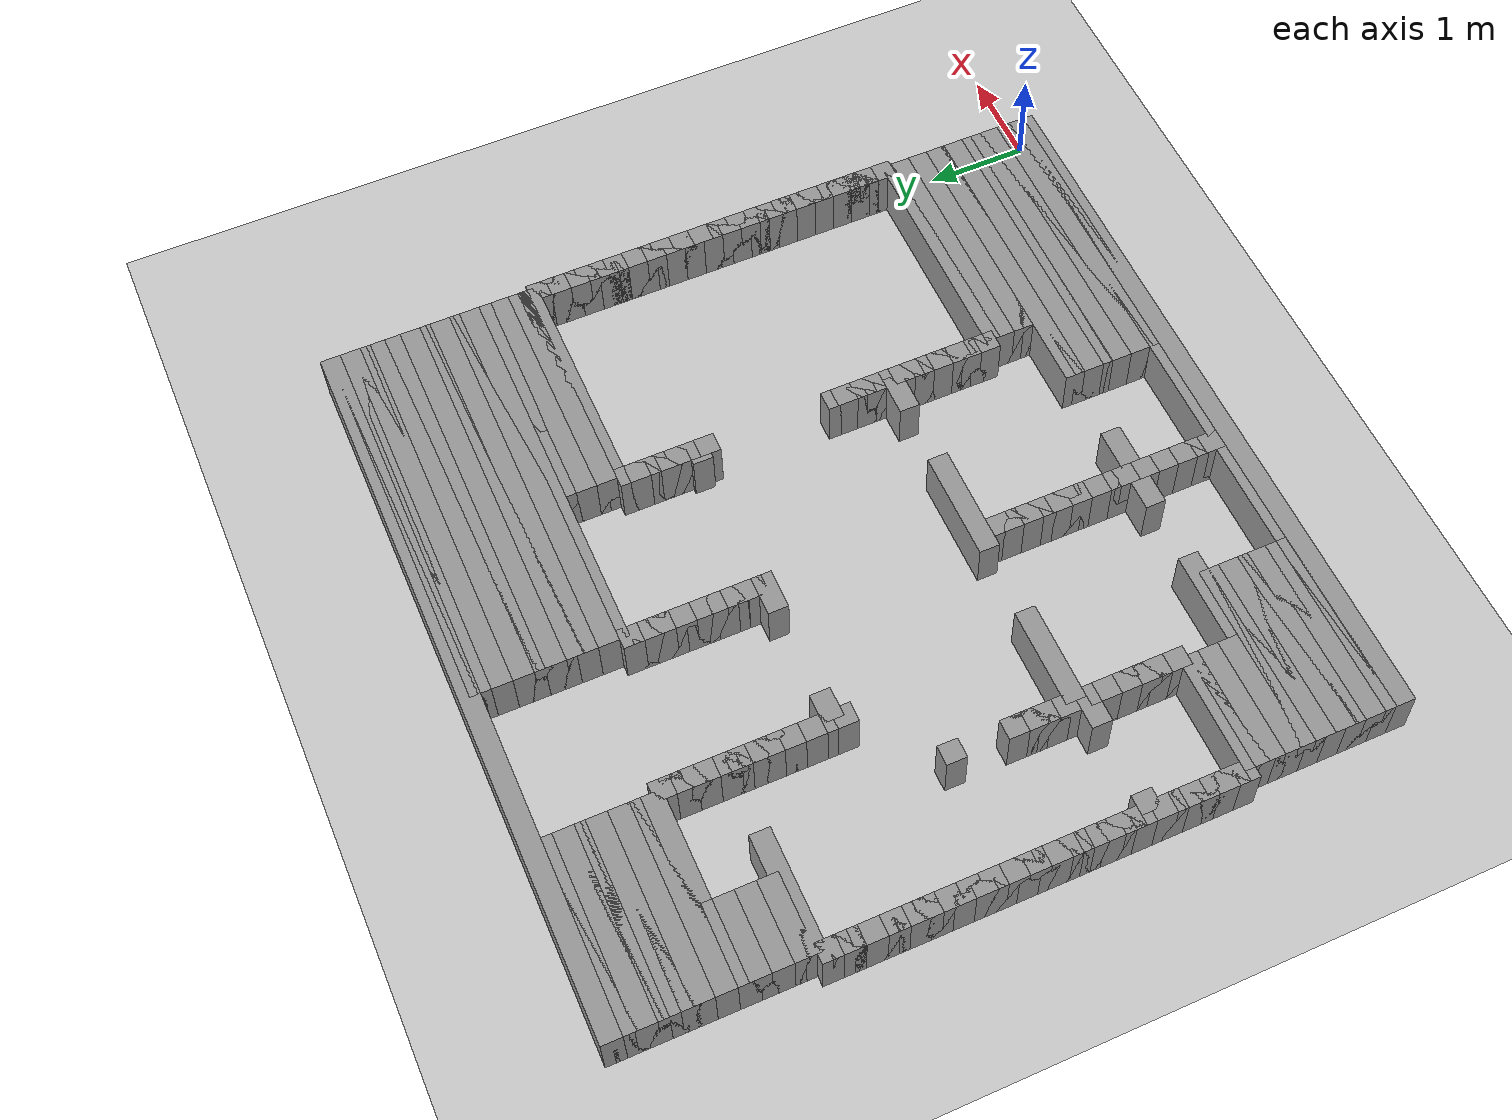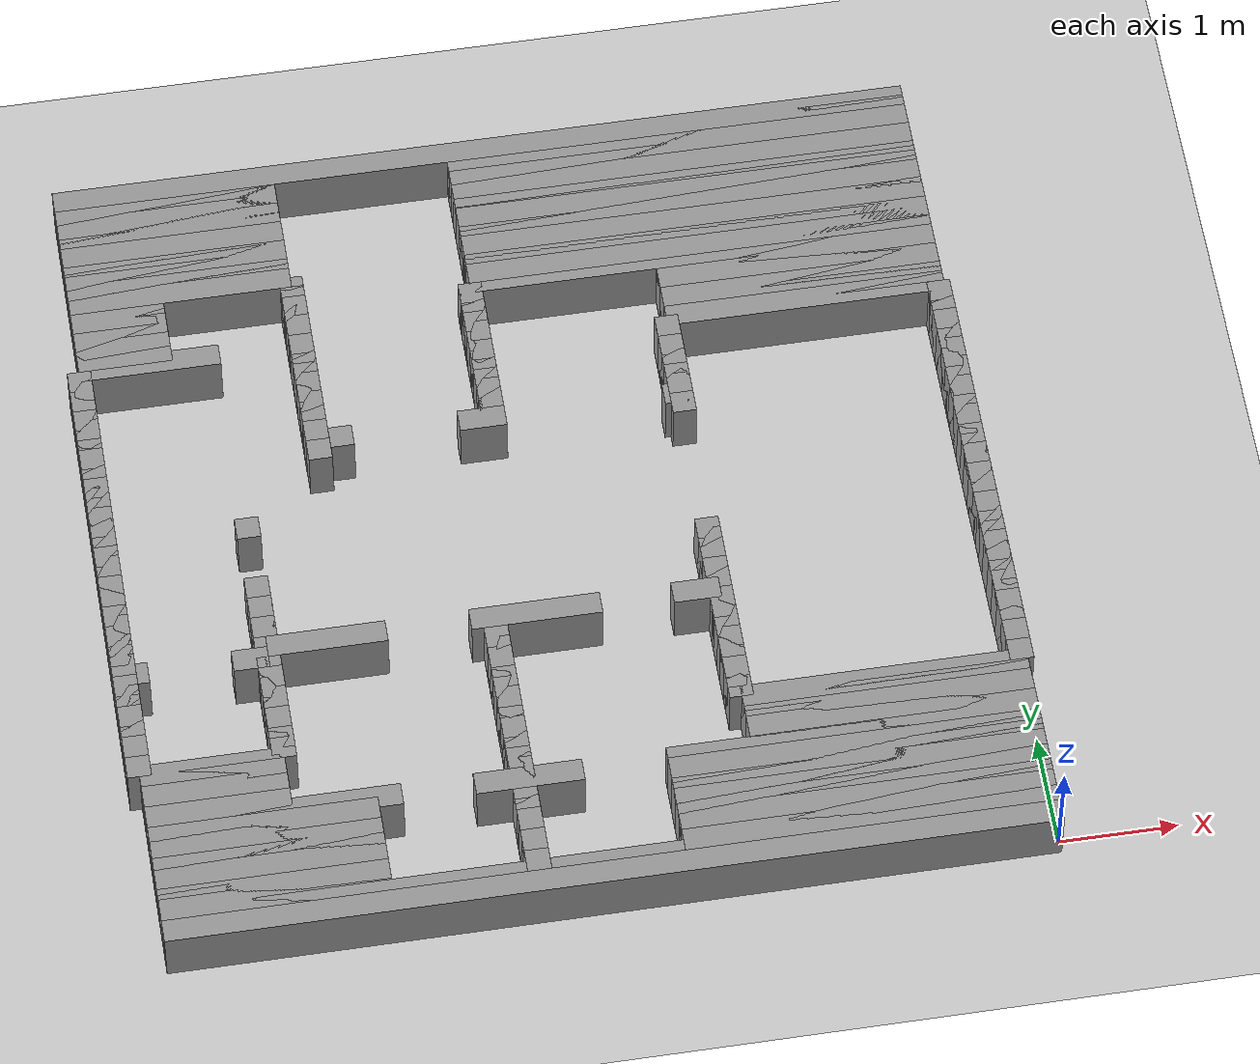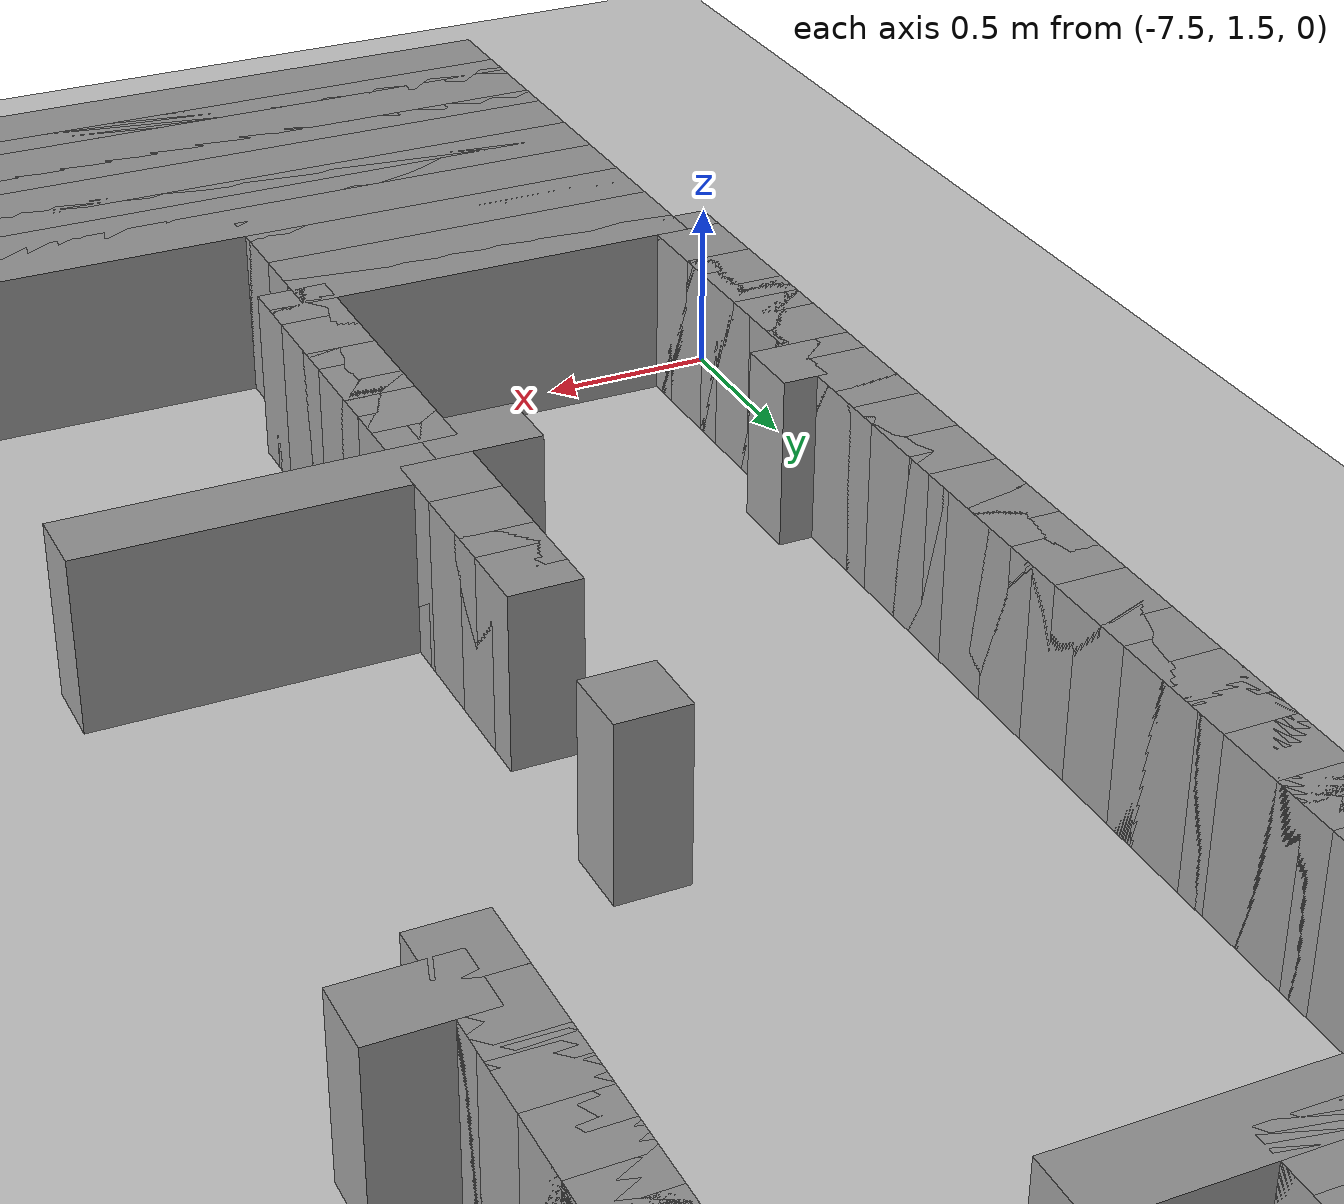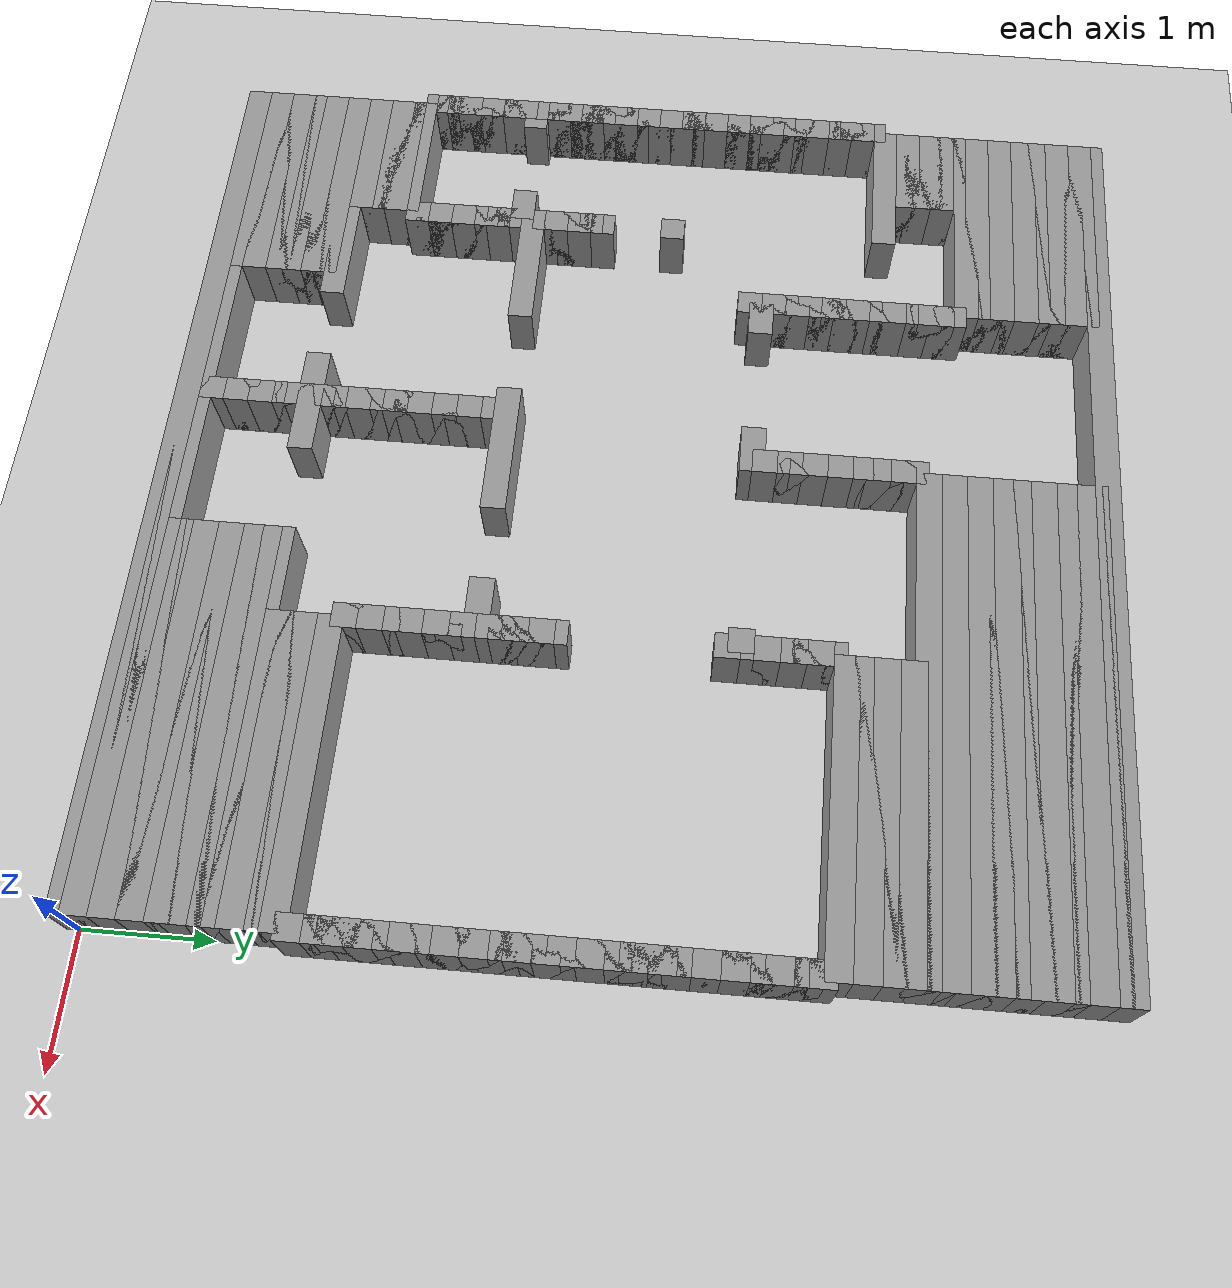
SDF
<?xml version='1.0' encoding='UTF-8'?>
<sdf version="1.6"><world name="GridMap"><include><uri>model://sun</uri></include><include><uri>model://ground_plane</uri></include><physics type="ode"><real_time_update_rate>1000.0</real_time_update_rate><max_step_size>0.001</max_step_size><real_time_factor>1</real_time_factor><ode><solver><type>quick</type><iters>150</iters><precon_iters>0</precon_iters><sor>1.4</sor><use_dynamic_moi_rescaling>1</use_dynamic_moi_rescaling></solver><constraints><cfm>0.00001</cfm><erp>0.2</erp><contact_max_correcting_vel>2000.000000</contact_max_correcting_vel><contact_surface_layer>0.01000</contact_surface_layer></constraints></ode></physics><model name="GridMap"><pose frame="">0 0 0 0 -0 0</pose><link name="Wall_(37.0,0.0)"><collision name="Wall_(37.0,0.0)_Collision"><geometry><box><size>7.4 0.2 0.5</size></box></geometry><pose frame="">-3.7 0.0 0.25 0 -0 0</pose></collision><inertial><mass>0.5</mass><pose>0 0.01 0 0 0 0</pose><inertia><ixx>0.004</ixx><ixy>0.001</ixy><ixz>0</ixz><iyy>0.006</iyy><iyz>0</iyz><izz>0.007</izz></inertia></inertial><visual name="Wall_(37.0,0.0)_Visual"><geometry><box><size>7.4 0.2 0.5</size></box></geometry><pose frame="">-3.7 0.0 0.25 0 -0 0</pose><material><script><uri>file://media/materials/scripts/gazebo.material</uri><name>Gazebo/Grey</name></script><ambient>1 1 1 1</ambient></material><meta><layer>0</layer></meta></visual><pose frame="">0 0 0 0 -0 0</pose></link><link name="Wall_(37.0,1.0)"><collision name="Wall_(37.0,1.0)_Collision"><geometry><box><size>7.4 0.2 0.5</size></box></geometry><pose frame="">-3.7 0.1 0.25 0 -0 0</pose></collision><inertial><mass>0.5</mass><pose>0 0.01 0 0 0 0</pose><inertia><ixx>0.004</ixx><ixy>0.001</ixy><ixz>0</ixz><iyy>0.006</iyy><iyz>0</iyz><izz>0.007</izz></inertia></inertial><visual name="Wall_(37.0,1.0)_Visual"><geometry><box><size>7.4 0.2 0.5</size></box></geometry><pose frame="">-3.7 0.1 0.25 0 -0 0</pose><material><script><uri>file://media/materials/scripts/gazebo.material</uri><name>Gazebo/Grey</name></script><ambient>1 1 1 1</ambient></material><meta><layer>0</layer></meta></visual><pose frame="">0 0 0 0 -0 0</pose></link><link name="Wall_(15.5,2.0)"><collision name="Wall_(15.5,2.0)_Collision"><geometry><box><size>3.1 0.2 0.5</size></box></geometry><pose frame="">-1.55 0.2 0.25 0 -0 0</pose></collision><inertial><mass>0.5</mass><pose>0 0.01 0 0 0 0</pose><inertia><ixx>0.004</ixx><ixy>0.001</ixy><ixz>0</ixz><iyy>0.006</iyy><iyz>0</iyz><izz>0.007</izz></inertia></inertial><visual name="Wall_(15.5,2.0)_Visual"><geometry><box><size>3.1 0.2 0.5</size></box></geometry><pose frame="">-1.55 0.2 0.25 0 -0 0</pose><material><script><uri>file://media/materials/scripts/gazebo.material</uri><name>Gazebo/Grey</name></script><ambient>1 1 1 1</ambient></material><meta><layer>0</layer></meta></visual><pose frame="">0 0 0 0 -0 0</pose></link><link name="Wall_(43.0,2.0)"><collision name="Wall_(43.0,2.0)_Collision"><geometry><box><size>0.2 0.2 0.5</size></box></geometry><pose frame="">-4.3 0.2 0.25 0 -0 0</pose></collision><inertial><mass>0.5</mass><pose>0 0.01 0 0 0 0</pose><inertia><ixx>0.004</ixx><ixy>0.001</ixy><ixz>0</ixz><iyy>0.006</iyy><iyz>0</iyz><izz>0.007</izz></inertia></inertial><visual name="Wall_(43.0,2.0)_Visual"><geometry><box><size>0.2 0.2 0.5</size></box></geometry><pose frame="">-4.3 0.2 0.25 0 -0 0</pose><material><script><uri>file://media/materials/scripts/gazebo.material</uri><name>Gazebo/Grey</name></script><ambient>1 1 1 1</ambient></material><meta><layer>0</layer></meta></visual><pose frame="">0 0 0 0 -0 0</pose></link><link name="Wall_(64.5,2.0)"><collision name="Wall_(64.5,2.0)_Collision"><geometry><box><size>1.9000000000000001 0.2 0.5</size></box></geometry><pose frame="">-6.45 0.2 0.25 0 -0 0</pose></collision><inertial><mass>0.5</mass><pose>0 0.01 0 0 0 0</pose><inertia><ixx>0.004</ixx><ixy>0.001</ixy><ixz>0</ixz><iyy>0.006</iyy><iyz>0</iyz><izz>0.007</izz></inertia></inertial><visual name="Wall_(64.5,2.0)_Visual"><geometry><box><size>1.9000000000000001 0.2 0.5</size></box></geometry><pose frame="">-6.45 0.2 0.25 0 -0 0</pose><material><script><uri>file://media/materials/scripts/gazebo.material</uri><name>Gazebo/Grey</name></script><ambient>1 1 1 1</ambient></material><meta><layer>0</layer></meta></visual><pose frame="">0 0 0 0 -0 0</pose></link><link name="Wall_(15.5,3.0)"><collision name="Wall_(15.5,3.0)_Collision"><geometry><box><size>3.1 0.2 0.5</size></box></geometry><pose frame="">-1.55 0.30000000000000004 0.25 0 -0 0</pose></collision><inertial><mass>0.5</mass><pose>0 0.01 0 0 0 0</pose><inertia><ixx>0.004</ixx><ixy>0.001</ixy><ixz>0</ixz><iyy>0.006</iyy><iyz>0</iyz><izz>0.007</izz></inertia></inertial><visual name="Wall_(15.5,3.0)_Visual"><geometry><box><size>3.1 0.2 0.5</size></box></geometry><pose frame="">-1.55 0.30000000000000004 0.25 0 -0 0</pose><material><script><uri>file://media/materials/scripts/gazebo.material</uri><name>Gazebo/Grey</name></script><ambient>1 1 1 1</ambient></material><meta><layer>0</layer></meta></visual><pose frame="">0 0 0 0 -0 0</pose></link><link name="Wall_(43.0,3.0)"><collision name="Wall_(43.0,3.0)_Collision"><geometry><box><size>0.2 0.2 0.5</size></box></geometry><pose frame="">-4.3 0.30000000000000004 0.25 0 -0 0</pose></collision><inertial><mass>0.5</mass><pose>0 0.01 0 0 0 0</pose><inertia><ixx>0.004</ixx><ixy>0.001</ixy><ixz>0</ixz><iyy>0.006</iyy><iyz>0</iyz><izz>0.007</izz></inertia></inertial><visual name="Wall_(43.0,3.0)_Visual"><geometry><box><size>0.2 0.2 0.5</size></box></geometry><pose frame="">-4.3 0.30000000000000004 0.25 0 -0 0</pose><material><script><uri>file://media/materials/scripts/gazebo.material</uri><name>Gazebo/Grey</name></script><ambient>1 1 1 1</ambient></material><meta><layer>0</layer></meta></visual><pose frame="">0 0 0 0 -0 0</pose></link><link name="Wall_(64.5,3.0)"><collision name="Wall_(64.5,3.0)_Collision"><geometry><box><size>1.9000000000000001 0.2 0.5</size></box></geometry><pose frame="">-6.45 0.30000000000000004 0.25 0 -0 0</pose></collision><inertial><mass>0.5</mass><pose>0 0.01 0 0 0 0</pose><inertia><ixx>0.004</ixx><ixy>0.001</ixy><ixz>0</ixz><iyy>0.006</iyy><iyz>0</iyz><izz>0.007</izz></inertia></inertial><visual name="Wall_(64.5,3.0)_Visual"><geometry><box><size>1.9000000000000001 0.2 0.5</size></box></geometry><pose frame="">-6.45 0.30000000000000004 0.25 0 -0 0</pose><material><script><uri>file://media/materials/scripts/gazebo.material</uri><name>Gazebo/Grey</name></script><ambient>1 1 1 1</ambient></material><meta><layer>0</layer></meta></visual><pose frame="">0 0 0 0 -0 0</pose></link><link name="Wall_(15.5,4.0)"><collision name="Wall_(15.5,4.0)_Collision"><geometry><box><size>3.1 0.2 0.5</size></box></geometry><pose frame="">-1.55 0.4 0.25 0 -0 0</pose></collision><inertial><mass>0.5</mass><pose>0 0.01 0 0 0 0</pose><inertia><ixx>0.004</ixx><ixy>0.001</ixy><ixz>0</ixz><iyy>0.006</iyy><iyz>0</iyz><izz>0.007</izz></inertia></inertial><visual name="Wall_(15.5,4.0)_Visual"><geometry><box><size>3.1 0.2 0.5</size></box></geometry><pose frame="">-1.55 0.4 0.25 0 -0 0</pose><material><script><uri>file://media/materials/scripts/gazebo.material</uri><name>Gazebo/Grey</name></script><ambient>1 1 1 1</ambient></material><meta><layer>0</layer></meta></visual><pose frame="">0 0 0 0 -0 0</pose></link><link name="Wall_(43.0,4.0)"><collision name="Wall_(43.0,4.0)_Collision"><geometry><box><size>0.2 0.2 0.5</size></box></geometry><pose frame="">-4.3 0.4 0.25 0 -0 0</pose></collision><inertial><mass>0.5</mass><pose>0 0.01 0 0 0 0</pose><inertia><ixx>0.004</ixx><ixy>0.001</ixy><ixz>0</ixz><iyy>0.006</iyy><iyz>0</iyz><izz>0.007</izz></inertia></inertial><visual name="Wall_(43.0,4.0)_Visual"><geometry><box><size>0.2 0.2 0.5</size></box></geometry><pose frame="">-4.3 0.4 0.25 0 -0 0</pose><material><script><uri>file://media/materials/scripts/gazebo.material</uri><name>Gazebo/Grey</name></script><ambient>1 1 1 1</ambient></material><meta><layer>0</layer></meta></visual><pose frame="">0 0 0 0 -0 0</pose></link><link name="Wall_(64.5,4.0)"><collision name="Wall_(64.5,4.0)_Collision"><geometry><box><size>1.9000000000000001 0.2 0.5</size></box></geometry><pose frame="">-6.45 0.4 0.25 0 -0 0</pose></collision><inertial><mass>0.5</mass><pose>0 0.01 0 0 0 0</pose><inertia><ixx>0.004</ixx><ixy>0.001</ixy><ixz>0</ixz><iyy>0.006</iyy><iyz>0</iyz><izz>0.007</izz></inertia></inertial><visual name="Wall_(64.5,4.0)_Visual"><geometry><box><size>1.9000000000000001 0.2 0.5</size></box></geometry><pose frame="">-6.45 0.4 0.25 0 -0 0</pose><material><script><uri>file://media/materials/scripts/gazebo.material</uri><name>Gazebo/Grey</name></script><ambient>1 1 1 1</ambient></material><meta><layer>0</layer></meta></visual><pose frame="">0 0 0 0 -0 0</pose></link><link name="Wall_(15.5,5.0)"><collision name="Wall_(15.5,5.0)_Collision"><geometry><box><size>3.1 0.2 0.5</size></box></geometry><pose frame="">-1.55 0.5 0.25 0 -0 0</pose></collision><inertial><mass>0.5</mass><pose>0 0.01 0 0 0 0</pose><inertia><ixx>0.004</ixx><ixy>0.001</ixy><ixz>0</ixz><iyy>0.006</iyy><iyz>0</iyz><izz>0.007</izz></inertia></inertial><visual name="Wall_(15.5,5.0)_Visual"><geometry><box><size>3.1 0.2 0.5</size></box></geometry><pose frame="">-1.55 0.5 0.25 0 -0 0</pose><material><script><uri>file://media/materials/scripts/gazebo.material</uri><name>Gazebo/Grey</name></script><ambient>1 1 1 1</ambient></material><meta><layer>0</layer></meta></visual><pose frame="">0 0 0 0 -0 0</pose></link><link name="Wall_(43.0,5.0)"><collision name="Wall_(43.0,5.0)_Collision"><geometry><box><size>0.2 0.2 0.5</size></box></geometry><pose frame="">-4.3 0.5 0.25 0 -0 0</pose></collision><inertial><mass>0.5</mass><pose>0 0.01 0 0 0 0</pose><inertia><ixx>0.004</ixx><ixy>0.001</ixy><ixz>0</ixz><iyy>0.006</iyy><iyz>0</iyz><izz>0.007</izz></inertia></inertial><visual name="Wall_(43.0,5.0)_Visual"><geometry><box><size>0.2 0.2 0.5</size></box></geometry><pose frame="">-4.3 0.5 0.25 0 -0 0</pose><material><script><uri>file://media/materials/scripts/gazebo.material</uri><name>Gazebo/Grey</name></script><ambient>1 1 1 1</ambient></material><meta><layer>0</layer></meta></visual><pose frame="">0 0 0 0 -0 0</pose></link><link name="Wall_(64.5,5.0)"><collision name="Wall_(64.5,5.0)_Collision"><geometry><box><size>1.9000000000000001 0.2 0.5</size></box></geometry><pose frame="">-6.45 0.5 0.25 0 -0 0</pose></collision><inertial><mass>0.5</mass><pose>0 0.01 0 0 0 0</pose><inertia><ixx>0.004</ixx><ixy>0.001</ixy><ixz>0</ixz><iyy>0.006</iyy><iyz>0</iyz><izz>0.007</izz></inertia></inertial><visual name="Wall_(64.5,5.0)_Visual"><geometry><box><size>1.9000000000000001 0.2 0.5</size></box></geometry><pose frame="">-6.45 0.5 0.25 0 -0 0</pose><material><script><uri>file://media/materials/scripts/gazebo.material</uri><name>Gazebo/Grey</name></script><ambient>1 1 1 1</ambient></material><meta><layer>0</layer></meta></visual><pose frame="">0 0 0 0 -0 0</pose></link><link name="Wall_(15.5,6.0)"><collision name="Wall_(15.5,6.0)_Collision"><geometry><box><size>3.1 0.2 0.5</size></box></geometry><pose frame="">-1.55 0.6000000000000001 0.25 0 -0 0</pose></collision><inertial><mass>0.5</mass><pose>0 0.01 0 0 0 0</pose><inertia><ixx>0.004</ixx><ixy>0.001</ixy><ixz>0</ixz><iyy>0.006</iyy><iyz>0</iyz><izz>0.007</izz></inertia></inertial><visual name="Wall_(15.5,6.0)_Visual"><geometry><box><size>3.1 0.2 0.5</size></box></geometry><pose frame="">-1.55 0.6000000000000001 0.25 0 -0 0</pose><material><script><uri>file://media/materials/scripts/gazebo.material</uri><name>Gazebo/Grey</name></script><ambient>1 1 1 1</ambient></material><meta><layer>0</layer></meta></visual><pose frame="">0 0 0 0 -0 0</pose></link><link name="Wall_(43.0,6.0)"><collision name="Wall_(43.0,6.0)_Collision"><geometry><box><size>0.2 0.2 0.5</size></box></geometry><pose frame="">-4.3 0.6000000000000001 0.25 0 -0 0</pose></collision><inertial><mass>0.5</mass><pose>0 0.01 0 0 0 0</pose><inertia><ixx>0.004</ixx><ixy>0.001</ixy><ixz>0</ixz><iyy>0.006</iyy><iyz>0</iyz><izz>0.007</izz></inertia></inertial><visual name="Wall_(43.0,6.0)_Visual"><geometry><box><size>0.2 0.2 0.5</size></box></geometry><pose frame="">-4.3 0.6000000000000001 0.25 0 -0 0</pose><material><script><uri>file://media/materials/scripts/gazebo.material</uri><name>Gazebo/Grey</name></script><ambient>1 1 1 1</ambient></material><meta><layer>0</layer></meta></visual><pose frame="">0 0 0 0 -0 0</pose></link><link name="Wall_(64.5,6.0)"><collision name="Wall_(64.5,6.0)_Collision"><geometry><box><size>1.9000000000000001 0.2 0.5</size></box></geometry><pose frame="">-6.45 0.6000000000000001 0.25 0 -0 0</pose></collision><inertial><mass>0.5</mass><pose>0 0.01 0 0 0 0</pose><inertia><ixx>0.004</ixx><ixy>0.001</ixy><ixz>0</ixz><iyy>0.006</iyy><iyz>0</iyz><izz>0.007</izz></inertia></inertial><visual name="Wall_(64.5,6.0)_Visual"><geometry><box><size>1.9000000000000001 0.2 0.5</size></box></geometry><pose frame="">-6.45 0.6000000000000001 0.25 0 -0 0</pose><material><script><uri>file://media/materials/scripts/gazebo.material</uri><name>Gazebo/Grey</name></script><ambient>1 1 1 1</ambient></material><meta><layer>0</layer></meta></visual><pose frame="">0 0 0 0 -0 0</pose></link><link name="Wall_(15.5,7.0)"><collision name="Wall_(15.5,7.0)_Collision"><geometry><box><size>3.1 0.2 0.5</size></box></geometry><pose frame="">-1.55 0.7000000000000001 0.25 0 -0 0</pose></collision><inertial><mass>0.5</mass><pose>0 0.01 0 0 0 0</pose><inertia><ixx>0.004</ixx><ixy>0.001</ixy><ixz>0</ixz><iyy>0.006</iyy><iyz>0</iyz><izz>0.007</izz></inertia></inertial><visual name="Wall_(15.5,7.0)_Visual"><geometry><box><size>3.1 0.2 0.5</size></box></geometry><pose frame="">-1.55 0.7000000000000001 0.25 0 -0 0</pose><material><script><uri>file://media/materials/scripts/gazebo.material</uri><name>Gazebo/Grey</name></script><ambient>1 1 1 1</ambient></material><meta><layer>0</layer></meta></visual><pose frame="">0 0 0 0 -0 0</pose></link><link name="Wall_(43.0,7.0)"><collision name="Wall_(43.0,7.0)_Collision"><geometry><box><size>0.2 0.2 0.5</size></box></geometry><pose frame="">-4.3 0.7000000000000001 0.25 0 -0 0</pose></collision><inertial><mass>0.5</mass><pose>0 0.01 0 0 0 0</pose><inertia><ixx>0.004</ixx><ixy>0.001</ixy><ixz>0</ixz><iyy>0.006</iyy><iyz>0</iyz><izz>0.007</izz></inertia></inertial><visual name="Wall_(43.0,7.0)_Visual"><geometry><box><size>0.2 0.2 0.5</size></box></geometry><pose frame="">-4.3 0.7000000000000001 0.25 0 -0 0</pose><material><script><uri>file://media/materials/scripts/gazebo.material</uri><name>Gazebo/Grey</name></script><ambient>1 1 1 1</ambient></material><meta><layer>0</layer></meta></visual><pose frame="">0 0 0 0 -0 0</pose></link><link name="Wall_(64.5,7.0)"><collision name="Wall_(64.5,7.0)_Collision"><geometry><box><size>1.9000000000000001 0.2 0.5</size></box></geometry><pose frame="">-6.45 0.7000000000000001 0.25 0 -0 0</pose></collision><inertial><mass>0.5</mass><pose>0 0.01 0 0 0 0</pose><inertia><ixx>0.004</ixx><ixy>0.001</ixy><ixz>0</ixz><iyy>0.006</iyy><iyz>0</iyz><izz>0.007</izz></inertia></inertial><visual name="Wall_(64.5,7.0)_Visual"><geometry><box><size>1.9000000000000001 0.2 0.5</size></box></geometry><pose frame="">-6.45 0.7000000000000001 0.25 0 -0 0</pose><material><script><uri>file://media/materials/scripts/gazebo.material</uri><name>Gazebo/Grey</name></script><ambient>1 1 1 1</ambient></material><meta><layer>0</layer></meta></visual><pose frame="">0 0 0 0 -0 0</pose></link><link name="Wall_(15.5,8.0)"><collision name="Wall_(15.5,8.0)_Collision"><geometry><box><size>3.1 0.2 0.5</size></box></geometry><pose frame="">-1.55 0.8 0.25 0 -0 0</pose></collision><inertial><mass>0.5</mass><pose>0 0.01 0 0 0 0</pose><inertia><ixx>0.004</ixx><ixy>0.001</ixy><ixz>0</ixz><iyy>0.006</iyy><iyz>0</iyz><izz>0.007</izz></inertia></inertial><visual name="Wall_(15.5,8.0)_Visual"><geometry><box><size>3.1 0.2 0.5</size></box></geometry><pose frame="">-1.55 0.8 0.25 0 -0 0</pose><material><script><uri>file://media/materials/scripts/gazebo.material</uri><name>Gazebo/Grey</name></script><ambient>1 1 1 1</ambient></material><meta><layer>0</layer></meta></visual><pose frame="">0 0 0 0 -0 0</pose></link><link name="Wall_(43.0,8.0)"><collision name="Wall_(43.0,8.0)_Collision"><geometry><box><size>0.2 0.2 0.5</size></box></geometry><pose frame="">-4.3 0.8 0.25 0 -0 0</pose></collision><inertial><mass>0.5</mass><pose>0 0.01 0 0 0 0</pose><inertia><ixx>0.004</ixx><ixy>0.001</ixy><ixz>0</ixz><iyy>0.006</iyy><iyz>0</iyz><izz>0.007</izz></inertia></inertial><visual name="Wall_(43.0,8.0)_Visual"><geometry><box><size>0.2 0.2 0.5</size></box></geometry><pose frame="">-4.3 0.8 0.25 0 -0 0</pose><material><script><uri>file://media/materials/scripts/gazebo.material</uri><name>Gazebo/Grey</name></script><ambient>1 1 1 1</ambient></material><meta><layer>0</layer></meta></visual><pose frame="">0 0 0 0 -0 0</pose></link><link name="Wall_(64.5,8.0)"><collision name="Wall_(64.5,8.0)_Collision"><geometry><box><size>1.9000000000000001 0.2 0.5</size></box></geometry><pose frame="">-6.45 0.8 0.25 0 -0 0</pose></collision><inertial><mass>0.5</mass><pose>0 0.01 0 0 0 0</pose><inertia><ixx>0.004</ixx><ixy>0.001</ixy><ixz>0</ixz><iyy>0.006</iyy><iyz>0</iyz><izz>0.007</izz></inertia></inertial><visual name="Wall_(64.5,8.0)_Visual"><geometry><box><size>1.9000000000000001 0.2 0.5</size></box></geometry><pose frame="">-6.45 0.8 0.25 0 -0 0</pose><material><script><uri>file://media/materials/scripts/gazebo.material</uri><name>Gazebo/Grey</name></script><ambient>1 1 1 1</ambient></material><meta><layer>0</layer></meta></visual><pose frame="">0 0 0 0 -0 0</pose></link><link name="Wall_(15.5,9.0)"><collision name="Wall_(15.5,9.0)_Collision"><geometry><box><size>3.1 0.2 0.5</size></box></geometry><pose frame="">-1.55 0.9 0.25 0 -0 0</pose></collision><inertial><mass>0.5</mass><pose>0 0.01 0 0 0 0</pose><inertia><ixx>0.004</ixx><ixy>0.001</ixy><ixz>0</ixz><iyy>0.006</iyy><iyz>0</iyz><izz>0.007</izz></inertia></inertial><visual name="Wall_(15.5,9.0)_Visual"><geometry><box><size>3.1 0.2 0.5</size></box></geometry><pose frame="">-1.55 0.9 0.25 0 -0 0</pose><material><script><uri>file://media/materials/scripts/gazebo.material</uri><name>Gazebo/Grey</name></script><ambient>1 1 1 1</ambient></material><meta><layer>0</layer></meta></visual><pose frame="">0 0 0 0 -0 0</pose></link><link name="Wall_(43.0,9.0)"><collision name="Wall_(43.0,9.0)_Collision"><geometry><box><size>0.2 0.2 0.5</size></box></geometry><pose frame="">-4.3 0.9 0.25 0 -0 0</pose></collision><inertial><mass>0.5</mass><pose>0 0.01 0 0 0 0</pose><inertia><ixx>0.004</ixx><ixy>0.001</ixy><ixz>0</ixz><iyy>0.006</iyy><iyz>0</iyz><izz>0.007</izz></inertia></inertial><visual name="Wall_(43.0,9.0)_Visual"><geometry><box><size>0.2 0.2 0.5</size></box></geometry><pose frame="">-4.3 0.9 0.25 0 -0 0</pose><material><script><uri>file://media/materials/scripts/gazebo.material</uri><name>Gazebo/Grey</name></script><ambient>1 1 1 1</ambient></material><meta><layer>0</layer></meta></visual><pose frame="">0 0 0 0 -0 0</pose></link><link name="Wall_(64.5,9.0)"><collision name="Wall_(64.5,9.0)_Collision"><geometry><box><size>1.9000000000000001 0.2 0.5</size></box></geometry><pose frame="">-6.45 0.9 0.25 0 -0 0</pose></collision><inertial><mass>0.5</mass><pose>0 0.01 0 0 0 0</pose><inertia><ixx>0.004</ixx><ixy>0.001</ixy><ixz>0</ixz><iyy>0.006</iyy><iyz>0</iyz><izz>0.007</izz></inertia></inertial><visual name="Wall_(64.5,9.0)_Visual"><geometry><box><size>1.9000000000000001 0.2 0.5</size></box></geometry><pose frame="">-6.45 0.9 0.25 0 -0 0</pose><material><script><uri>file://media/materials/scripts/gazebo.material</uri><name>Gazebo/Grey</name></script><ambient>1 1 1 1</ambient></material><meta><layer>0</layer></meta></visual><pose frame="">0 0 0 0 -0 0</pose></link><link name="Wall_(15.5,10.0)"><collision name="Wall_(15.5,10.0)_Collision"><geometry><box><size>3.1 0.2 0.5</size></box></geometry><pose frame="">-1.55 1.0 0.25 0 -0 0</pose></collision><inertial><mass>0.5</mass><pose>0 0.01 0 0 0 0</pose><inertia><ixx>0.004</ixx><ixy>0.001</ixy><ixz>0</ixz><iyy>0.006</iyy><iyz>0</iyz><izz>0.007</izz></inertia></inertial><visual name="Wall_(15.5,10.0)_Visual"><geometry><box><size>3.1 0.2 0.5</size></box></geometry><pose frame="">-1.55 1.0 0.25 0 -0 0</pose><material><script><uri>file://media/materials/scripts/gazebo.material</uri><name>Gazebo/Grey</name></script><ambient>1 1 1 1</ambient></material><meta><layer>0</layer></meta></visual><pose frame="">0 0 0 0 -0 0</pose></link><link name="Wall_(42.5,10.0)"><collision name="Wall_(42.5,10.0)_Collision"><geometry><box><size>0.9 0.2 0.5</size></box></geometry><pose frame="">-4.25 1.0 0.25 0 -0 0</pose></collision><inertial><mass>0.5</mass><pose>0 0.01 0 0 0 0</pose><inertia><ixx>0.004</ixx><ixy>0.001</ixy><ixz>0</ixz><iyy>0.006</iyy><iyz>0</iyz><izz>0.007</izz></inertia></inertial><visual name="Wall_(42.5,10.0)_Visual"><geometry><box><size>0.9 0.2 0.5</size></box></geometry><pose frame="">-4.25 1.0 0.25 0 -0 0</pose><material><script><uri>file://media/materials/scripts/gazebo.material</uri><name>Gazebo/Grey</name></script><ambient>1 1 1 1</ambient></material><meta><layer>0</layer></meta></visual><pose frame="">0 0 0 0 -0 0</pose></link><link name="Wall_(63.5,10.0)"><collision name="Wall_(63.5,10.0)_Collision"><geometry><box><size>2.1 0.2 0.5</size></box></geometry><pose frame="">-6.3500000000000005 1.0 0.25 0 -0 0</pose></collision><inertial><mass>0.5</mass><pose>0 0.01 0 0 0 0</pose><inertia><ixx>0.004</ixx><ixy>0.001</ixy><ixz>0</ixz><iyy>0.006</iyy><iyz>0</iyz><izz>0.007</izz></inertia></inertial><visual name="Wall_(63.5,10.0)_Visual"><geometry><box><size>2.1 0.2 0.5</size></box></geometry><pose frame="">-6.3500000000000005 1.0 0.25 0 -0 0</pose><material><script><uri>file://media/materials/scripts/gazebo.material</uri><name>Gazebo/Grey</name></script><ambient>1 1 1 1</ambient></material><meta><layer>0</layer></meta></visual><pose frame="">0 0 0 0 -0 0</pose></link><link name="Wall_(12.0,11.0)"><collision name="Wall_(12.0,11.0)_Collision"><geometry><box><size>2.4000000000000004 0.2 0.5</size></box></geometry><pose frame="">-1.2000000000000002 1.1 0.25 0 -0 0</pose></collision><inertial><mass>0.5</mass><pose>0 0.01 0 0 0 0</pose><inertia><ixx>0.004</ixx><ixy>0.001</ixy><ixz>0</ixz><iyy>0.006</iyy><iyz>0</iyz><izz>0.007</izz></inertia></inertial><visual name="Wall_(12.0,11.0)_Visual"><geometry><box><size>2.4000000000000004 0.2 0.5</size></box></geometry><pose frame="">-1.2000000000000002 1.1 0.25 0 -0 0</pose><material><script><uri>file://media/materials/scripts/gazebo.material</uri><name>Gazebo/Grey</name></script><ambient>1 1 1 1</ambient></material><meta><layer>0</layer></meta></visual><pose frame="">0 0 0 0 -0 0</pose></link><link name="Wall_(43.0,11.0)"><collision name="Wall_(43.0,11.0)_Collision"><geometry><box><size>0.2 0.2 0.5</size></box></geometry><pose frame="">-4.3 1.1 0.25 0 -0 0</pose></collision><inertial><mass>0.5</mass><pose>0 0.01 0 0 0 0</pose><inertia><ixx>0.004</ixx><ixy>0.001</ixy><ixz>0</ixz><iyy>0.006</iyy><iyz>0</iyz><izz>0.007</izz></inertia></inertial><visual name="Wall_(43.0,11.0)_Visual"><geometry><box><size>0.2 0.2 0.5</size></box></geometry><pose frame="">-4.3 1.1 0.25 0 -0 0</pose><material><script><uri>file://media/materials/scripts/gazebo.material</uri><name>Gazebo/Grey</name></script><ambient>1 1 1 1</ambient></material><meta><layer>0</layer></meta></visual><pose frame="">0 0 0 0 -0 0</pose></link><link name="Wall_(68.0,11.0)"><collision name="Wall_(68.0,11.0)_Collision"><geometry><box><size>1.2000000000000002 0.2 0.5</size></box></geometry><pose frame="">-6.800000000000001 1.1 0.25 0 -0 0</pose></collision><inertial><mass>0.5</mass><pose>0 0.01 0 0 0 0</pose><inertia><ixx>0.004</ixx><ixy>0.001</ixy><ixz>0</ixz><iyy>0.006</iyy><iyz>0</iyz><izz>0.007</izz></inertia></inertial><visual name="Wall_(68.0,11.0)_Visual"><geometry><box><size>1.2000000000000002 0.2 0.5</size></box></geometry><pose frame="">-6.800000000000001 1.1 0.25 0 -0 0</pose><material><script><uri>file://media/materials/scripts/gazebo.material</uri><name>Gazebo/Grey</name></script><ambient>1 1 1 1</ambient></material><meta><layer>0</layer></meta></visual><pose frame="">0 0 0 0 -0 0</pose></link><link name="Wall_(12.0,12.0)"><collision name="Wall_(12.0,12.0)_Collision"><geometry><box><size>2.4000000000000004 0.2 0.5</size></box></geometry><pose frame="">-1.2000000000000002 1.2000000000000002 0.25 0 -0 0</pose></collision><inertial><mass>0.5</mass><pose>0 0.01 0 0 0 0</pose><inertia><ixx>0.004</ixx><ixy>0.001</ixy><ixz>0</ixz><iyy>0.006</iyy><iyz>0</iyz><izz>0.007</izz></inertia></inertial><visual name="Wall_(12.0,12.0)_Visual"><geometry><box><size>2.4000000000000004 0.2 0.5</size></box></geometry><pose frame="">-1.2000000000000002 1.2000000000000002 0.25 0 -0 0</pose><material><script><uri>file://media/materials/scripts/gazebo.material</uri><name>Gazebo/Grey</name></script><ambient>1 1 1 1</ambient></material><meta><layer>0</layer></meta></visual><pose frame="">0 0 0 0 -0 0</pose></link><link name="Wall_(43.0,12.0)"><collision name="Wall_(43.0,12.0)_Collision"><geometry><box><size>0.2 0.2 0.5</size></box></geometry><pose frame="">-4.3 1.2000000000000002 0.25 0 -0 0</pose></collision><inertial><mass>0.5</mass><pose>0 0.01 0 0 0 0</pose><inertia><ixx>0.004</ixx><ixy>0.001</ixy><ixz>0</ixz><iyy>0.006</iyy><iyz>0</iyz><izz>0.007</izz></inertia></inertial><visual name="Wall_(43.0,12.0)_Visual"><geometry><box><size>0.2 0.2 0.5</size></box></geometry><pose frame="">-4.3 1.2000000000000002 0.25 0 -0 0</pose><material><script><uri>file://media/materials/scripts/gazebo.material</uri><name>Gazebo/Grey</name></script><ambient>1 1 1 1</ambient></material><meta><layer>0</layer></meta></visual><pose frame="">0 0 0 0 -0 0</pose></link><link name="Wall_(68.0,12.0)"><collision name="Wall_(68.0,12.0)_Collision"><geometry><box><size>1.2000000000000002 0.2 0.5</size></box></geometry><pose frame="">-6.800000000000001 1.2000000000000002 0.25 0 -0 0</pose></collision><inertial><mass>0.5</mass><pose>0 0.01 0 0 0 0</pose><inertia><ixx>0.004</ixx><ixy>0.001</ixy><ixz>0</ixz><iyy>0.006</iyy><iyz>0</iyz><izz>0.007</izz></inertia></inertial><visual name="Wall_(68.0,12.0)_Visual"><geometry><box><size>1.2000000000000002 0.2 0.5</size></box></geometry><pose frame="">-6.800000000000001 1.2000000000000002 0.25 0 -0 0</pose><material><script><uri>file://media/materials/scripts/gazebo.material</uri><name>Gazebo/Grey</name></script><ambient>1 1 1 1</ambient></material><meta><layer>0</layer></meta></visual><pose frame="">0 0 0 0 -0 0</pose></link><link name="Wall_(12.0,13.0)"><collision name="Wall_(12.0,13.0)_Collision"><geometry><box><size>2.4000000000000004 0.2 0.5</size></box></geometry><pose frame="">-1.2000000000000002 1.3 0.25 0 -0 0</pose></collision><inertial><mass>0.5</mass><pose>0 0.01 0 0 0 0</pose><inertia><ixx>0.004</ixx><ixy>0.001</ixy><ixz>0</ixz><iyy>0.006</iyy><iyz>0</iyz><izz>0.007</izz></inertia></inertial><visual name="Wall_(12.0,13.0)_Visual"><geometry><box><size>2.4000000000000004 0.2 0.5</size></box></geometry><pose frame="">-1.2000000000000002 1.3 0.25 0 -0 0</pose><material><script><uri>file://media/materials/scripts/gazebo.material</uri><name>Gazebo/Grey</name></script><ambient>1 1 1 1</ambient></material><meta><layer>0</layer></meta></visual><pose frame="">0 0 0 0 -0 0</pose></link><link name="Wall_(43.0,13.0)"><collision name="Wall_(43.0,13.0)_Collision"><geometry><box><size>0.2 0.2 0.5</size></box></geometry><pose frame="">-4.3 1.3 0.25 0 -0 0</pose></collision><inertial><mass>0.5</mass><pose>0 0.01 0 0 0 0</pose><inertia><ixx>0.004</ixx><ixy>0.001</ixy><ixz>0</ixz><iyy>0.006</iyy><iyz>0</iyz><izz>0.007</izz></inertia></inertial><visual name="Wall_(43.0,13.0)_Visual"><geometry><box><size>0.2 0.2 0.5</size></box></geometry><pose frame="">-4.3 1.3 0.25 0 -0 0</pose><material><script><uri>file://media/materials/scripts/gazebo.material</uri><name>Gazebo/Grey</name></script><ambient>1 1 1 1</ambient></material><meta><layer>0</layer></meta></visual><pose frame="">0 0 0 0 -0 0</pose></link><link name="Wall_(68.0,13.0)"><collision name="Wall_(68.0,13.0)_Collision"><geometry><box><size>1.2000000000000002 0.2 0.5</size></box></geometry><pose frame="">-6.800000000000001 1.3 0.25 0 -0 0</pose></collision><inertial><mass>0.5</mass><pose>0 0.01 0 0 0 0</pose><inertia><ixx>0.004</ixx><ixy>0.001</ixy><ixz>0</ixz><iyy>0.006</iyy><iyz>0</iyz><izz>0.007</izz></inertia></inertial><visual name="Wall_(68.0,13.0)_Visual"><geometry><box><size>1.2000000000000002 0.2 0.5</size></box></geometry><pose frame="">-6.800000000000001 1.3 0.25 0 -0 0</pose><material><script><uri>file://media/materials/scripts/gazebo.material</uri><name>Gazebo/Grey</name></script><ambient>1 1 1 1</ambient></material><meta><layer>0</layer></meta></visual><pose frame="">0 0 0 0 -0 0</pose></link><link name="Wall_(12.0,14.0)"><collision name="Wall_(12.0,14.0)_Collision"><geometry><box><size>2.4000000000000004 0.2 0.5</size></box></geometry><pose frame="">-1.2000000000000002 1.4000000000000001 0.25 0 -0 0</pose></collision><inertial><mass>0.5</mass><pose>0 0.01 0 0 0 0</pose><inertia><ixx>0.004</ixx><ixy>0.001</ixy><ixz>0</ixz><iyy>0.006</iyy><iyz>0</iyz><izz>0.007</izz></inertia></inertial><visual name="Wall_(12.0,14.0)_Visual"><geometry><box><size>2.4000000000000004 0.2 0.5</size></box></geometry><pose frame="">-1.2000000000000002 1.4000000000000001 0.25 0 -0 0</pose><material><script><uri>file://media/materials/scripts/gazebo.material</uri><name>Gazebo/Grey</name></script><ambient>1 1 1 1</ambient></material><meta><layer>0</layer></meta></visual><pose frame="">0 0 0 0 -0 0</pose></link><link name="Wall_(43.0,14.0)"><collision name="Wall_(43.0,14.0)_Collision"><geometry><box><size>0.2 0.2 0.5</size></box></geometry><pose frame="">-4.3 1.4000000000000001 0.25 0 -0 0</pose></collision><inertial><mass>0.5</mass><pose>0 0.01 0 0 0 0</pose><inertia><ixx>0.004</ixx><ixy>0.001</ixy><ixz>0</ixz><iyy>0.006</iyy><iyz>0</iyz><izz>0.007</izz></inertia></inertial><visual name="Wall_(43.0,14.0)_Visual"><geometry><box><size>0.2 0.2 0.5</size></box></geometry><pose frame="">-4.3 1.4000000000000001 0.25 0 -0 0</pose><material><script><uri>file://media/materials/scripts/gazebo.material</uri><name>Gazebo/Grey</name></script><ambient>1 1 1 1</ambient></material><meta><layer>0</layer></meta></visual><pose frame="">0 0 0 0 -0 0</pose></link><link name="Wall_(68.0,14.0)"><collision name="Wall_(68.0,14.0)_Collision"><geometry><box><size>1.2000000000000002 0.2 0.5</size></box></geometry><pose frame="">-6.800000000000001 1.4000000000000001 0.25 0 -0 0</pose></collision><inertial><mass>0.5</mass><pose>0 0.01 0 0 0 0</pose><inertia><ixx>0.004</ixx><ixy>0.001</ixy><ixz>0</ixz><iyy>0.006</iyy><iyz>0</iyz><izz>0.007</izz></inertia></inertial><visual name="Wall_(68.0,14.0)_Visual"><geometry><box><size>1.2000000000000002 0.2 0.5</size></box></geometry><pose frame="">-6.800000000000001 1.4000000000000001 0.25 0 -0 0</pose><material><script><uri>file://media/materials/scripts/gazebo.material</uri><name>Gazebo/Grey</name></script><ambient>1 1 1 1</ambient></material><meta><layer>0</layer></meta></visual><pose frame="">0 0 0 0 -0 0</pose></link><link name="Wall_(12.0,15.0)"><collision name="Wall_(12.0,15.0)_Collision"><geometry><box><size>2.4000000000000004 0.2 0.5</size></box></geometry><pose frame="">-1.2000000000000002 1.5 0.25 0 -0 0</pose></collision><inertial><mass>0.5</mass><pose>0 0.01 0 0 0 0</pose><inertia><ixx>0.004</ixx><ixy>0.001</ixy><ixz>0</ixz><iyy>0.006</iyy><iyz>0</iyz><izz>0.007</izz></inertia></inertial><visual name="Wall_(12.0,15.0)_Visual"><geometry><box><size>2.4000000000000004 0.2 0.5</size></box></geometry><pose frame="">-1.2000000000000002 1.5 0.25 0 -0 0</pose><material><script><uri>file://media/materials/scripts/gazebo.material</uri><name>Gazebo/Grey</name></script><ambient>1 1 1 1</ambient></material><meta><layer>0</layer></meta></visual><pose frame="">0 0 0 0 -0 0</pose></link><link name="Wall_(43.0,15.0)"><collision name="Wall_(43.0,15.0)_Collision"><geometry><box><size>0.2 0.2 0.5</size></box></geometry><pose frame="">-4.3 1.5 0.25 0 -0 0</pose></collision><inertial><mass>0.5</mass><pose>0 0.01 0 0 0 0</pose><inertia><ixx>0.004</ixx><ixy>0.001</ixy><ixz>0</ixz><iyy>0.006</iyy><iyz>0</iyz><izz>0.007</izz></inertia></inertial><visual name="Wall_(43.0,15.0)_Visual"><geometry><box><size>0.2 0.2 0.5</size></box></geometry><pose frame="">-4.3 1.5 0.25 0 -0 0</pose><material><script><uri>file://media/materials/scripts/gazebo.material</uri><name>Gazebo/Grey</name></script><ambient>1 1 1 1</ambient></material><meta><layer>0</layer></meta></visual><pose frame="">0 0 0 0 -0 0</pose></link><link name="Wall_(68.0,15.0)"><collision name="Wall_(68.0,15.0)_Collision"><geometry><box><size>1.2000000000000002 0.2 0.5</size></box></geometry><pose frame="">-6.800000000000001 1.5 0.25 0 -0 0</pose></collision><inertial><mass>0.5</mass><pose>0 0.01 0 0 0 0</pose><inertia><ixx>0.004</ixx><ixy>0.001</ixy><ixz>0</ixz><iyy>0.006</iyy><iyz>0</iyz><izz>0.007</izz></inertia></inertial><visual name="Wall_(68.0,15.0)_Visual"><geometry><box><size>1.2000000000000002 0.2 0.5</size></box></geometry><pose frame="">-6.800000000000001 1.5 0.25 0 -0 0</pose><material><script><uri>file://media/materials/scripts/gazebo.material</uri><name>Gazebo/Grey</name></script><ambient>1 1 1 1</ambient></material><meta><layer>0</layer></meta></visual><pose frame="">0 0 0 0 -0 0</pose></link><link name="Wall_(0.5,16.0)"><collision name="Wall_(0.5,16.0)_Collision"><geometry><box><size>0.2 0.2 0.5</size></box></geometry><pose frame="">-0.05 1.6 0.25 0 -0 0</pose></collision><inertial><mass>0.5</mass><pose>0 0.01 0 0 0 0</pose><inertia><ixx>0.004</ixx><ixy>0.001</ixy><ixz>0</ixz><iyy>0.006</iyy><iyz>0</iyz><izz>0.007</izz></inertia></inertial><visual name="Wall_(0.5,16.0)_Visual"><geometry><box><size>0.2 0.2 0.5</size></box></geometry><pose frame="">-0.05 1.6 0.25 0 -0 0</pose><material><script><uri>file://media/materials/scripts/gazebo.material</uri><name>Gazebo/Grey</name></script><ambient>1 1 1 1</ambient></material><meta><layer>0</layer></meta></visual><pose frame="">0 0 0 0 -0 0</pose></link><link name="Wall_(24.0,16.0)"><collision name="Wall_(24.0,16.0)_Collision"><geometry><box><size>0.2 0.2 0.5</size></box></geometry><pose frame="">-2.4000000000000004 1.6 0.25 0 -0 0</pose></collision><inertial><mass>0.5</mass><pose>0 0.01 0 0 0 0</pose><inertia><ixx>0.004</ixx><ixy>0.001</ixy><ixz>0</ixz><iyy>0.006</iyy><iyz>0</iyz><izz>0.007</izz></inertia></inertial><visual name="Wall_(24.0,16.0)_Visual"><geometry><box><size>0.2 0.2 0.5</size></box></geometry><pose frame="">-2.4000000000000004 1.6 0.25 0 -0 0</pose><material><script><uri>file://media/materials/scripts/gazebo.material</uri><name>Gazebo/Grey</name></script><ambient>1 1 1 1</ambient></material><meta><layer>0</layer></meta></visual><pose frame="">0 0 0 0 -0 0</pose></link><link name="Wall_(43.0,16.0)"><collision name="Wall_(43.0,16.0)_Collision"><geometry><box><size>0.2 0.2 0.5</size></box></geometry><pose frame="">-4.3 1.6 0.25 0 -0 0</pose></collision><inertial><mass>0.5</mass><pose>0 0.01 0 0 0 0</pose><inertia><ixx>0.004</ixx><ixy>0.001</ixy><ixz>0</ixz><iyy>0.006</iyy><iyz>0</iyz><izz>0.007</izz></inertia></inertial><visual name="Wall_(43.0,16.0)_Visual"><geometry><box><size>0.2 0.2 0.5</size></box></geometry><pose frame="">-4.3 1.6 0.25 0 -0 0</pose><material><script><uri>file://media/materials/scripts/gazebo.material</uri><name>Gazebo/Grey</name></script><ambient>1 1 1 1</ambient></material><meta><layer>0</layer></meta></visual><pose frame="">0 0 0 0 -0 0</pose></link><link name="Wall_(62.0,16.0)"><collision name="Wall_(62.0,16.0)_Collision"><geometry><box><size>0.2 0.2 0.5</size></box></geometry><pose frame="">-6.2 1.6 0.25 0 -0 0</pose></collision><inertial><mass>0.5</mass><pose>0 0.01 0 0 0 0</pose><inertia><ixx>0.004</ixx><ixy>0.001</ixy><ixz>0</ixz><iyy>0.006</iyy><iyz>0</iyz><izz>0.007</izz></inertia></inertial><visual name="Wall_(62.0,16.0)_Visual"><geometry><box><size>0.2 0.2 0.5</size></box></geometry><pose frame="">-6.2 1.6 0.25 0 -0 0</pose><material><script><uri>file://media/materials/scripts/gazebo.material</uri><name>Gazebo/Grey</name></script><ambient>1 1 1 1</ambient></material><meta><layer>0</layer></meta></visual><pose frame="">0 0 0 0 -0 0</pose></link><link name="Wall_(74.0,16.0)"><collision name="Wall_(74.0,16.0)_Collision"><geometry><box><size>0.2 0.2 0.5</size></box></geometry><pose frame="">-7.4 1.6 0.25 0 -0 0</pose></collision><inertial><mass>0.5</mass><pose>0 0.01 0 0 0 0</pose><inertia><ixx>0.004</ixx><ixy>0.001</ixy><ixz>0</ixz><iyy>0.006</iyy><iyz>0</iyz><izz>0.007</izz></inertia></inertial><visual name="Wall_(74.0,16.0)_Visual"><geometry><box><size>0.2 0.2 0.5</size></box></geometry><pose frame="">-7.4 1.6 0.25 0 -0 0</pose><material><script><uri>file://media/materials/scripts/gazebo.material</uri><name>Gazebo/Grey</name></script><ambient>1 1 1 1</ambient></material><meta><layer>0</layer></meta></visual><pose frame="">0 0 0 0 -0 0</pose></link><link name="Wall_(0.5,17.0)"><collision name="Wall_(0.5,17.0)_Collision"><geometry><box><size>0.2 0.2 0.5</size></box></geometry><pose frame="">-0.05 1.7000000000000002 0.25 0 -0 0</pose></collision><inertial><mass>0.5</mass><pose>0 0.01 0 0 0 0</pose><inertia><ixx>0.004</ixx><ixy>0.001</ixy><ixz>0</ixz><iyy>0.006</iyy><iyz>0</iyz><izz>0.007</izz></inertia></inertial><visual name="Wall_(0.5,17.0)_Visual"><geometry><box><size>0.2 0.2 0.5</size></box></geometry><pose frame="">-0.05 1.7000000000000002 0.25 0 -0 0</pose><material><script><uri>file://media/materials/scripts/gazebo.material</uri><name>Gazebo/Grey</name></script><ambient>1 1 1 1</ambient></material><meta><layer>0</layer></meta></visual><pose frame="">0 0 0 0 -0 0</pose></link><link name="Wall_(24.0,17.0)"><collision name="Wall_(24.0,17.0)_Collision"><geometry><box><size>0.2 0.2 0.5</size></box></geometry><pose frame="">-2.4000000000000004 1.7000000000000002 0.25 0 -0 0</pose></collision><inertial><mass>0.5</mass><pose>0 0.01 0 0 0 0</pose><inertia><ixx>0.004</ixx><ixy>0.001</ixy><ixz>0</ixz><iyy>0.006</iyy><iyz>0</iyz><izz>0.007</izz></inertia></inertial><visual name="Wall_(24.0,17.0)_Visual"><geometry><box><size>0.2 0.2 0.5</size></box></geometry><pose frame="">-2.4000000000000004 1.7000000000000002 0.25 0 -0 0</pose><material><script><uri>file://media/materials/scripts/gazebo.material</uri><name>Gazebo/Grey</name></script><ambient>1 1 1 1</ambient></material><meta><layer>0</layer></meta></visual><pose frame="">0 0 0 0 -0 0</pose></link><link name="Wall_(43.0,17.0)"><collision name="Wall_(43.0,17.0)_Collision"><geometry><box><size>0.2 0.2 0.5</size></box></geometry><pose frame="">-4.3 1.7000000000000002 0.25 0 -0 0</pose></collision><inertial><mass>0.5</mass><pose>0 0.01 0 0 0 0</pose><inertia><ixx>0.004</ixx><ixy>0.001</ixy><ixz>0</ixz><iyy>0.006</iyy><iyz>0</iyz><izz>0.007</izz></inertia></inertial><visual name="Wall_(43.0,17.0)_Visual"><geometry><box><size>0.2 0.2 0.5</size></box></geometry><pose frame="">-4.3 1.7000000000000002 0.25 0 -0 0</pose><material><script><uri>file://media/materials/scripts/gazebo.material</uri><name>Gazebo/Grey</name></script><ambient>1 1 1 1</ambient></material><meta><layer>0</layer></meta></visual><pose frame="">0 0 0 0 -0 0</pose></link><link name="Wall_(62.0,17.0)"><collision name="Wall_(62.0,17.0)_Collision"><geometry><box><size>0.2 0.2 0.5</size></box></geometry><pose frame="">-6.2 1.7000000000000002 0.25 0 -0 0</pose></collision><inertial><mass>0.5</mass><pose>0 0.01 0 0 0 0</pose><inertia><ixx>0.004</ixx><ixy>0.001</ixy><ixz>0</ixz><iyy>0.006</iyy><iyz>0</iyz><izz>0.007</izz></inertia></inertial><visual name="Wall_(62.0,17.0)_Visual"><geometry><box><size>0.2 0.2 0.5</size></box></geometry><pose frame="">-6.2 1.7000000000000002 0.25 0 -0 0</pose><material><script><uri>file://media/materials/scripts/gazebo.material</uri><name>Gazebo/Grey</name></script><ambient>1 1 1 1</ambient></material><meta><layer>0</layer></meta></visual><pose frame="">0 0 0 0 -0 0</pose></link><link name="Wall_(74.0,17.0)"><collision name="Wall_(74.0,17.0)_Collision"><geometry><box><size>0.2 0.2 0.5</size></box></geometry><pose frame="">-7.4 1.7000000000000002 0.25 0 -0 0</pose></collision><inertial><mass>0.5</mass><pose>0 0.01 0 0 0 0</pose><inertia><ixx>0.004</ixx><ixy>0.001</ixy><ixz>0</ixz><iyy>0.006</iyy><iyz>0</iyz><izz>0.007</izz></inertia></inertial><visual name="Wall_(74.0,17.0)_Visual"><geometry><box><size>0.2 0.2 0.5</size></box></geometry><pose frame="">-7.4 1.7000000000000002 0.25 0 -0 0</pose><material><script><uri>file://media/materials/scripts/gazebo.material</uri><name>Gazebo/Grey</name></script><ambient>1 1 1 1</ambient></material><meta><layer>0</layer></meta></visual><pose frame="">0 0 0 0 -0 0</pose></link><link name="Wall_(0.5,18.0)"><collision name="Wall_(0.5,18.0)_Collision"><geometry><box><size>0.2 0.2 0.5</size></box></geometry><pose frame="">-0.05 1.8 0.25 0 -0 0</pose></collision><inertial><mass>0.5</mass><pose>0 0.01 0 0 0 0</pose><inertia><ixx>0.004</ixx><ixy>0.001</ixy><ixz>0</ixz><iyy>0.006</iyy><iyz>0</iyz><izz>0.007</izz></inertia></inertial><visual name="Wall_(0.5,18.0)_Visual"><geometry><box><size>0.2 0.2 0.5</size></box></geometry><pose frame="">-0.05 1.8 0.25 0 -0 0</pose><material><script><uri>file://media/materials/scripts/gazebo.material</uri><name>Gazebo/Grey</name></script><ambient>1 1 1 1</ambient></material><meta><layer>0</layer></meta></visual><pose frame="">0 0 0 0 -0 0</pose></link><link name="Wall_(24.0,18.0)"><collision name="Wall_(24.0,18.0)_Collision"><geometry><box><size>0.2 0.2 0.5</size></box></geometry><pose frame="">-2.4000000000000004 1.8 0.25 0 -0 0</pose></collision><inertial><mass>0.5</mass><pose>0 0.01 0 0 0 0</pose><inertia><ixx>0.004</ixx><ixy>0.001</ixy><ixz>0</ixz><iyy>0.006</iyy><iyz>0</iyz><izz>0.007</izz></inertia></inertial><visual name="Wall_(24.0,18.0)_Visual"><geometry><box><size>0.2 0.2 0.5</size></box></geometry><pose frame="">-2.4000000000000004 1.8 0.25 0 -0 0</pose><material><script><uri>file://media/materials/scripts/gazebo.material</uri><name>Gazebo/Grey</name></script><ambient>1 1 1 1</ambient></material><meta><layer>0</layer></meta></visual><pose frame="">0 0 0 0 -0 0</pose></link><link name="Wall_(43.0,18.0)"><collision name="Wall_(43.0,18.0)_Collision"><geometry><box><size>0.2 0.2 0.5</size></box></geometry><pose frame="">-4.3 1.8 0.25 0 -0 0</pose></collision><inertial><mass>0.5</mass><pose>0 0.01 0 0 0 0</pose><inertia><ixx>0.004</ixx><ixy>0.001</ixy><ixz>0</ixz><iyy>0.006</iyy><iyz>0</iyz><izz>0.007</izz></inertia></inertial><visual name="Wall_(43.0,18.0)_Visual"><geometry><box><size>0.2 0.2 0.5</size></box></geometry><pose frame="">-4.3 1.8 0.25 0 -0 0</pose><material><script><uri>file://media/materials/scripts/gazebo.material</uri><name>Gazebo/Grey</name></script><ambient>1 1 1 1</ambient></material><meta><layer>0</layer></meta></visual><pose frame="">0 0 0 0 -0 0</pose></link><link name="Wall_(62.0,18.0)"><collision name="Wall_(62.0,18.0)_Collision"><geometry><box><size>0.2 0.2 0.5</size></box></geometry><pose frame="">-6.2 1.8 0.25 0 -0 0</pose></collision><inertial><mass>0.5</mass><pose>0 0.01 0 0 0 0</pose><inertia><ixx>0.004</ixx><ixy>0.001</ixy><ixz>0</ixz><iyy>0.006</iyy><iyz>0</iyz><izz>0.007</izz></inertia></inertial><visual name="Wall_(62.0,18.0)_Visual"><geometry><box><size>0.2 0.2 0.5</size></box></geometry><pose frame="">-6.2 1.8 0.25 0 -0 0</pose><material><script><uri>file://media/materials/scripts/gazebo.material</uri><name>Gazebo/Grey</name></script><ambient>1 1 1 1</ambient></material><meta><layer>0</layer></meta></visual><pose frame="">0 0 0 0 -0 0</pose></link><link name="Wall_(74.0,18.0)"><collision name="Wall_(74.0,18.0)_Collision"><geometry><box><size>0.2 0.2 0.5</size></box></geometry><pose frame="">-7.4 1.8 0.25 0 -0 0</pose></collision><inertial><mass>0.5</mass><pose>0 0.01 0 0 0 0</pose><inertia><ixx>0.004</ixx><ixy>0.001</ixy><ixz>0</ixz><iyy>0.006</iyy><iyz>0</iyz><izz>0.007</izz></inertia></inertial><visual name="Wall_(74.0,18.0)_Visual"><geometry><box><size>0.2 0.2 0.5</size></box></geometry><pose frame="">-7.4 1.8 0.25 0 -0 0</pose><material><script><uri>file://media/materials/scripts/gazebo.material</uri><name>Gazebo/Grey</name></script><ambient>1 1 1 1</ambient></material><meta><layer>0</layer></meta></visual><pose frame="">0 0 0 0 -0 0</pose></link><link name="Wall_(0.5,19.0)"><collision name="Wall_(0.5,19.0)_Collision"><geometry><box><size>0.2 0.2 0.5</size></box></geometry><pose frame="">-0.05 1.9000000000000001 0.25 0 -0 0</pose></collision><inertial><mass>0.5</mass><pose>0 0.01 0 0 0 0</pose><inertia><ixx>0.004</ixx><ixy>0.001</ixy><ixz>0</ixz><iyy>0.006</iyy><iyz>0</iyz><izz>0.007</izz></inertia></inertial><visual name="Wall_(0.5,19.0)_Visual"><geometry><box><size>0.2 0.2 0.5</size></box></geometry><pose frame="">-0.05 1.9000000000000001 0.25 0 -0 0</pose><material><script><uri>file://media/materials/scripts/gazebo.material</uri><name>Gazebo/Grey</name></script><ambient>1 1 1 1</ambient></material><meta><layer>0</layer></meta></visual><pose frame="">0 0 0 0 -0 0</pose></link><link name="Wall_(24.0,19.0)"><collision name="Wall_(24.0,19.0)_Collision"><geometry><box><size>0.2 0.2 0.5</size></box></geometry><pose frame="">-2.4000000000000004 1.9000000000000001 0.25 0 -0 0</pose></collision><inertial><mass>0.5</mass><pose>0 0.01 0 0 0 0</pose><inertia><ixx>0.004</ixx><ixy>0.001</ixy><ixz>0</ixz><iyy>0.006</iyy><iyz>0</iyz><izz>0.007</izz></inertia></inertial><visual name="Wall_(24.0,19.0)_Visual"><geometry><box><size>0.2 0.2 0.5</size></box></geometry><pose frame="">-2.4000000000000004 1.9000000000000001 0.25 0 -0 0</pose><material><script><uri>file://media/materials/scripts/gazebo.material</uri><name>Gazebo/Grey</name></script><ambient>1 1 1 1</ambient></material><meta><layer>0</layer></meta></visual><pose frame="">0 0 0 0 -0 0</pose></link><link name="Wall_(43.0,19.0)"><collision name="Wall_(43.0,19.0)_Collision"><geometry><box><size>0.2 0.2 0.5</size></box></geometry><pose frame="">-4.3 1.9000000000000001 0.25 0 -0 0</pose></collision><inertial><mass>0.5</mass><pose>0 0.01 0 0 0 0</pose><inertia><ixx>0.004</ixx><ixy>0.001</ixy><ixz>0</ixz><iyy>0.006</iyy><iyz>0</iyz><izz>0.007</izz></inertia></inertial><visual name="Wall_(43.0,19.0)_Visual"><geometry><box><size>0.2 0.2 0.5</size></box></geometry><pose frame="">-4.3 1.9000000000000001 0.25 0 -0 0</pose><material><script><uri>file://media/materials/scripts/gazebo.material</uri><name>Gazebo/Grey</name></script><ambient>1 1 1 1</ambient></material><meta><layer>0</layer></meta></visual><pose frame="">0 0 0 0 -0 0</pose></link><link name="Wall_(62.0,19.0)"><collision name="Wall_(62.0,19.0)_Collision"><geometry><box><size>0.2 0.2 0.5</size></box></geometry><pose frame="">-6.2 1.9000000000000001 0.25 0 -0 0</pose></collision><inertial><mass>0.5</mass><pose>0 0.01 0 0 0 0</pose><inertia><ixx>0.004</ixx><ixy>0.001</ixy><ixz>0</ixz><iyy>0.006</iyy><iyz>0</iyz><izz>0.007</izz></inertia></inertial><visual name="Wall_(62.0,19.0)_Visual"><geometry><box><size>0.2 0.2 0.5</size></box></geometry><pose frame="">-6.2 1.9000000000000001 0.25 0 -0 0</pose><material><script><uri>file://media/materials/scripts/gazebo.material</uri><name>Gazebo/Grey</name></script><ambient>1 1 1 1</ambient></material><meta><layer>0</layer></meta></visual><pose frame="">0 0 0 0 -0 0</pose></link><link name="Wall_(74.0,19.0)"><collision name="Wall_(74.0,19.0)_Collision"><geometry><box><size>0.2 0.2 0.5</size></box></geometry><pose frame="">-7.4 1.9000000000000001 0.25 0 -0 0</pose></collision><inertial><mass>0.5</mass><pose>0 0.01 0 0 0 0</pose><inertia><ixx>0.004</ixx><ixy>0.001</ixy><ixz>0</ixz><iyy>0.006</iyy><iyz>0</iyz><izz>0.007</izz></inertia></inertial><visual name="Wall_(74.0,19.0)_Visual"><geometry><box><size>0.2 0.2 0.5</size></box></geometry><pose frame="">-7.4 1.9000000000000001 0.25 0 -0 0</pose><material><script><uri>file://media/materials/scripts/gazebo.material</uri><name>Gazebo/Grey</name></script><ambient>1 1 1 1</ambient></material><meta><layer>0</layer></meta></visual><pose frame="">0 0 0 0 -0 0</pose></link><link name="Wall_(0.5,20.0)"><collision name="Wall_(0.5,20.0)_Collision"><geometry><box><size>0.2 0.2 0.5</size></box></geometry><pose frame="">-0.05 2.0 0.25 0 -0 0</pose></collision><inertial><mass>0.5</mass><pose>0 0.01 0 0 0 0</pose><inertia><ixx>0.004</ixx><ixy>0.001</ixy><ixz>0</ixz><iyy>0.006</iyy><iyz>0</iyz><izz>0.007</izz></inertia></inertial><visual name="Wall_(0.5,20.0)_Visual"><geometry><box><size>0.2 0.2 0.5</size></box></geometry><pose frame="">-0.05 2.0 0.25 0 -0 0</pose><material><script><uri>file://media/materials/scripts/gazebo.material</uri><name>Gazebo/Grey</name></script><ambient>1 1 1 1</ambient></material><meta><layer>0</layer></meta></visual><pose frame="">0 0 0 0 -0 0</pose></link><link name="Wall_(24.0,20.0)"><collision name="Wall_(24.0,20.0)_Collision"><geometry><box><size>0.2 0.2 0.5</size></box></geometry><pose frame="">-2.4000000000000004 2.0 0.25 0 -0 0</pose></collision><inertial><mass>0.5</mass><pose>0 0.01 0 0 0 0</pose><inertia><ixx>0.004</ixx><ixy>0.001</ixy><ixz>0</ixz><iyy>0.006</iyy><iyz>0</iyz><izz>0.007</izz></inertia></inertial><visual name="Wall_(24.0,20.0)_Visual"><geometry><box><size>0.2 0.2 0.5</size></box></geometry><pose frame="">-2.4000000000000004 2.0 0.25 0 -0 0</pose><material><script><uri>file://media/materials/scripts/gazebo.material</uri><name>Gazebo/Grey</name></script><ambient>1 1 1 1</ambient></material><meta><layer>0</layer></meta></visual><pose frame="">0 0 0 0 -0 0</pose></link><link name="Wall_(43.0,20.0)"><collision name="Wall_(43.0,20.0)_Collision"><geometry><box><size>0.2 0.2 0.5</size></box></geometry><pose frame="">-4.3 2.0 0.25 0 -0 0</pose></collision><inertial><mass>0.5</mass><pose>0 0.01 0 0 0 0</pose><inertia><ixx>0.004</ixx><ixy>0.001</ixy><ixz>0</ixz><iyy>0.006</iyy><iyz>0</iyz><izz>0.007</izz></inertia></inertial><visual name="Wall_(43.0,20.0)_Visual"><geometry><box><size>0.2 0.2 0.5</size></box></geometry><pose frame="">-4.3 2.0 0.25 0 -0 0</pose><material><script><uri>file://media/materials/scripts/gazebo.material</uri><name>Gazebo/Grey</name></script><ambient>1 1 1 1</ambient></material><meta><layer>0</layer></meta></visual><pose frame="">0 0 0 0 -0 0</pose></link><link name="Wall_(62.0,20.0)"><collision name="Wall_(62.0,20.0)_Collision"><geometry><box><size>0.2 0.2 0.5</size></box></geometry><pose frame="">-6.2 2.0 0.25 0 -0 0</pose></collision><inertial><mass>0.5</mass><pose>0 0.01 0 0 0 0</pose><inertia><ixx>0.004</ixx><ixy>0.001</ixy><ixz>0</ixz><iyy>0.006</iyy><iyz>0</iyz><izz>0.007</izz></inertia></inertial><visual name="Wall_(62.0,20.0)_Visual"><geometry><box><size>0.2 0.2 0.5</size></box></geometry><pose frame="">-6.2 2.0 0.25 0 -0 0</pose><material><script><uri>file://media/materials/scripts/gazebo.material</uri><name>Gazebo/Grey</name></script><ambient>1 1 1 1</ambient></material><meta><layer>0</layer></meta></visual><pose frame="">0 0 0 0 -0 0</pose></link><link name="Wall_(74.0,20.0)"><collision name="Wall_(74.0,20.0)_Collision"><geometry><box><size>0.2 0.2 0.5</size></box></geometry><pose frame="">-7.4 2.0 0.25 0 -0 0</pose></collision><inertial><mass>0.5</mass><pose>0 0.01 0 0 0 0</pose><inertia><ixx>0.004</ixx><ixy>0.001</ixy><ixz>0</ixz><iyy>0.006</iyy><iyz>0</iyz><izz>0.007</izz></inertia></inertial><visual name="Wall_(74.0,20.0)_Visual"><geometry><box><size>0.2 0.2 0.5</size></box></geometry><pose frame="">-7.4 2.0 0.25 0 -0 0</pose><material><script><uri>file://media/materials/scripts/gazebo.material</uri><name>Gazebo/Grey</name></script><ambient>1 1 1 1</ambient></material><meta><layer>0</layer></meta></visual><pose frame="">0 0 0 0 -0 0</pose></link><link name="Wall_(0.5,21.0)"><collision name="Wall_(0.5,21.0)_Collision"><geometry><box><size>0.2 0.2 0.5</size></box></geometry><pose frame="">-0.05 2.1 0.25 0 -0 0</pose></collision><inertial><mass>0.5</mass><pose>0 0.01 0 0 0 0</pose><inertia><ixx>0.004</ixx><ixy>0.001</ixy><ixz>0</ixz><iyy>0.006</iyy><iyz>0</iyz><izz>0.007</izz></inertia></inertial><visual name="Wall_(0.5,21.0)_Visual"><geometry><box><size>0.2 0.2 0.5</size></box></geometry><pose frame="">-0.05 2.1 0.25 0 -0 0</pose><material><script><uri>file://media/materials/scripts/gazebo.material</uri><name>Gazebo/Grey</name></script><ambient>1 1 1 1</ambient></material><meta><layer>0</layer></meta></visual><pose frame="">0 0 0 0 -0 0</pose></link><link name="Wall_(24.0,21.0)"><collision name="Wall_(24.0,21.0)_Collision"><geometry><box><size>0.2 0.2 0.5</size></box></geometry><pose frame="">-2.4000000000000004 2.1 0.25 0 -0 0</pose></collision><inertial><mass>0.5</mass><pose>0 0.01 0 0 0 0</pose><inertia><ixx>0.004</ixx><ixy>0.001</ixy><ixz>0</ixz><iyy>0.006</iyy><iyz>0</iyz><izz>0.007</izz></inertia></inertial><visual name="Wall_(24.0,21.0)_Visual"><geometry><box><size>0.2 0.2 0.5</size></box></geometry><pose frame="">-2.4000000000000004 2.1 0.25 0 -0 0</pose><material><script><uri>file://media/materials/scripts/gazebo.material</uri><name>Gazebo/Grey</name></script><ambient>1 1 1 1</ambient></material><meta><layer>0</layer></meta></visual><pose frame="">0 0 0 0 -0 0</pose></link><link name="Wall_(43.0,21.0)"><collision name="Wall_(43.0,21.0)_Collision"><geometry><box><size>0.2 0.2 0.5</size></box></geometry><pose frame="">-4.3 2.1 0.25 0 -0 0</pose></collision><inertial><mass>0.5</mass><pose>0 0.01 0 0 0 0</pose><inertia><ixx>0.004</ixx><ixy>0.001</ixy><ixz>0</ixz><iyy>0.006</iyy><iyz>0</iyz><izz>0.007</izz></inertia></inertial><visual name="Wall_(43.0,21.0)_Visual"><geometry><box><size>0.2 0.2 0.5</size></box></geometry><pose frame="">-4.3 2.1 0.25 0 -0 0</pose><material><script><uri>file://media/materials/scripts/gazebo.material</uri><name>Gazebo/Grey</name></script><ambient>1 1 1 1</ambient></material><meta><layer>0</layer></meta></visual><pose frame="">0 0 0 0 -0 0</pose></link><link name="Wall_(62.0,21.0)"><collision name="Wall_(62.0,21.0)_Collision"><geometry><box><size>0.2 0.2 0.5</size></box></geometry><pose frame="">-6.2 2.1 0.25 0 -0 0</pose></collision><inertial><mass>0.5</mass><pose>0 0.01 0 0 0 0</pose><inertia><ixx>0.004</ixx><ixy>0.001</ixy><ixz>0</ixz><iyy>0.006</iyy><iyz>0</iyz><izz>0.007</izz></inertia></inertial><visual name="Wall_(62.0,21.0)_Visual"><geometry><box><size>0.2 0.2 0.5</size></box></geometry><pose frame="">-6.2 2.1 0.25 0 -0 0</pose><material><script><uri>file://media/materials/scripts/gazebo.material</uri><name>Gazebo/Grey</name></script><ambient>1 1 1 1</ambient></material><meta><layer>0</layer></meta></visual><pose frame="">0 0 0 0 -0 0</pose></link><link name="Wall_(74.0,21.0)"><collision name="Wall_(74.0,21.0)_Collision"><geometry><box><size>0.2 0.2 0.5</size></box></geometry><pose frame="">-7.4 2.1 0.25 0 -0 0</pose></collision><inertial><mass>0.5</mass><pose>0 0.01 0 0 0 0</pose><inertia><ixx>0.004</ixx><ixy>0.001</ixy><ixz>0</ixz><iyy>0.006</iyy><iyz>0</iyz><izz>0.007</izz></inertia></inertial><visual name="Wall_(74.0,21.0)_Visual"><geometry><box><size>0.2 0.2 0.5</size></box></geometry><pose frame="">-7.4 2.1 0.25 0 -0 0</pose><material><script><uri>file://media/materials/scripts/gazebo.material</uri><name>Gazebo/Grey</name></script><ambient>1 1 1 1</ambient></material><meta><layer>0</layer></meta></visual><pose frame="">0 0 0 0 -0 0</pose></link><link name="Wall_(0.5,22.0)"><collision name="Wall_(0.5,22.0)_Collision"><geometry><box><size>0.2 0.2 0.5</size></box></geometry><pose frame="">-0.05 2.2 0.25 0 -0 0</pose></collision><inertial><mass>0.5</mass><pose>0 0.01 0 0 0 0</pose><inertia><ixx>0.004</ixx><ixy>0.001</ixy><ixz>0</ixz><iyy>0.006</iyy><iyz>0</iyz><izz>0.007</izz></inertia></inertial><visual name="Wall_(0.5,22.0)_Visual"><geometry><box><size>0.2 0.2 0.5</size></box></geometry><pose frame="">-0.05 2.2 0.25 0 -0 0</pose><material><script><uri>file://media/materials/scripts/gazebo.material</uri><name>Gazebo/Grey</name></script><ambient>1 1 1 1</ambient></material><meta><layer>0</layer></meta></visual><pose frame="">0 0 0 0 -0 0</pose></link><link name="Wall_(24.0,22.0)"><collision name="Wall_(24.0,22.0)_Collision"><geometry><box><size>0.2 0.2 0.5</size></box></geometry><pose frame="">-2.4000000000000004 2.2 0.25 0 -0 0</pose></collision><inertial><mass>0.5</mass><pose>0 0.01 0 0 0 0</pose><inertia><ixx>0.004</ixx><ixy>0.001</ixy><ixz>0</ixz><iyy>0.006</iyy><iyz>0</iyz><izz>0.007</izz></inertia></inertial><visual name="Wall_(24.0,22.0)_Visual"><geometry><box><size>0.2 0.2 0.5</size></box></geometry><pose frame="">-2.4000000000000004 2.2 0.25 0 -0 0</pose><material><script><uri>file://media/materials/scripts/gazebo.material</uri><name>Gazebo/Grey</name></script><ambient>1 1 1 1</ambient></material><meta><layer>0</layer></meta></visual><pose frame="">0 0 0 0 -0 0</pose></link><link name="Wall_(43.0,22.0)"><collision name="Wall_(43.0,22.0)_Collision"><geometry><box><size>0.2 0.2 0.5</size></box></geometry><pose frame="">-4.3 2.2 0.25 0 -0 0</pose></collision><inertial><mass>0.5</mass><pose>0 0.01 0 0 0 0</pose><inertia><ixx>0.004</ixx><ixy>0.001</ixy><ixz>0</ixz><iyy>0.006</iyy><iyz>0</iyz><izz>0.007</izz></inertia></inertial><visual name="Wall_(43.0,22.0)_Visual"><geometry><box><size>0.2 0.2 0.5</size></box></geometry><pose frame="">-4.3 2.2 0.25 0 -0 0</pose><material><script><uri>file://media/materials/scripts/gazebo.material</uri><name>Gazebo/Grey</name></script><ambient>1 1 1 1</ambient></material><meta><layer>0</layer></meta></visual><pose frame="">0 0 0 0 -0 0</pose></link><link name="Wall_(62.0,22.0)"><collision name="Wall_(62.0,22.0)_Collision"><geometry><box><size>0.2 0.2 0.5</size></box></geometry><pose frame="">-6.2 2.2 0.25 0 -0 0</pose></collision><inertial><mass>0.5</mass><pose>0 0.01 0 0 0 0</pose><inertia><ixx>0.004</ixx><ixy>0.001</ixy><ixz>0</ixz><iyy>0.006</iyy><iyz>0</iyz><izz>0.007</izz></inertia></inertial><visual name="Wall_(62.0,22.0)_Visual"><geometry><box><size>0.2 0.2 0.5</size></box></geometry><pose frame="">-6.2 2.2 0.25 0 -0 0</pose><material><script><uri>file://media/materials/scripts/gazebo.material</uri><name>Gazebo/Grey</name></script><ambient>1 1 1 1</ambient></material><meta><layer>0</layer></meta></visual><pose frame="">0 0 0 0 -0 0</pose></link><link name="Wall_(74.0,22.0)"><collision name="Wall_(74.0,22.0)_Collision"><geometry><box><size>0.2 0.2 0.5</size></box></geometry><pose frame="">-7.4 2.2 0.25 0 -0 0</pose></collision><inertial><mass>0.5</mass><pose>0 0.01 0 0 0 0</pose><inertia><ixx>0.004</ixx><ixy>0.001</ixy><ixz>0</ixz><iyy>0.006</iyy><iyz>0</iyz><izz>0.007</izz></inertia></inertial><visual name="Wall_(74.0,22.0)_Visual"><geometry><box><size>0.2 0.2 0.5</size></box></geometry><pose frame="">-7.4 2.2 0.25 0 -0 0</pose><material><script><uri>file://media/materials/scripts/gazebo.material</uri><name>Gazebo/Grey</name></script><ambient>1 1 1 1</ambient></material><meta><layer>0</layer></meta></visual><pose frame="">0 0 0 0 -0 0</pose></link><link name="Wall_(0.5,23.0)"><collision name="Wall_(0.5,23.0)_Collision"><geometry><box><size>0.2 0.2 0.5</size></box></geometry><pose frame="">-0.05 2.3000000000000003 0.25 0 -0 0</pose></collision><inertial><mass>0.5</mass><pose>0 0.01 0 0 0 0</pose><inertia><ixx>0.004</ixx><ixy>0.001</ixy><ixz>0</ixz><iyy>0.006</iyy><iyz>0</iyz><izz>0.007</izz></inertia></inertial><visual name="Wall_(0.5,23.0)_Visual"><geometry><box><size>0.2 0.2 0.5</size></box></geometry><pose frame="">-0.05 2.3000000000000003 0.25 0 -0 0</pose><material><script><uri>file://media/materials/scripts/gazebo.material</uri><name>Gazebo/Grey</name></script><ambient>1 1 1 1</ambient></material><meta><layer>0</layer></meta></visual><pose frame="">0 0 0 0 -0 0</pose></link><link name="Wall_(24.0,23.0)"><collision name="Wall_(24.0,23.0)_Collision"><geometry><box><size>0.2 0.2 0.5</size></box></geometry><pose frame="">-2.4000000000000004 2.3000000000000003 0.25 0 -0 0</pose></collision><inertial><mass>0.5</mass><pose>0 0.01 0 0 0 0</pose><inertia><ixx>0.004</ixx><ixy>0.001</ixy><ixz>0</ixz><iyy>0.006</iyy><iyz>0</iyz><izz>0.007</izz></inertia></inertial><visual name="Wall_(24.0,23.0)_Visual"><geometry><box><size>0.2 0.2 0.5</size></box></geometry><pose frame="">-2.4000000000000004 2.3000000000000003 0.25 0 -0 0</pose><material><script><uri>file://media/materials/scripts/gazebo.material</uri><name>Gazebo/Grey</name></script><ambient>1 1 1 1</ambient></material><meta><layer>0</layer></meta></visual><pose frame="">0 0 0 0 -0 0</pose></link><link name="Wall_(43.0,23.0)"><collision name="Wall_(43.0,23.0)_Collision"><geometry><box><size>0.2 0.2 0.5</size></box></geometry><pose frame="">-4.3 2.3000000000000003 0.25 0 -0 0</pose></collision><inertial><mass>0.5</mass><pose>0 0.01 0 0 0 0</pose><inertia><ixx>0.004</ixx><ixy>0.001</ixy><ixz>0</ixz><iyy>0.006</iyy><iyz>0</iyz><izz>0.007</izz></inertia></inertial><visual name="Wall_(43.0,23.0)_Visual"><geometry><box><size>0.2 0.2 0.5</size></box></geometry><pose frame="">-4.3 2.3000000000000003 0.25 0 -0 0</pose><material><script><uri>file://media/materials/scripts/gazebo.material</uri><name>Gazebo/Grey</name></script><ambient>1 1 1 1</ambient></material><meta><layer>0</layer></meta></visual><pose frame="">0 0 0 0 -0 0</pose></link><link name="Wall_(62.0,23.0)"><collision name="Wall_(62.0,23.0)_Collision"><geometry><box><size>0.2 0.2 0.5</size></box></geometry><pose frame="">-6.2 2.3000000000000003 0.25 0 -0 0</pose></collision><inertial><mass>0.5</mass><pose>0 0.01 0 0 0 0</pose><inertia><ixx>0.004</ixx><ixy>0.001</ixy><ixz>0</ixz><iyy>0.006</iyy><iyz>0</iyz><izz>0.007</izz></inertia></inertial><visual name="Wall_(62.0,23.0)_Visual"><geometry><box><size>0.2 0.2 0.5</size></box></geometry><pose frame="">-6.2 2.3000000000000003 0.25 0 -0 0</pose><material><script><uri>file://media/materials/scripts/gazebo.material</uri><name>Gazebo/Grey</name></script><ambient>1 1 1 1</ambient></material><meta><layer>0</layer></meta></visual><pose frame="">0 0 0 0 -0 0</pose></link><link name="Wall_(74.0,23.0)"><collision name="Wall_(74.0,23.0)_Collision"><geometry><box><size>0.2 0.2 0.5</size></box></geometry><pose frame="">-7.4 2.3000000000000003 0.25 0 -0 0</pose></collision><inertial><mass>0.5</mass><pose>0 0.01 0 0 0 0</pose><inertia><ixx>0.004</ixx><ixy>0.001</ixy><ixz>0</ixz><iyy>0.006</iyy><iyz>0</iyz><izz>0.007</izz></inertia></inertial><visual name="Wall_(74.0,23.0)_Visual"><geometry><box><size>0.2 0.2 0.5</size></box></geometry><pose frame="">-7.4 2.3000000000000003 0.25 0 -0 0</pose><material><script><uri>file://media/materials/scripts/gazebo.material</uri><name>Gazebo/Grey</name></script><ambient>1 1 1 1</ambient></material><meta><layer>0</layer></meta></visual><pose frame="">0 0 0 0 -0 0</pose></link><link name="Wall_(0.5,24.0)"><collision name="Wall_(0.5,24.0)_Collision"><geometry><box><size>0.2 0.2 0.5</size></box></geometry><pose frame="">-0.05 2.4000000000000004 0.25 0 -0 0</pose></collision><inertial><mass>0.5</mass><pose>0 0.01 0 0 0 0</pose><inertia><ixx>0.004</ixx><ixy>0.001</ixy><ixz>0</ixz><iyy>0.006</iyy><iyz>0</iyz><izz>0.007</izz></inertia></inertial><visual name="Wall_(0.5,24.0)_Visual"><geometry><box><size>0.2 0.2 0.5</size></box></geometry><pose frame="">-0.05 2.4000000000000004 0.25 0 -0 0</pose><material><script><uri>file://media/materials/scripts/gazebo.material</uri><name>Gazebo/Grey</name></script><ambient>1 1 1 1</ambient></material><meta><layer>0</layer></meta></visual><pose frame="">0 0 0 0 -0 0</pose></link><link name="Wall_(24.0,24.0)"><collision name="Wall_(24.0,24.0)_Collision"><geometry><box><size>0.2 0.2 0.5</size></box></geometry><pose frame="">-2.4000000000000004 2.4000000000000004 0.25 0 -0 0</pose></collision><inertial><mass>0.5</mass><pose>0 0.01 0 0 0 0</pose><inertia><ixx>0.004</ixx><ixy>0.001</ixy><ixz>0</ixz><iyy>0.006</iyy><iyz>0</iyz><izz>0.007</izz></inertia></inertial><visual name="Wall_(24.0,24.0)_Visual"><geometry><box><size>0.2 0.2 0.5</size></box></geometry><pose frame="">-2.4000000000000004 2.4000000000000004 0.25 0 -0 0</pose><material><script><uri>file://media/materials/scripts/gazebo.material</uri><name>Gazebo/Grey</name></script><ambient>1 1 1 1</ambient></material><meta><layer>0</layer></meta></visual><pose frame="">0 0 0 0 -0 0</pose></link><link name="Wall_(43.0,24.0)"><collision name="Wall_(43.0,24.0)_Collision"><geometry><box><size>0.2 0.2 0.5</size></box></geometry><pose frame="">-4.3 2.4000000000000004 0.25 0 -0 0</pose></collision><inertial><mass>0.5</mass><pose>0 0.01 0 0 0 0</pose><inertia><ixx>0.004</ixx><ixy>0.001</ixy><ixz>0</ixz><iyy>0.006</iyy><iyz>0</iyz><izz>0.007</izz></inertia></inertial><visual name="Wall_(43.0,24.0)_Visual"><geometry><box><size>0.2 0.2 0.5</size></box></geometry><pose frame="">-4.3 2.4000000000000004 0.25 0 -0 0</pose><material><script><uri>file://media/materials/scripts/gazebo.material</uri><name>Gazebo/Grey</name></script><ambient>1 1 1 1</ambient></material><meta><layer>0</layer></meta></visual><pose frame="">0 0 0 0 -0 0</pose></link><link name="Wall_(62.0,24.0)"><collision name="Wall_(62.0,24.0)_Collision"><geometry><box><size>0.2 0.2 0.5</size></box></geometry><pose frame="">-6.2 2.4000000000000004 0.25 0 -0 0</pose></collision><inertial><mass>0.5</mass><pose>0 0.01 0 0 0 0</pose><inertia><ixx>0.004</ixx><ixy>0.001</ixy><ixz>0</ixz><iyy>0.006</iyy><iyz>0</iyz><izz>0.007</izz></inertia></inertial><visual name="Wall_(62.0,24.0)_Visual"><geometry><box><size>0.2 0.2 0.5</size></box></geometry><pose frame="">-6.2 2.4000000000000004 0.25 0 -0 0</pose><material><script><uri>file://media/materials/scripts/gazebo.material</uri><name>Gazebo/Grey</name></script><ambient>1 1 1 1</ambient></material><meta><layer>0</layer></meta></visual><pose frame="">0 0 0 0 -0 0</pose></link><link name="Wall_(74.0,24.0)"><collision name="Wall_(74.0,24.0)_Collision"><geometry><box><size>0.2 0.2 0.5</size></box></geometry><pose frame="">-7.4 2.4000000000000004 0.25 0 -0 0</pose></collision><inertial><mass>0.5</mass><pose>0 0.01 0 0 0 0</pose><inertia><ixx>0.004</ixx><ixy>0.001</ixy><ixz>0</ixz><iyy>0.006</iyy><iyz>0</iyz><izz>0.007</izz></inertia></inertial><visual name="Wall_(74.0,24.0)_Visual"><geometry><box><size>0.2 0.2 0.5</size></box></geometry><pose frame="">-7.4 2.4000000000000004 0.25 0 -0 0</pose><material><script><uri>file://media/materials/scripts/gazebo.material</uri><name>Gazebo/Grey</name></script><ambient>1 1 1 1</ambient></material><meta><layer>0</layer></meta></visual><pose frame="">0 0 0 0 -0 0</pose></link><link name="Wall_(0.5,25.0)"><collision name="Wall_(0.5,25.0)_Collision"><geometry><box><size>0.2 0.2 0.5</size></box></geometry><pose frame="">-0.05 2.5 0.25 0 -0 0</pose></collision><inertial><mass>0.5</mass><pose>0 0.01 0 0 0 0</pose><inertia><ixx>0.004</ixx><ixy>0.001</ixy><ixz>0</ixz><iyy>0.006</iyy><iyz>0</iyz><izz>0.007</izz></inertia></inertial><visual name="Wall_(0.5,25.0)_Visual"><geometry><box><size>0.2 0.2 0.5</size></box></geometry><pose frame="">-0.05 2.5 0.25 0 -0 0</pose><material><script><uri>file://media/materials/scripts/gazebo.material</uri><name>Gazebo/Grey</name></script><ambient>1 1 1 1</ambient></material><meta><layer>0</layer></meta></visual><pose frame="">0 0 0 0 -0 0</pose></link><link name="Wall_(24.0,25.0)"><collision name="Wall_(24.0,25.0)_Collision"><geometry><box><size>0.2 0.2 0.5</size></box></geometry><pose frame="">-2.4000000000000004 2.5 0.25 0 -0 0</pose></collision><inertial><mass>0.5</mass><pose>0 0.01 0 0 0 0</pose><inertia><ixx>0.004</ixx><ixy>0.001</ixy><ixz>0</ixz><iyy>0.006</iyy><iyz>0</iyz><izz>0.007</izz></inertia></inertial><visual name="Wall_(24.0,25.0)_Visual"><geometry><box><size>0.2 0.2 0.5</size></box></geometry><pose frame="">-2.4000000000000004 2.5 0.25 0 -0 0</pose><material><script><uri>file://media/materials/scripts/gazebo.material</uri><name>Gazebo/Grey</name></script><ambient>1 1 1 1</ambient></material><meta><layer>0</layer></meta></visual><pose frame="">0 0 0 0 -0 0</pose></link><link name="Wall_(63.5,25.0)"><collision name="Wall_(63.5,25.0)_Collision"><geometry><box><size>0.30000000000000004 0.2 0.5</size></box></geometry><pose frame="">-6.3500000000000005 2.5 0.25 0 -0 0</pose></collision><inertial><mass>0.5</mass><pose>0 0.01 0 0 0 0</pose><inertia><ixx>0.004</ixx><ixy>0.001</ixy><ixz>0</ixz><iyy>0.006</iyy><iyz>0</iyz><izz>0.007</izz></inertia></inertial><visual name="Wall_(63.5,25.0)_Visual"><geometry><box><size>0.30000000000000004 0.2 0.5</size></box></geometry><pose frame="">-6.3500000000000005 2.5 0.25 0 -0 0</pose><material><script><uri>file://media/materials/scripts/gazebo.material</uri><name>Gazebo/Grey</name></script><ambient>1 1 1 1</ambient></material><meta><layer>0</layer></meta></visual><pose frame="">0 0 0 0 -0 0</pose></link><link name="Wall_(73.0,25.0)"><collision name="Wall_(73.0,25.0)_Collision"><geometry><box><size>0.2 0.2 0.5</size></box></geometry><pose frame="">-7.300000000000001 2.5 0.25 0 -0 0</pose></collision><inertial><mass>0.5</mass><pose>0 0.01 0 0 0 0</pose><inertia><ixx>0.004</ixx><ixy>0.001</ixy><ixz>0</ixz><iyy>0.006</iyy><iyz>0</iyz><izz>0.007</izz></inertia></inertial><visual name="Wall_(73.0,25.0)_Visual"><geometry><box><size>0.2 0.2 0.5</size></box></geometry><pose frame="">-7.300000000000001 2.5 0.25 0 -0 0</pose><material><script><uri>file://media/materials/scripts/gazebo.material</uri><name>Gazebo/Grey</name></script><ambient>1 1 1 1</ambient></material><meta><layer>0</layer></meta></visual><pose frame="">0 0 0 0 -0 0</pose></link><link name="Wall_(0.5,26.0)"><collision name="Wall_(0.5,26.0)_Collision"><geometry><box><size>0.2 0.2 0.5</size></box></geometry><pose frame="">-0.05 2.6 0.25 0 -0 0</pose></collision><inertial><mass>0.5</mass><pose>0 0.01 0 0 0 0</pose><inertia><ixx>0.004</ixx><ixy>0.001</ixy><ixz>0</ixz><iyy>0.006</iyy><iyz>0</iyz><izz>0.007</izz></inertia></inertial><visual name="Wall_(0.5,26.0)_Visual"><geometry><box><size>0.2 0.2 0.5</size></box></geometry><pose frame="">-0.05 2.6 0.25 0 -0 0</pose><material><script><uri>file://media/materials/scripts/gazebo.material</uri><name>Gazebo/Grey</name></script><ambient>1 1 1 1</ambient></material><meta><layer>0</layer></meta></visual><pose frame="">0 0 0 0 -0 0</pose></link><link name="Wall_(26.0,26.0)"><collision name="Wall_(26.0,26.0)_Collision"><geometry><box><size>0.4 0.2 0.5</size></box></geometry><pose frame="">-2.6 2.6 0.25 0 -0 0</pose></collision><inertial><mass>0.5</mass><pose>0 0.01 0 0 0 0</pose><inertia><ixx>0.004</ixx><ixy>0.001</ixy><ixz>0</ixz><iyy>0.006</iyy><iyz>0</iyz><izz>0.007</izz></inertia></inertial><visual name="Wall_(26.0,26.0)_Visual"><geometry><box><size>0.4 0.2 0.5</size></box></geometry><pose frame="">-2.6 2.6 0.25 0 -0 0</pose><material><script><uri>file://media/materials/scripts/gazebo.material</uri><name>Gazebo/Grey</name></script><ambient>1 1 1 1</ambient></material><meta><layer>0</layer></meta></visual><pose frame="">0 0 0 0 -0 0</pose></link><link name="Wall_(39.5,26.0)"><collision name="Wall_(39.5,26.0)_Collision"><geometry><box><size>1.1 0.2 0.5</size></box></geometry><pose frame="">-3.95 2.6 0.25 0 -0 0</pose></collision><inertial><mass>0.5</mass><pose>0 0.01 0 0 0 0</pose><inertia><ixx>0.004</ixx><ixy>0.001</ixy><ixz>0</ixz><iyy>0.006</iyy><iyz>0</iyz><izz>0.007</izz></inertia></inertial><visual name="Wall_(39.5,26.0)_Visual"><geometry><box><size>1.1 0.2 0.5</size></box></geometry><pose frame="">-3.95 2.6 0.25 0 -0 0</pose><material><script><uri>file://media/materials/scripts/gazebo.material</uri><name>Gazebo/Grey</name></script><ambient>1 1 1 1</ambient></material><meta><layer>0</layer></meta></visual><pose frame="">0 0 0 0 -0 0</pose></link><link name="Wall_(57.0,26.0)"><collision name="Wall_(57.0,26.0)_Collision"><geometry><box><size>1.0 0.2 0.5</size></box></geometry><pose frame="">-5.7 2.6 0.25 0 -0 0</pose></collision><inertial><mass>0.5</mass><pose>0 0.01 0 0 0 0</pose><inertia><ixx>0.004</ixx><ixy>0.001</ixy><ixz>0</ixz><iyy>0.006</iyy><iyz>0</iyz><izz>0.007</izz></inertia></inertial><visual name="Wall_(57.0,26.0)_Visual"><geometry><box><size>1.0 0.2 0.5</size></box></geometry><pose frame="">-5.7 2.6 0.25 0 -0 0</pose><material><script><uri>file://media/materials/scripts/gazebo.material</uri><name>Gazebo/Grey</name></script><ambient>1 1 1 1</ambient></material><meta><layer>0</layer></meta></visual><pose frame="">0 0 0 0 -0 0</pose></link><link name="Wall_(74.0,26.0)"><collision name="Wall_(74.0,26.0)_Collision"><geometry><box><size>0.2 0.2 0.5</size></box></geometry><pose frame="">-7.4 2.6 0.25 0 -0 0</pose></collision><inertial><mass>0.5</mass><pose>0 0.01 0 0 0 0</pose><inertia><ixx>0.004</ixx><ixy>0.001</ixy><ixz>0</ixz><iyy>0.006</iyy><iyz>0</iyz><izz>0.007</izz></inertia></inertial><visual name="Wall_(74.0,26.0)_Visual"><geometry><box><size>0.2 0.2 0.5</size></box></geometry><pose frame="">-7.4 2.6 0.25 0 -0 0</pose><material><script><uri>file://media/materials/scripts/gazebo.material</uri><name>Gazebo/Grey</name></script><ambient>1 1 1 1</ambient></material><meta><layer>0</layer></meta></visual><pose frame="">0 0 0 0 -0 0</pose></link><link name="Wall_(0.5,27.0)"><collision name="Wall_(0.5,27.0)_Collision"><geometry><box><size>0.2 0.2 0.5</size></box></geometry><pose frame="">-0.05 2.7 0.25 0 -0 0</pose></collision><inertial><mass>0.5</mass><pose>0 0.01 0 0 0 0</pose><inertia><ixx>0.004</ixx><ixy>0.001</ixy><ixz>0</ixz><iyy>0.006</iyy><iyz>0</iyz><izz>0.007</izz></inertia></inertial><visual name="Wall_(0.5,27.0)_Visual"><geometry><box><size>0.2 0.2 0.5</size></box></geometry><pose frame="">-0.05 2.7 0.25 0 -0 0</pose><material><script><uri>file://media/materials/scripts/gazebo.material</uri><name>Gazebo/Grey</name></script><ambient>1 1 1 1</ambient></material><meta><layer>0</layer></meta></visual><pose frame="">0 0 0 0 -0 0</pose></link><link name="Wall_(24.0,27.0)"><collision name="Wall_(24.0,27.0)_Collision"><geometry><box><size>0.2 0.2 0.5</size></box></geometry><pose frame="">-2.4000000000000004 2.7 0.25 0 -0 0</pose></collision><inertial><mass>0.5</mass><pose>0 0.01 0 0 0 0</pose><inertia><ixx>0.004</ixx><ixy>0.001</ixy><ixz>0</ixz><iyy>0.006</iyy><iyz>0</iyz><izz>0.007</izz></inertia></inertial><visual name="Wall_(24.0,27.0)_Visual"><geometry><box><size>0.2 0.2 0.5</size></box></geometry><pose frame="">-2.4000000000000004 2.7 0.25 0 -0 0</pose><material><script><uri>file://media/materials/scripts/gazebo.material</uri><name>Gazebo/Grey</name></script><ambient>1 1 1 1</ambient></material><meta><layer>0</layer></meta></visual><pose frame="">0 0 0 0 -0 0</pose></link><link name="Wall_(62.0,27.0)"><collision name="Wall_(62.0,27.0)_Collision"><geometry><box><size>0.2 0.2 0.5</size></box></geometry><pose frame="">-6.2 2.7 0.25 0 -0 0</pose></collision><inertial><mass>0.5</mass><pose>0 0.01 0 0 0 0</pose><inertia><ixx>0.004</ixx><ixy>0.001</ixy><ixz>0</ixz><iyy>0.006</iyy><iyz>0</iyz><izz>0.007</izz></inertia></inertial><visual name="Wall_(62.0,27.0)_Visual"><geometry><box><size>0.2 0.2 0.5</size></box></geometry><pose frame="">-6.2 2.7 0.25 0 -0 0</pose><material><script><uri>file://media/materials/scripts/gazebo.material</uri><name>Gazebo/Grey</name></script><ambient>1 1 1 1</ambient></material><meta><layer>0</layer></meta></visual><pose frame="">0 0 0 0 -0 0</pose></link><link name="Wall_(74.0,27.0)"><collision name="Wall_(74.0,27.0)_Collision"><geometry><box><size>0.2 0.2 0.5</size></box></geometry><pose frame="">-7.4 2.7 0.25 0 -0 0</pose></collision><inertial><mass>0.5</mass><pose>0 0.01 0 0 0 0</pose><inertia><ixx>0.004</ixx><ixy>0.001</ixy><ixz>0</ixz><iyy>0.006</iyy><iyz>0</iyz><izz>0.007</izz></inertia></inertial><visual name="Wall_(74.0,27.0)_Visual"><geometry><box><size>0.2 0.2 0.5</size></box></geometry><pose frame="">-7.4 2.7 0.25 0 -0 0</pose><material><script><uri>file://media/materials/scripts/gazebo.material</uri><name>Gazebo/Grey</name></script><ambient>1 1 1 1</ambient></material><meta><layer>0</layer></meta></visual><pose frame="">0 0 0 0 -0 0</pose></link><link name="Wall_(0.5,28.0)"><collision name="Wall_(0.5,28.0)_Collision"><geometry><box><size>0.2 0.2 0.5</size></box></geometry><pose frame="">-0.05 2.8000000000000003 0.25 0 -0 0</pose></collision><inertial><mass>0.5</mass><pose>0 0.01 0 0 0 0</pose><inertia><ixx>0.004</ixx><ixy>0.001</ixy><ixz>0</ixz><iyy>0.006</iyy><iyz>0</iyz><izz>0.007</izz></inertia></inertial><visual name="Wall_(0.5,28.0)_Visual"><geometry><box><size>0.2 0.2 0.5</size></box></geometry><pose frame="">-0.05 2.8000000000000003 0.25 0 -0 0</pose><material><script><uri>file://media/materials/scripts/gazebo.material</uri><name>Gazebo/Grey</name></script><ambient>1 1 1 1</ambient></material><meta><layer>0</layer></meta></visual><pose frame="">0 0 0 0 -0 0</pose></link><link name="Wall_(24.0,28.0)"><collision name="Wall_(24.0,28.0)_Collision"><geometry><box><size>0.2 0.2 0.5</size></box></geometry><pose frame="">-2.4000000000000004 2.8000000000000003 0.25 0 -0 0</pose></collision><inertial><mass>0.5</mass><pose>0 0.01 0 0 0 0</pose><inertia><ixx>0.004</ixx><ixy>0.001</ixy><ixz>0</ixz><iyy>0.006</iyy><iyz>0</iyz><izz>0.007</izz></inertia></inertial><visual name="Wall_(24.0,28.0)_Visual"><geometry><box><size>0.2 0.2 0.5</size></box></geometry><pose frame="">-2.4000000000000004 2.8000000000000003 0.25 0 -0 0</pose><material><script><uri>file://media/materials/scripts/gazebo.material</uri><name>Gazebo/Grey</name></script><ambient>1 1 1 1</ambient></material><meta><layer>0</layer></meta></visual><pose frame="">0 0 0 0 -0 0</pose></link><link name="Wall_(62.0,28.0)"><collision name="Wall_(62.0,28.0)_Collision"><geometry><box><size>0.2 0.2 0.5</size></box></geometry><pose frame="">-6.2 2.8000000000000003 0.25 0 -0 0</pose></collision><inertial><mass>0.5</mass><pose>0 0.01 0 0 0 0</pose><inertia><ixx>0.004</ixx><ixy>0.001</ixy><ixz>0</ixz><iyy>0.006</iyy><iyz>0</iyz><izz>0.007</izz></inertia></inertial><visual name="Wall_(62.0,28.0)_Visual"><geometry><box><size>0.2 0.2 0.5</size></box></geometry><pose frame="">-6.2 2.8000000000000003 0.25 0 -0 0</pose><material><script><uri>file://media/materials/scripts/gazebo.material</uri><name>Gazebo/Grey</name></script><ambient>1 1 1 1</ambient></material><meta><layer>0</layer></meta></visual><pose frame="">0 0 0 0 -0 0</pose></link><link name="Wall_(74.0,28.0)"><collision name="Wall_(74.0,28.0)_Collision"><geometry><box><size>0.2 0.2 0.5</size></box></geometry><pose frame="">-7.4 2.8000000000000003 0.25 0 -0 0</pose></collision><inertial><mass>0.5</mass><pose>0 0.01 0 0 0 0</pose><inertia><ixx>0.004</ixx><ixy>0.001</ixy><ixz>0</ixz><iyy>0.006</iyy><iyz>0</iyz><izz>0.007</izz></inertia></inertial><visual name="Wall_(74.0,28.0)_Visual"><geometry><box><size>0.2 0.2 0.5</size></box></geometry><pose frame="">-7.4 2.8000000000000003 0.25 0 -0 0</pose><material><script><uri>file://media/materials/scripts/gazebo.material</uri><name>Gazebo/Grey</name></script><ambient>1 1 1 1</ambient></material><meta><layer>0</layer></meta></visual><pose frame="">0 0 0 0 -0 0</pose></link><link name="Wall_(0.5,29.0)"><collision name="Wall_(0.5,29.0)_Collision"><geometry><box><size>0.2 0.2 0.5</size></box></geometry><pose frame="">-0.05 2.9000000000000004 0.25 0 -0 0</pose></collision><inertial><mass>0.5</mass><pose>0 0.01 0 0 0 0</pose><inertia><ixx>0.004</ixx><ixy>0.001</ixy><ixz>0</ixz><iyy>0.006</iyy><iyz>0</iyz><izz>0.007</izz></inertia></inertial><visual name="Wall_(0.5,29.0)_Visual"><geometry><box><size>0.2 0.2 0.5</size></box></geometry><pose frame="">-0.05 2.9000000000000004 0.25 0 -0 0</pose><material><script><uri>file://media/materials/scripts/gazebo.material</uri><name>Gazebo/Grey</name></script><ambient>1 1 1 1</ambient></material><meta><layer>0</layer></meta></visual><pose frame="">0 0 0 0 -0 0</pose></link><link name="Wall_(24.0,29.0)"><collision name="Wall_(24.0,29.0)_Collision"><geometry><box><size>0.2 0.2 0.5</size></box></geometry><pose frame="">-2.4000000000000004 2.9000000000000004 0.25 0 -0 0</pose></collision><inertial><mass>0.5</mass><pose>0 0.01 0 0 0 0</pose><inertia><ixx>0.004</ixx><ixy>0.001</ixy><ixz>0</ixz><iyy>0.006</iyy><iyz>0</iyz><izz>0.007</izz></inertia></inertial><visual name="Wall_(24.0,29.0)_Visual"><geometry><box><size>0.2 0.2 0.5</size></box></geometry><pose frame="">-2.4000000000000004 2.9000000000000004 0.25 0 -0 0</pose><material><script><uri>file://media/materials/scripts/gazebo.material</uri><name>Gazebo/Grey</name></script><ambient>1 1 1 1</ambient></material><meta><layer>0</layer></meta></visual><pose frame="">0 0 0 0 -0 0</pose></link><link name="Wall_(62.0,29.0)"><collision name="Wall_(62.0,29.0)_Collision"><geometry><box><size>0.2 0.2 0.5</size></box></geometry><pose frame="">-6.2 2.9000000000000004 0.25 0 -0 0</pose></collision><inertial><mass>0.5</mass><pose>0 0.01 0 0 0 0</pose><inertia><ixx>0.004</ixx><ixy>0.001</ixy><ixz>0</ixz><iyy>0.006</iyy><iyz>0</iyz><izz>0.007</izz></inertia></inertial><visual name="Wall_(62.0,29.0)_Visual"><geometry><box><size>0.2 0.2 0.5</size></box></geometry><pose frame="">-6.2 2.9000000000000004 0.25 0 -0 0</pose><material><script><uri>file://media/materials/scripts/gazebo.material</uri><name>Gazebo/Grey</name></script><ambient>1 1 1 1</ambient></material><meta><layer>0</layer></meta></visual><pose frame="">0 0 0 0 -0 0</pose></link><link name="Wall_(74.0,29.0)"><collision name="Wall_(74.0,29.0)_Collision"><geometry><box><size>0.2 0.2 0.5</size></box></geometry><pose frame="">-7.4 2.9000000000000004 0.25 0 -0 0</pose></collision><inertial><mass>0.5</mass><pose>0 0.01 0 0 0 0</pose><inertia><ixx>0.004</ixx><ixy>0.001</ixy><ixz>0</ixz><iyy>0.006</iyy><iyz>0</iyz><izz>0.007</izz></inertia></inertial><visual name="Wall_(74.0,29.0)_Visual"><geometry><box><size>0.2 0.2 0.5</size></box></geometry><pose frame="">-7.4 2.9000000000000004 0.25 0 -0 0</pose><material><script><uri>file://media/materials/scripts/gazebo.material</uri><name>Gazebo/Grey</name></script><ambient>1 1 1 1</ambient></material><meta><layer>0</layer></meta></visual><pose frame="">0 0 0 0 -0 0</pose></link><link name="Wall_(0.5,30.0)"><collision name="Wall_(0.5,30.0)_Collision"><geometry><box><size>0.2 0.2 0.5</size></box></geometry><pose frame="">-0.05 3.0 0.25 0 -0 0</pose></collision><inertial><mass>0.5</mass><pose>0 0.01 0 0 0 0</pose><inertia><ixx>0.004</ixx><ixy>0.001</ixy><ixz>0</ixz><iyy>0.006</iyy><iyz>0</iyz><izz>0.007</izz></inertia></inertial><visual name="Wall_(0.5,30.0)_Visual"><geometry><box><size>0.2 0.2 0.5</size></box></geometry><pose frame="">-0.05 3.0 0.25 0 -0 0</pose><material><script><uri>file://media/materials/scripts/gazebo.material</uri><name>Gazebo/Grey</name></script><ambient>1 1 1 1</ambient></material><meta><layer>0</layer></meta></visual><pose frame="">0 0 0 0 -0 0</pose></link><link name="Wall_(24.0,30.0)"><collision name="Wall_(24.0,30.0)_Collision"><geometry><box><size>0.2 0.2 0.5</size></box></geometry><pose frame="">-2.4000000000000004 3.0 0.25 0 -0 0</pose></collision><inertial><mass>0.5</mass><pose>0 0.01 0 0 0 0</pose><inertia><ixx>0.004</ixx><ixy>0.001</ixy><ixz>0</ixz><iyy>0.006</iyy><iyz>0</iyz><izz>0.007</izz></inertia></inertial><visual name="Wall_(24.0,30.0)_Visual"><geometry><box><size>0.2 0.2 0.5</size></box></geometry><pose frame="">-2.4000000000000004 3.0 0.25 0 -0 0</pose><material><script><uri>file://media/materials/scripts/gazebo.material</uri><name>Gazebo/Grey</name></script><ambient>1 1 1 1</ambient></material><meta><layer>0</layer></meta></visual><pose frame="">0 0 0 0 -0 0</pose></link><link name="Wall_(62.0,30.0)"><collision name="Wall_(62.0,30.0)_Collision"><geometry><box><size>0.2 0.2 0.5</size></box></geometry><pose frame="">-6.2 3.0 0.25 0 -0 0</pose></collision><inertial><mass>0.5</mass><pose>0 0.01 0 0 0 0</pose><inertia><ixx>0.004</ixx><ixy>0.001</ixy><ixz>0</ixz><iyy>0.006</iyy><iyz>0</iyz><izz>0.007</izz></inertia></inertial><visual name="Wall_(62.0,30.0)_Visual"><geometry><box><size>0.2 0.2 0.5</size></box></geometry><pose frame="">-6.2 3.0 0.25 0 -0 0</pose><material><script><uri>file://media/materials/scripts/gazebo.material</uri><name>Gazebo/Grey</name></script><ambient>1 1 1 1</ambient></material><meta><layer>0</layer></meta></visual><pose frame="">0 0 0 0 -0 0</pose></link><link name="Wall_(74.0,30.0)"><collision name="Wall_(74.0,30.0)_Collision"><geometry><box><size>0.2 0.2 0.5</size></box></geometry><pose frame="">-7.4 3.0 0.25 0 -0 0</pose></collision><inertial><mass>0.5</mass><pose>0 0.01 0 0 0 0</pose><inertia><ixx>0.004</ixx><ixy>0.001</ixy><ixz>0</ixz><iyy>0.006</iyy><iyz>0</iyz><izz>0.007</izz></inertia></inertial><visual name="Wall_(74.0,30.0)_Visual"><geometry><box><size>0.2 0.2 0.5</size></box></geometry><pose frame="">-7.4 3.0 0.25 0 -0 0</pose><material><script><uri>file://media/materials/scripts/gazebo.material</uri><name>Gazebo/Grey</name></script><ambient>1 1 1 1</ambient></material><meta><layer>0</layer></meta></visual><pose frame="">0 0 0 0 -0 0</pose></link><link name="Wall_(0.5,31.0)"><collision name="Wall_(0.5,31.0)_Collision"><geometry><box><size>0.2 0.2 0.5</size></box></geometry><pose frame="">-0.05 3.1 0.25 0 -0 0</pose></collision><inertial><mass>0.5</mass><pose>0 0.01 0 0 0 0</pose><inertia><ixx>0.004</ixx><ixy>0.001</ixy><ixz>0</ixz><iyy>0.006</iyy><iyz>0</iyz><izz>0.007</izz></inertia></inertial><visual name="Wall_(0.5,31.0)_Visual"><geometry><box><size>0.2 0.2 0.5</size></box></geometry><pose frame="">-0.05 3.1 0.25 0 -0 0</pose><material><script><uri>file://media/materials/scripts/gazebo.material</uri><name>Gazebo/Grey</name></script><ambient>1 1 1 1</ambient></material><meta><layer>0</layer></meta></visual><pose frame="">0 0 0 0 -0 0</pose></link><link name="Wall_(24.0,31.0)"><collision name="Wall_(24.0,31.0)_Collision"><geometry><box><size>0.2 0.2 0.5</size></box></geometry><pose frame="">-2.4000000000000004 3.1 0.25 0 -0 0</pose></collision><inertial><mass>0.5</mass><pose>0 0.01 0 0 0 0</pose><inertia><ixx>0.004</ixx><ixy>0.001</ixy><ixz>0</ixz><iyy>0.006</iyy><iyz>0</iyz><izz>0.007</izz></inertia></inertial><visual name="Wall_(24.0,31.0)_Visual"><geometry><box><size>0.2 0.2 0.5</size></box></geometry><pose frame="">-2.4000000000000004 3.1 0.25 0 -0 0</pose><material><script><uri>file://media/materials/scripts/gazebo.material</uri><name>Gazebo/Grey</name></script><ambient>1 1 1 1</ambient></material><meta><layer>0</layer></meta></visual><pose frame="">0 0 0 0 -0 0</pose></link><link name="Wall_(62.0,31.0)"><collision name="Wall_(62.0,31.0)_Collision"><geometry><box><size>0.2 0.2 0.5</size></box></geometry><pose frame="">-6.2 3.1 0.25 0 -0 0</pose></collision><inertial><mass>0.5</mass><pose>0 0.01 0 0 0 0</pose><inertia><ixx>0.004</ixx><ixy>0.001</ixy><ixz>0</ixz><iyy>0.006</iyy><iyz>0</iyz><izz>0.007</izz></inertia></inertial><visual name="Wall_(62.0,31.0)_Visual"><geometry><box><size>0.2 0.2 0.5</size></box></geometry><pose frame="">-6.2 3.1 0.25 0 -0 0</pose><material><script><uri>file://media/materials/scripts/gazebo.material</uri><name>Gazebo/Grey</name></script><ambient>1 1 1 1</ambient></material><meta><layer>0</layer></meta></visual><pose frame="">0 0 0 0 -0 0</pose></link><link name="Wall_(74.0,31.0)"><collision name="Wall_(74.0,31.0)_Collision"><geometry><box><size>0.2 0.2 0.5</size></box></geometry><pose frame="">-7.4 3.1 0.25 0 -0 0</pose></collision><inertial><mass>0.5</mass><pose>0 0.01 0 0 0 0</pose><inertia><ixx>0.004</ixx><ixy>0.001</ixy><ixz>0</ixz><iyy>0.006</iyy><iyz>0</iyz><izz>0.007</izz></inertia></inertial><visual name="Wall_(74.0,31.0)_Visual"><geometry><box><size>0.2 0.2 0.5</size></box></geometry><pose frame="">-7.4 3.1 0.25 0 -0 0</pose><material><script><uri>file://media/materials/scripts/gazebo.material</uri><name>Gazebo/Grey</name></script><ambient>1 1 1 1</ambient></material><meta><layer>0</layer></meta></visual><pose frame="">0 0 0 0 -0 0</pose></link><link name="Wall_(0.5,32.0)"><collision name="Wall_(0.5,32.0)_Collision"><geometry><box><size>0.2 0.2 0.5</size></box></geometry><pose frame="">-0.05 3.2 0.25 0 -0 0</pose></collision><inertial><mass>0.5</mass><pose>0 0.01 0 0 0 0</pose><inertia><ixx>0.004</ixx><ixy>0.001</ixy><ixz>0</ixz><iyy>0.006</iyy><iyz>0</iyz><izz>0.007</izz></inertia></inertial><visual name="Wall_(0.5,32.0)_Visual"><geometry><box><size>0.2 0.2 0.5</size></box></geometry><pose frame="">-0.05 3.2 0.25 0 -0 0</pose><material><script><uri>file://media/materials/scripts/gazebo.material</uri><name>Gazebo/Grey</name></script><ambient>1 1 1 1</ambient></material><meta><layer>0</layer></meta></visual><pose frame="">0 0 0 0 -0 0</pose></link><link name="Wall_(24.0,32.0)"><collision name="Wall_(24.0,32.0)_Collision"><geometry><box><size>0.2 0.2 0.5</size></box></geometry><pose frame="">-2.4000000000000004 3.2 0.25 0 -0 0</pose></collision><inertial><mass>0.5</mass><pose>0 0.01 0 0 0 0</pose><inertia><ixx>0.004</ixx><ixy>0.001</ixy><ixz>0</ixz><iyy>0.006</iyy><iyz>0</iyz><izz>0.007</izz></inertia></inertial><visual name="Wall_(24.0,32.0)_Visual"><geometry><box><size>0.2 0.2 0.5</size></box></geometry><pose frame="">-2.4000000000000004 3.2 0.25 0 -0 0</pose><material><script><uri>file://media/materials/scripts/gazebo.material</uri><name>Gazebo/Grey</name></script><ambient>1 1 1 1</ambient></material><meta><layer>0</layer></meta></visual><pose frame="">0 0 0 0 -0 0</pose></link><link name="Wall_(62.0,32.0)"><collision name="Wall_(62.0,32.0)_Collision"><geometry><box><size>0.2 0.2 0.5</size></box></geometry><pose frame="">-6.2 3.2 0.25 0 -0 0</pose></collision><inertial><mass>0.5</mass><pose>0 0.01 0 0 0 0</pose><inertia><ixx>0.004</ixx><ixy>0.001</ixy><ixz>0</ixz><iyy>0.006</iyy><iyz>0</iyz><izz>0.007</izz></inertia></inertial><visual name="Wall_(62.0,32.0)_Visual"><geometry><box><size>0.2 0.2 0.5</size></box></geometry><pose frame="">-6.2 3.2 0.25 0 -0 0</pose><material><script><uri>file://media/materials/scripts/gazebo.material</uri><name>Gazebo/Grey</name></script><ambient>1 1 1 1</ambient></material><meta><layer>0</layer></meta></visual><pose frame="">0 0 0 0 -0 0</pose></link><link name="Wall_(74.0,32.0)"><collision name="Wall_(74.0,32.0)_Collision"><geometry><box><size>0.2 0.2 0.5</size></box></geometry><pose frame="">-7.4 3.2 0.25 0 -0 0</pose></collision><inertial><mass>0.5</mass><pose>0 0.01 0 0 0 0</pose><inertia><ixx>0.004</ixx><ixy>0.001</ixy><ixz>0</ixz><iyy>0.006</iyy><iyz>0</iyz><izz>0.007</izz></inertia></inertial><visual name="Wall_(74.0,32.0)_Visual"><geometry><box><size>0.2 0.2 0.5</size></box></geometry><pose frame="">-7.4 3.2 0.25 0 -0 0</pose><material><script><uri>file://media/materials/scripts/gazebo.material</uri><name>Gazebo/Grey</name></script><ambient>1 1 1 1</ambient></material><meta><layer>0</layer></meta></visual><pose frame="">0 0 0 0 -0 0</pose></link><link name="Wall_(0.5,33.0)"><collision name="Wall_(0.5,33.0)_Collision"><geometry><box><size>0.2 0.2 0.5</size></box></geometry><pose frame="">-0.05 3.3000000000000003 0.25 0 -0 0</pose></collision><inertial><mass>0.5</mass><pose>0 0.01 0 0 0 0</pose><inertia><ixx>0.004</ixx><ixy>0.001</ixy><ixz>0</ixz><iyy>0.006</iyy><iyz>0</iyz><izz>0.007</izz></inertia></inertial><visual name="Wall_(0.5,33.0)_Visual"><geometry><box><size>0.2 0.2 0.5</size></box></geometry><pose frame="">-0.05 3.3000000000000003 0.25 0 -0 0</pose><material><script><uri>file://media/materials/scripts/gazebo.material</uri><name>Gazebo/Grey</name></script><ambient>1 1 1 1</ambient></material><meta><layer>0</layer></meta></visual><pose frame="">0 0 0 0 -0 0</pose></link><link name="Wall_(74.0,33.0)"><collision name="Wall_(74.0,33.0)_Collision"><geometry><box><size>0.2 0.2 0.5</size></box></geometry><pose frame="">-7.4 3.3000000000000003 0.25 0 -0 0</pose></collision><inertial><mass>0.5</mass><pose>0 0.01 0 0 0 0</pose><inertia><ixx>0.004</ixx><ixy>0.001</ixy><ixz>0</ixz><iyy>0.006</iyy><iyz>0</iyz><izz>0.007</izz></inertia></inertial><visual name="Wall_(74.0,33.0)_Visual"><geometry><box><size>0.2 0.2 0.5</size></box></geometry><pose frame="">-7.4 3.3000000000000003 0.25 0 -0 0</pose><material><script><uri>file://media/materials/scripts/gazebo.material</uri><name>Gazebo/Grey</name></script><ambient>1 1 1 1</ambient></material><meta><layer>0</layer></meta></visual><pose frame="">0 0 0 0 -0 0</pose></link><link name="Wall_(0.5,34.0)"><collision name="Wall_(0.5,34.0)_Collision"><geometry><box><size>0.2 0.2 0.5</size></box></geometry><pose frame="">-0.05 3.4000000000000004 0.25 0 -0 0</pose></collision><inertial><mass>0.5</mass><pose>0 0.01 0 0 0 0</pose><inertia><ixx>0.004</ixx><ixy>0.001</ixy><ixz>0</ixz><iyy>0.006</iyy><iyz>0</iyz><izz>0.007</izz></inertia></inertial><visual name="Wall_(0.5,34.0)_Visual"><geometry><box><size>0.2 0.2 0.5</size></box></geometry><pose frame="">-0.05 3.4000000000000004 0.25 0 -0 0</pose><material><script><uri>file://media/materials/scripts/gazebo.material</uri><name>Gazebo/Grey</name></script><ambient>1 1 1 1</ambient></material><meta><layer>0</layer></meta></visual><pose frame="">0 0 0 0 -0 0</pose></link><link name="Wall_(74.0,34.0)"><collision name="Wall_(74.0,34.0)_Collision"><geometry><box><size>0.2 0.2 0.5</size></box></geometry><pose frame="">-7.4 3.4000000000000004 0.25 0 -0 0</pose></collision><inertial><mass>0.5</mass><pose>0 0.01 0 0 0 0</pose><inertia><ixx>0.004</ixx><ixy>0.001</ixy><ixz>0</ixz><iyy>0.006</iyy><iyz>0</iyz><izz>0.007</izz></inertia></inertial><visual name="Wall_(74.0,34.0)_Visual"><geometry><box><size>0.2 0.2 0.5</size></box></geometry><pose frame="">-7.4 3.4000000000000004 0.25 0 -0 0</pose><material><script><uri>file://media/materials/scripts/gazebo.material</uri><name>Gazebo/Grey</name></script><ambient>1 1 1 1</ambient></material><meta><layer>0</layer></meta></visual><pose frame="">0 0 0 0 -0 0</pose></link><link name="Wall_(0.5,35.0)"><collision name="Wall_(0.5,35.0)_Collision"><geometry><box><size>0.2 0.2 0.5</size></box></geometry><pose frame="">-0.05 3.5 0.25 0 -0 0</pose></collision><inertial><mass>0.5</mass><pose>0 0.01 0 0 0 0</pose><inertia><ixx>0.004</ixx><ixy>0.001</ixy><ixz>0</ixz><iyy>0.006</iyy><iyz>0</iyz><izz>0.007</izz></inertia></inertial><visual name="Wall_(0.5,35.0)_Visual"><geometry><box><size>0.2 0.2 0.5</size></box></geometry><pose frame="">-0.05 3.5 0.25 0 -0 0</pose><material><script><uri>file://media/materials/scripts/gazebo.material</uri><name>Gazebo/Grey</name></script><ambient>1 1 1 1</ambient></material><meta><layer>0</layer></meta></visual><pose frame="">0 0 0 0 -0 0</pose></link><link name="Wall_(74.0,35.0)"><collision name="Wall_(74.0,35.0)_Collision"><geometry><box><size>0.2 0.2 0.5</size></box></geometry><pose frame="">-7.4 3.5 0.25 0 -0 0</pose></collision><inertial><mass>0.5</mass><pose>0 0.01 0 0 0 0</pose><inertia><ixx>0.004</ixx><ixy>0.001</ixy><ixz>0</ixz><iyy>0.006</iyy><iyz>0</iyz><izz>0.007</izz></inertia></inertial><visual name="Wall_(74.0,35.0)_Visual"><geometry><box><size>0.2 0.2 0.5</size></box></geometry><pose frame="">-7.4 3.5 0.25 0 -0 0</pose><material><script><uri>file://media/materials/scripts/gazebo.material</uri><name>Gazebo/Grey</name></script><ambient>1 1 1 1</ambient></material><meta><layer>0</layer></meta></visual><pose frame="">0 0 0 0 -0 0</pose></link><link name="Wall_(0.5,36.0)"><collision name="Wall_(0.5,36.0)_Collision"><geometry><box><size>0.2 0.2 0.5</size></box></geometry><pose frame="">-0.05 3.6 0.25 0 -0 0</pose></collision><inertial><mass>0.5</mass><pose>0 0.01 0 0 0 0</pose><inertia><ixx>0.004</ixx><ixy>0.001</ixy><ixz>0</ixz><iyy>0.006</iyy><iyz>0</iyz><izz>0.007</izz></inertia></inertial><visual name="Wall_(0.5,36.0)_Visual"><geometry><box><size>0.2 0.2 0.5</size></box></geometry><pose frame="">-0.05 3.6 0.25 0 -0 0</pose><material><script><uri>file://media/materials/scripts/gazebo.material</uri><name>Gazebo/Grey</name></script><ambient>1 1 1 1</ambient></material><meta><layer>0</layer></meta></visual><pose frame="">0 0 0 0 -0 0</pose></link><link name="Wall_(74.0,36.0)"><collision name="Wall_(74.0,36.0)_Collision"><geometry><box><size>0.2 0.2 0.5</size></box></geometry><pose frame="">-7.4 3.6 0.25 0 -0 0</pose></collision><inertial><mass>0.5</mass><pose>0 0.01 0 0 0 0</pose><inertia><ixx>0.004</ixx><ixy>0.001</ixy><ixz>0</ixz><iyy>0.006</iyy><iyz>0</iyz><izz>0.007</izz></inertia></inertial><visual name="Wall_(74.0,36.0)_Visual"><geometry><box><size>0.2 0.2 0.5</size></box></geometry><pose frame="">-7.4 3.6 0.25 0 -0 0</pose><material><script><uri>file://media/materials/scripts/gazebo.material</uri><name>Gazebo/Grey</name></script><ambient>1 1 1 1</ambient></material><meta><layer>0</layer></meta></visual><pose frame="">0 0 0 0 -0 0</pose></link><link name="Wall_(0.5,37.0)"><collision name="Wall_(0.5,37.0)_Collision"><geometry><box><size>0.2 0.2 0.5</size></box></geometry><pose frame="">-0.05 3.7 0.25 0 -0 0</pose></collision><inertial><mass>0.5</mass><pose>0 0.01 0 0 0 0</pose><inertia><ixx>0.004</ixx><ixy>0.001</ixy><ixz>0</ixz><iyy>0.006</iyy><iyz>0</iyz><izz>0.007</izz></inertia></inertial><visual name="Wall_(0.5,37.0)_Visual"><geometry><box><size>0.2 0.2 0.5</size></box></geometry><pose frame="">-0.05 3.7 0.25 0 -0 0</pose><material><script><uri>file://media/materials/scripts/gazebo.material</uri><name>Gazebo/Grey</name></script><ambient>1 1 1 1</ambient></material><meta><layer>0</layer></meta></visual><pose frame="">0 0 0 0 -0 0</pose></link><link name="Wall_(74.0,37.0)"><collision name="Wall_(74.0,37.0)_Collision"><geometry><box><size>0.2 0.2 0.5</size></box></geometry><pose frame="">-7.4 3.7 0.25 0 -0 0</pose></collision><inertial><mass>0.5</mass><pose>0 0.01 0 0 0 0</pose><inertia><ixx>0.004</ixx><ixy>0.001</ixy><ixz>0</ixz><iyy>0.006</iyy><iyz>0</iyz><izz>0.007</izz></inertia></inertial><visual name="Wall_(74.0,37.0)_Visual"><geometry><box><size>0.2 0.2 0.5</size></box></geometry><pose frame="">-7.4 3.7 0.25 0 -0 0</pose><material><script><uri>file://media/materials/scripts/gazebo.material</uri><name>Gazebo/Grey</name></script><ambient>1 1 1 1</ambient></material><meta><layer>0</layer></meta></visual><pose frame="">0 0 0 0 -0 0</pose></link><link name="Wall_(0.5,38.0)"><collision name="Wall_(0.5,38.0)_Collision"><geometry><box><size>0.2 0.2 0.5</size></box></geometry><pose frame="">-0.05 3.8000000000000003 0.25 0 -0 0</pose></collision><inertial><mass>0.5</mass><pose>0 0.01 0 0 0 0</pose><inertia><ixx>0.004</ixx><ixy>0.001</ixy><ixz>0</ixz><iyy>0.006</iyy><iyz>0</iyz><izz>0.007</izz></inertia></inertial><visual name="Wall_(0.5,38.0)_Visual"><geometry><box><size>0.2 0.2 0.5</size></box></geometry><pose frame="">-0.05 3.8000000000000003 0.25 0 -0 0</pose><material><script><uri>file://media/materials/scripts/gazebo.material</uri><name>Gazebo/Grey</name></script><ambient>1 1 1 1</ambient></material><meta><layer>0</layer></meta></visual><pose frame="">0 0 0 0 -0 0</pose></link><link name="Wall_(62.0,38.0)"><collision name="Wall_(62.0,38.0)_Collision"><geometry><box><size>0.2 0.2 0.5</size></box></geometry><pose frame="">-6.2 3.8000000000000003 0.25 0 -0 0</pose></collision><inertial><mass>0.5</mass><pose>0 0.01 0 0 0 0</pose><inertia><ixx>0.004</ixx><ixy>0.001</ixy><ixz>0</ixz><iyy>0.006</iyy><iyz>0</iyz><izz>0.007</izz></inertia></inertial><visual name="Wall_(62.0,38.0)_Visual"><geometry><box><size>0.2 0.2 0.5</size></box></geometry><pose frame="">-6.2 3.8000000000000003 0.25 0 -0 0</pose><material><script><uri>file://media/materials/scripts/gazebo.material</uri><name>Gazebo/Grey</name></script><ambient>1 1 1 1</ambient></material><meta><layer>0</layer></meta></visual><pose frame="">0 0 0 0 -0 0</pose></link><link name="Wall_(74.0,38.0)"><collision name="Wall_(74.0,38.0)_Collision"><geometry><box><size>0.2 0.2 0.5</size></box></geometry><pose frame="">-7.4 3.8000000000000003 0.25 0 -0 0</pose></collision><inertial><mass>0.5</mass><pose>0 0.01 0 0 0 0</pose><inertia><ixx>0.004</ixx><ixy>0.001</ixy><ixz>0</ixz><iyy>0.006</iyy><iyz>0</iyz><izz>0.007</izz></inertia></inertial><visual name="Wall_(74.0,38.0)_Visual"><geometry><box><size>0.2 0.2 0.5</size></box></geometry><pose frame="">-7.4 3.8000000000000003 0.25 0 -0 0</pose><material><script><uri>file://media/materials/scripts/gazebo.material</uri><name>Gazebo/Grey</name></script><ambient>1 1 1 1</ambient></material><meta><layer>0</layer></meta></visual><pose frame="">0 0 0 0 -0 0</pose></link><link name="Wall_(0.5,39.0)"><collision name="Wall_(0.5,39.0)_Collision"><geometry><box><size>0.2 0.2 0.5</size></box></geometry><pose frame="">-0.05 3.9000000000000004 0.25 0 -0 0</pose></collision><inertial><mass>0.5</mass><pose>0 0.01 0 0 0 0</pose><inertia><ixx>0.004</ixx><ixy>0.001</ixy><ixz>0</ixz><iyy>0.006</iyy><iyz>0</iyz><izz>0.007</izz></inertia></inertial><visual name="Wall_(0.5,39.0)_Visual"><geometry><box><size>0.2 0.2 0.5</size></box></geometry><pose frame="">-0.05 3.9000000000000004 0.25 0 -0 0</pose><material><script><uri>file://media/materials/scripts/gazebo.material</uri><name>Gazebo/Grey</name></script><ambient>1 1 1 1</ambient></material><meta><layer>0</layer></meta></visual><pose frame="">0 0 0 0 -0 0</pose></link><link name="Wall_(74.0,39.0)"><collision name="Wall_(74.0,39.0)_Collision"><geometry><box><size>0.2 0.2 0.5</size></box></geometry><pose frame="">-7.4 3.9000000000000004 0.25 0 -0 0</pose></collision><inertial><mass>0.5</mass><pose>0 0.01 0 0 0 0</pose><inertia><ixx>0.004</ixx><ixy>0.001</ixy><ixz>0</ixz><iyy>0.006</iyy><iyz>0</iyz><izz>0.007</izz></inertia></inertial><visual name="Wall_(74.0,39.0)_Visual"><geometry><box><size>0.2 0.2 0.5</size></box></geometry><pose frame="">-7.4 3.9000000000000004 0.25 0 -0 0</pose><material><script><uri>file://media/materials/scripts/gazebo.material</uri><name>Gazebo/Grey</name></script><ambient>1 1 1 1</ambient></material><meta><layer>0</layer></meta></visual><pose frame="">0 0 0 0 -0 0</pose></link><link name="Wall_(0.5,40.0)"><collision name="Wall_(0.5,40.0)_Collision"><geometry><box><size>0.2 0.2 0.5</size></box></geometry><pose frame="">-0.05 4.0 0.25 0 -0 0</pose></collision><inertial><mass>0.5</mass><pose>0 0.01 0 0 0 0</pose><inertia><ixx>0.004</ixx><ixy>0.001</ixy><ixz>0</ixz><iyy>0.006</iyy><iyz>0</iyz><izz>0.007</izz></inertia></inertial><visual name="Wall_(0.5,40.0)_Visual"><geometry><box><size>0.2 0.2 0.5</size></box></geometry><pose frame="">-0.05 4.0 0.25 0 -0 0</pose><material><script><uri>file://media/materials/scripts/gazebo.material</uri><name>Gazebo/Grey</name></script><ambient>1 1 1 1</ambient></material><meta><layer>0</layer></meta></visual><pose frame="">0 0 0 0 -0 0</pose></link><link name="Wall_(74.0,40.0)"><collision name="Wall_(74.0,40.0)_Collision"><geometry><box><size>0.2 0.2 0.5</size></box></geometry><pose frame="">-7.4 4.0 0.25 0 -0 0</pose></collision><inertial><mass>0.5</mass><pose>0 0.01 0 0 0 0</pose><inertia><ixx>0.004</ixx><ixy>0.001</ixy><ixz>0</ixz><iyy>0.006</iyy><iyz>0</iyz><izz>0.007</izz></inertia></inertial><visual name="Wall_(74.0,40.0)_Visual"><geometry><box><size>0.2 0.2 0.5</size></box></geometry><pose frame="">-7.4 4.0 0.25 0 -0 0</pose><material><script><uri>file://media/materials/scripts/gazebo.material</uri><name>Gazebo/Grey</name></script><ambient>1 1 1 1</ambient></material><meta><layer>0</layer></meta></visual><pose frame="">0 0 0 0 -0 0</pose></link><link name="Wall_(0.5,41.0)"><collision name="Wall_(0.5,41.0)_Collision"><geometry><box><size>0.2 0.2 0.5</size></box></geometry><pose frame="">-0.05 4.1000000000000005 0.25 0 -0 0</pose></collision><inertial><mass>0.5</mass><pose>0 0.01 0 0 0 0</pose><inertia><ixx>0.004</ixx><ixy>0.001</ixy><ixz>0</ixz><iyy>0.006</iyy><iyz>0</iyz><izz>0.007</izz></inertia></inertial><visual name="Wall_(0.5,41.0)_Visual"><geometry><box><size>0.2 0.2 0.5</size></box></geometry><pose frame="">-0.05 4.1000000000000005 0.25 0 -0 0</pose><material><script><uri>file://media/materials/scripts/gazebo.material</uri><name>Gazebo/Grey</name></script><ambient>1 1 1 1</ambient></material><meta><layer>0</layer></meta></visual><pose frame="">0 0 0 0 -0 0</pose></link><link name="Wall_(74.0,41.0)"><collision name="Wall_(74.0,41.0)_Collision"><geometry><box><size>0.2 0.2 0.5</size></box></geometry><pose frame="">-7.4 4.1000000000000005 0.25 0 -0 0</pose></collision><inertial><mass>0.5</mass><pose>0 0.01 0 0 0 0</pose><inertia><ixx>0.004</ixx><ixy>0.001</ixy><ixz>0</ixz><iyy>0.006</iyy><iyz>0</iyz><izz>0.007</izz></inertia></inertial><visual name="Wall_(74.0,41.0)_Visual"><geometry><box><size>0.2 0.2 0.5</size></box></geometry><pose frame="">-7.4 4.1000000000000005 0.25 0 -0 0</pose><material><script><uri>file://media/materials/scripts/gazebo.material</uri><name>Gazebo/Grey</name></script><ambient>1 1 1 1</ambient></material><meta><layer>0</layer></meta></visual><pose frame="">0 0 0 0 -0 0</pose></link><link name="Wall_(0.5,42.0)"><collision name="Wall_(0.5,42.0)_Collision"><geometry><box><size>0.2 0.2 0.5</size></box></geometry><pose frame="">-0.05 4.2 0.25 0 -0 0</pose></collision><inertial><mass>0.5</mass><pose>0 0.01 0 0 0 0</pose><inertia><ixx>0.004</ixx><ixy>0.001</ixy><ixz>0</ixz><iyy>0.006</iyy><iyz>0</iyz><izz>0.007</izz></inertia></inertial><visual name="Wall_(0.5,42.0)_Visual"><geometry><box><size>0.2 0.2 0.5</size></box></geometry><pose frame="">-0.05 4.2 0.25 0 -0 0</pose><material><script><uri>file://media/materials/scripts/gazebo.material</uri><name>Gazebo/Grey</name></script><ambient>1 1 1 1</ambient></material><meta><layer>0</layer></meta></visual><pose frame="">0 0 0 0 -0 0</pose></link><link name="Wall_(74.0,42.0)"><collision name="Wall_(74.0,42.0)_Collision"><geometry><box><size>0.2 0.2 0.5</size></box></geometry><pose frame="">-7.4 4.2 0.25 0 -0 0</pose></collision><inertial><mass>0.5</mass><pose>0 0.01 0 0 0 0</pose><inertia><ixx>0.004</ixx><ixy>0.001</ixy><ixz>0</ixz><iyy>0.006</iyy><iyz>0</iyz><izz>0.007</izz></inertia></inertial><visual name="Wall_(74.0,42.0)_Visual"><geometry><box><size>0.2 0.2 0.5</size></box></geometry><pose frame="">-7.4 4.2 0.25 0 -0 0</pose><material><script><uri>file://media/materials/scripts/gazebo.material</uri><name>Gazebo/Grey</name></script><ambient>1 1 1 1</ambient></material><meta><layer>0</layer></meta></visual><pose frame="">0 0 0 0 -0 0</pose></link><link name="Wall_(0.5,43.0)"><collision name="Wall_(0.5,43.0)_Collision"><geometry><box><size>0.2 0.2 0.5</size></box></geometry><pose frame="">-0.05 4.3 0.25 0 -0 0</pose></collision><inertial><mass>0.5</mass><pose>0 0.01 0 0 0 0</pose><inertia><ixx>0.004</ixx><ixy>0.001</ixy><ixz>0</ixz><iyy>0.006</iyy><iyz>0</iyz><izz>0.007</izz></inertia></inertial><visual name="Wall_(0.5,43.0)_Visual"><geometry><box><size>0.2 0.2 0.5</size></box></geometry><pose frame="">-0.05 4.3 0.25 0 -0 0</pose><material><script><uri>file://media/materials/scripts/gazebo.material</uri><name>Gazebo/Grey</name></script><ambient>1 1 1 1</ambient></material><meta><layer>0</layer></meta></visual><pose frame="">0 0 0 0 -0 0</pose></link><link name="Wall_(74.0,43.0)"><collision name="Wall_(74.0,43.0)_Collision"><geometry><box><size>0.2 0.2 0.5</size></box></geometry><pose frame="">-7.4 4.3 0.25 0 -0 0</pose></collision><inertial><mass>0.5</mass><pose>0 0.01 0 0 0 0</pose><inertia><ixx>0.004</ixx><ixy>0.001</ixy><ixz>0</ixz><iyy>0.006</iyy><iyz>0</iyz><izz>0.007</izz></inertia></inertial><visual name="Wall_(74.0,43.0)_Visual"><geometry><box><size>0.2 0.2 0.5</size></box></geometry><pose frame="">-7.4 4.3 0.25 0 -0 0</pose><material><script><uri>file://media/materials/scripts/gazebo.material</uri><name>Gazebo/Grey</name></script><ambient>1 1 1 1</ambient></material><meta><layer>0</layer></meta></visual><pose frame="">0 0 0 0 -0 0</pose></link><link name="Wall_(0.5,44.0)"><collision name="Wall_(0.5,44.0)_Collision"><geometry><box><size>0.2 0.2 0.5</size></box></geometry><pose frame="">-0.05 4.4 0.25 0 -0 0</pose></collision><inertial><mass>0.5</mass><pose>0 0.01 0 0 0 0</pose><inertia><ixx>0.004</ixx><ixy>0.001</ixy><ixz>0</ixz><iyy>0.006</iyy><iyz>0</iyz><izz>0.007</izz></inertia></inertial><visual name="Wall_(0.5,44.0)_Visual"><geometry><box><size>0.2 0.2 0.5</size></box></geometry><pose frame="">-0.05 4.4 0.25 0 -0 0</pose><material><script><uri>file://media/materials/scripts/gazebo.material</uri><name>Gazebo/Grey</name></script><ambient>1 1 1 1</ambient></material><meta><layer>0</layer></meta></visual><pose frame="">0 0 0 0 -0 0</pose></link><link name="Wall_(74.0,44.0)"><collision name="Wall_(74.0,44.0)_Collision"><geometry><box><size>0.2 0.2 0.5</size></box></geometry><pose frame="">-7.4 4.4 0.25 0 -0 0</pose></collision><inertial><mass>0.5</mass><pose>0 0.01 0 0 0 0</pose><inertia><ixx>0.004</ixx><ixy>0.001</ixy><ixz>0</ixz><iyy>0.006</iyy><iyz>0</iyz><izz>0.007</izz></inertia></inertial><visual name="Wall_(74.0,44.0)_Visual"><geometry><box><size>0.2 0.2 0.5</size></box></geometry><pose frame="">-7.4 4.4 0.25 0 -0 0</pose><material><script><uri>file://media/materials/scripts/gazebo.material</uri><name>Gazebo/Grey</name></script><ambient>1 1 1 1</ambient></material><meta><layer>0</layer></meta></visual><pose frame="">0 0 0 0 -0 0</pose></link><link name="Wall_(0.5,45.0)"><collision name="Wall_(0.5,45.0)_Collision"><geometry><box><size>0.2 0.2 0.5</size></box></geometry><pose frame="">-0.05 4.5 0.25 0 -0 0</pose></collision><inertial><mass>0.5</mass><pose>0 0.01 0 0 0 0</pose><inertia><ixx>0.004</ixx><ixy>0.001</ixy><ixz>0</ixz><iyy>0.006</iyy><iyz>0</iyz><izz>0.007</izz></inertia></inertial><visual name="Wall_(0.5,45.0)_Visual"><geometry><box><size>0.2 0.2 0.5</size></box></geometry><pose frame="">-0.05 4.5 0.25 0 -0 0</pose><material><script><uri>file://media/materials/scripts/gazebo.material</uri><name>Gazebo/Grey</name></script><ambient>1 1 1 1</ambient></material><meta><layer>0</layer></meta></visual><pose frame="">0 0 0 0 -0 0</pose></link><link name="Wall_(24.0,45.0)"><collision name="Wall_(24.0,45.0)_Collision"><geometry><box><size>0.2 0.2 0.5</size></box></geometry><pose frame="">-2.4000000000000004 4.5 0.25 0 -0 0</pose></collision><inertial><mass>0.5</mass><pose>0 0.01 0 0 0 0</pose><inertia><ixx>0.004</ixx><ixy>0.001</ixy><ixz>0</ixz><iyy>0.006</iyy><iyz>0</iyz><izz>0.007</izz></inertia></inertial><visual name="Wall_(24.0,45.0)_Visual"><geometry><box><size>0.2 0.2 0.5</size></box></geometry><pose frame="">-2.4000000000000004 4.5 0.25 0 -0 0</pose><material><script><uri>file://media/materials/scripts/gazebo.material</uri><name>Gazebo/Grey</name></script><ambient>1 1 1 1</ambient></material><meta><layer>0</layer></meta></visual><pose frame="">0 0 0 0 -0 0</pose></link><link name="Wall_(55.0,45.0)"><collision name="Wall_(55.0,45.0)_Collision"><geometry><box><size>0.2 0.2 0.5</size></box></geometry><pose frame="">-5.5 4.5 0.25 0 -0 0</pose></collision><inertial><mass>0.5</mass><pose>0 0.01 0 0 0 0</pose><inertia><ixx>0.004</ixx><ixy>0.001</ixy><ixz>0</ixz><iyy>0.006</iyy><iyz>0</iyz><izz>0.007</izz></inertia></inertial><visual name="Wall_(55.0,45.0)_Visual"><geometry><box><size>0.2 0.2 0.5</size></box></geometry><pose frame="">-5.5 4.5 0.25 0 -0 0</pose><material><script><uri>file://media/materials/scripts/gazebo.material</uri><name>Gazebo/Grey</name></script><ambient>1 1 1 1</ambient></material><meta><layer>0</layer></meta></visual><pose frame="">0 0 0 0 -0 0</pose></link><link name="Wall_(74.0,45.0)"><collision name="Wall_(74.0,45.0)_Collision"><geometry><box><size>0.2 0.2 0.5</size></box></geometry><pose frame="">-7.4 4.5 0.25 0 -0 0</pose></collision><inertial><mass>0.5</mass><pose>0 0.01 0 0 0 0</pose><inertia><ixx>0.004</ixx><ixy>0.001</ixy><ixz>0</ixz><iyy>0.006</iyy><iyz>0</iyz><izz>0.007</izz></inertia></inertial><visual name="Wall_(74.0,45.0)_Visual"><geometry><box><size>0.2 0.2 0.5</size></box></geometry><pose frame="">-7.4 4.5 0.25 0 -0 0</pose><material><script><uri>file://media/materials/scripts/gazebo.material</uri><name>Gazebo/Grey</name></script><ambient>1 1 1 1</ambient></material><meta><layer>0</layer></meta></visual><pose frame="">0 0 0 0 -0 0</pose></link><link name="Wall_(0.5,46.0)"><collision name="Wall_(0.5,46.0)_Collision"><geometry><box><size>0.2 0.2 0.5</size></box></geometry><pose frame="">-0.05 4.6000000000000005 0.25 0 -0 0</pose></collision><inertial><mass>0.5</mass><pose>0 0.01 0 0 0 0</pose><inertia><ixx>0.004</ixx><ixy>0.001</ixy><ixz>0</ixz><iyy>0.006</iyy><iyz>0</iyz><izz>0.007</izz></inertia></inertial><visual name="Wall_(0.5,46.0)_Visual"><geometry><box><size>0.2 0.2 0.5</size></box></geometry><pose frame="">-0.05 4.6000000000000005 0.25 0 -0 0</pose><material><script><uri>file://media/materials/scripts/gazebo.material</uri><name>Gazebo/Grey</name></script><ambient>1 1 1 1</ambient></material><meta><layer>0</layer></meta></visual><pose frame="">0 0 0 0 -0 0</pose></link><link name="Wall_(24.5,46.0)"><collision name="Wall_(24.5,46.0)_Collision"><geometry><box><size>0.2 0.2 0.5</size></box></geometry><pose frame="">-2.45 4.6000000000000005 0.25 0 -0 0</pose></collision><inertial><mass>0.5</mass><pose>0 0.01 0 0 0 0</pose><inertia><ixx>0.004</ixx><ixy>0.001</ixy><ixz>0</ixz><iyy>0.006</iyy><iyz>0</iyz><izz>0.007</izz></inertia></inertial><visual name="Wall_(24.5,46.0)_Visual"><geometry><box><size>0.2 0.2 0.5</size></box></geometry><pose frame="">-2.45 4.6000000000000005 0.25 0 -0 0</pose><material><script><uri>file://media/materials/scripts/gazebo.material</uri><name>Gazebo/Grey</name></script><ambient>1 1 1 1</ambient></material><meta><layer>0</layer></meta></visual><pose frame="">0 0 0 0 -0 0</pose></link><link name="Wall_(41.0,46.0)"><collision name="Wall_(41.0,46.0)_Collision"><geometry><box><size>0.4 0.2 0.5</size></box></geometry><pose frame="">-4.1000000000000005 4.6000000000000005 0.25 0 -0 0</pose></collision><inertial><mass>0.5</mass><pose>0 0.01 0 0 0 0</pose><inertia><ixx>0.004</ixx><ixy>0.001</ixy><ixz>0</ixz><iyy>0.006</iyy><iyz>0</iyz><izz>0.007</izz></inertia></inertial><visual name="Wall_(41.0,46.0)_Visual"><geometry><box><size>0.4 0.2 0.5</size></box></geometry><pose frame="">-4.1000000000000005 4.6000000000000005 0.25 0 -0 0</pose><material><script><uri>file://media/materials/scripts/gazebo.material</uri><name>Gazebo/Grey</name></script><ambient>1 1 1 1</ambient></material><meta><layer>0</layer></meta></visual><pose frame="">0 0 0 0 -0 0</pose></link><link name="Wall_(53.5,46.0)"><collision name="Wall_(53.5,46.0)_Collision"><geometry><box><size>0.30000000000000004 0.2 0.5</size></box></geometry><pose frame="">-5.3500000000000005 4.6000000000000005 0.25 0 -0 0</pose></collision><inertial><mass>0.5</mass><pose>0 0.01 0 0 0 0</pose><inertia><ixx>0.004</ixx><ixy>0.001</ixy><ixz>0</ixz><iyy>0.006</iyy><iyz>0</iyz><izz>0.007</izz></inertia></inertial><visual name="Wall_(53.5,46.0)_Visual"><geometry><box><size>0.30000000000000004 0.2 0.5</size></box></geometry><pose frame="">-5.3500000000000005 4.6000000000000005 0.25 0 -0 0</pose><material><script><uri>file://media/materials/scripts/gazebo.material</uri><name>Gazebo/Grey</name></script><ambient>1 1 1 1</ambient></material><meta><layer>0</layer></meta></visual><pose frame="">0 0 0 0 -0 0</pose></link><link name="Wall_(74.0,46.0)"><collision name="Wall_(74.0,46.0)_Collision"><geometry><box><size>0.2 0.2 0.5</size></box></geometry><pose frame="">-7.4 4.6000000000000005 0.25 0 -0 0</pose></collision><inertial><mass>0.5</mass><pose>0 0.01 0 0 0 0</pose><inertia><ixx>0.004</ixx><ixy>0.001</ixy><ixz>0</ixz><iyy>0.006</iyy><iyz>0</iyz><izz>0.007</izz></inertia></inertial><visual name="Wall_(74.0,46.0)_Visual"><geometry><box><size>0.2 0.2 0.5</size></box></geometry><pose frame="">-7.4 4.6000000000000005 0.25 0 -0 0</pose><material><script><uri>file://media/materials/scripts/gazebo.material</uri><name>Gazebo/Grey</name></script><ambient>1 1 1 1</ambient></material><meta><layer>0</layer></meta></visual><pose frame="">0 0 0 0 -0 0</pose></link><link name="Wall_(0.5,47.0)"><collision name="Wall_(0.5,47.0)_Collision"><geometry><box><size>0.2 0.2 0.5</size></box></geometry><pose frame="">-0.05 4.7 0.25 0 -0 0</pose></collision><inertial><mass>0.5</mass><pose>0 0.01 0 0 0 0</pose><inertia><ixx>0.004</ixx><ixy>0.001</ixy><ixz>0</ixz><iyy>0.006</iyy><iyz>0</iyz><izz>0.007</izz></inertia></inertial><visual name="Wall_(0.5,47.0)_Visual"><geometry><box><size>0.2 0.2 0.5</size></box></geometry><pose frame="">-0.05 4.7 0.25 0 -0 0</pose><material><script><uri>file://media/materials/scripts/gazebo.material</uri><name>Gazebo/Grey</name></script><ambient>1 1 1 1</ambient></material><meta><layer>0</layer></meta></visual><pose frame="">0 0 0 0 -0 0</pose></link><link name="Wall_(24.0,47.0)"><collision name="Wall_(24.0,47.0)_Collision"><geometry><box><size>0.2 0.2 0.5</size></box></geometry><pose frame="">-2.4000000000000004 4.7 0.25 0 -0 0</pose></collision><inertial><mass>0.5</mass><pose>0 0.01 0 0 0 0</pose><inertia><ixx>0.004</ixx><ixy>0.001</ixy><ixz>0</ixz><iyy>0.006</iyy><iyz>0</iyz><izz>0.007</izz></inertia></inertial><visual name="Wall_(24.0,47.0)_Visual"><geometry><box><size>0.2 0.2 0.5</size></box></geometry><pose frame="">-2.4000000000000004 4.7 0.25 0 -0 0</pose><material><script><uri>file://media/materials/scripts/gazebo.material</uri><name>Gazebo/Grey</name></script><ambient>1 1 1 1</ambient></material><meta><layer>0</layer></meta></visual><pose frame="">0 0 0 0 -0 0</pose></link><link name="Wall_(40.0,47.0)"><collision name="Wall_(40.0,47.0)_Collision"><geometry><box><size>0.2 0.2 0.5</size></box></geometry><pose frame="">-4.0 4.7 0.25 0 -0 0</pose></collision><inertial><mass>0.5</mass><pose>0 0.01 0 0 0 0</pose><inertia><ixx>0.004</ixx><ixy>0.001</ixy><ixz>0</ixz><iyy>0.006</iyy><iyz>0</iyz><izz>0.007</izz></inertia></inertial><visual name="Wall_(40.0,47.0)_Visual"><geometry><box><size>0.2 0.2 0.5</size></box></geometry><pose frame="">-4.0 4.7 0.25 0 -0 0</pose><material><script><uri>file://media/materials/scripts/gazebo.material</uri><name>Gazebo/Grey</name></script><ambient>1 1 1 1</ambient></material><meta><layer>0</layer></meta></visual><pose frame="">0 0 0 0 -0 0</pose></link><link name="Wall_(55.0,47.0)"><collision name="Wall_(55.0,47.0)_Collision"><geometry><box><size>0.2 0.2 0.5</size></box></geometry><pose frame="">-5.5 4.7 0.25 0 -0 0</pose></collision><inertial><mass>0.5</mass><pose>0 0.01 0 0 0 0</pose><inertia><ixx>0.004</ixx><ixy>0.001</ixy><ixz>0</ixz><iyy>0.006</iyy><iyz>0</iyz><izz>0.007</izz></inertia></inertial><visual name="Wall_(55.0,47.0)_Visual"><geometry><box><size>0.2 0.2 0.5</size></box></geometry><pose frame="">-5.5 4.7 0.25 0 -0 0</pose><material><script><uri>file://media/materials/scripts/gazebo.material</uri><name>Gazebo/Grey</name></script><ambient>1 1 1 1</ambient></material><meta><layer>0</layer></meta></visual><pose frame="">0 0 0 0 -0 0</pose></link><link name="Wall_(74.0,47.0)"><collision name="Wall_(74.0,47.0)_Collision"><geometry><box><size>0.2 0.2 0.5</size></box></geometry><pose frame="">-7.4 4.7 0.25 0 -0 0</pose></collision><inertial><mass>0.5</mass><pose>0 0.01 0 0 0 0</pose><inertia><ixx>0.004</ixx><ixy>0.001</ixy><ixz>0</ixz><iyy>0.006</iyy><iyz>0</iyz><izz>0.007</izz></inertia></inertial><visual name="Wall_(74.0,47.0)_Visual"><geometry><box><size>0.2 0.2 0.5</size></box></geometry><pose frame="">-7.4 4.7 0.25 0 -0 0</pose><material><script><uri>file://media/materials/scripts/gazebo.material</uri><name>Gazebo/Grey</name></script><ambient>1 1 1 1</ambient></material><meta><layer>0</layer></meta></visual><pose frame="">0 0 0 0 -0 0</pose></link><link name="Wall_(0.5,48.0)"><collision name="Wall_(0.5,48.0)_Collision"><geometry><box><size>0.2 0.2 0.5</size></box></geometry><pose frame="">-0.05 4.800000000000001 0.25 0 -0 0</pose></collision><inertial><mass>0.5</mass><pose>0 0.01 0 0 0 0</pose><inertia><ixx>0.004</ixx><ixy>0.001</ixy><ixz>0</ixz><iyy>0.006</iyy><iyz>0</iyz><izz>0.007</izz></inertia></inertial><visual name="Wall_(0.5,48.0)_Visual"><geometry><box><size>0.2 0.2 0.5</size></box></geometry><pose frame="">-0.05 4.800000000000001 0.25 0 -0 0</pose><material><script><uri>file://media/materials/scripts/gazebo.material</uri><name>Gazebo/Grey</name></script><ambient>1 1 1 1</ambient></material><meta><layer>0</layer></meta></visual><pose frame="">0 0 0 0 -0 0</pose></link><link name="Wall_(24.0,48.0)"><collision name="Wall_(24.0,48.0)_Collision"><geometry><box><size>0.2 0.2 0.5</size></box></geometry><pose frame="">-2.4000000000000004 4.800000000000001 0.25 0 -0 0</pose></collision><inertial><mass>0.5</mass><pose>0 0.01 0 0 0 0</pose><inertia><ixx>0.004</ixx><ixy>0.001</ixy><ixz>0</ixz><iyy>0.006</iyy><iyz>0</iyz><izz>0.007</izz></inertia></inertial><visual name="Wall_(24.0,48.0)_Visual"><geometry><box><size>0.2 0.2 0.5</size></box></geometry><pose frame="">-2.4000000000000004 4.800000000000001 0.25 0 -0 0</pose><material><script><uri>file://media/materials/scripts/gazebo.material</uri><name>Gazebo/Grey</name></script><ambient>1 1 1 1</ambient></material><meta><layer>0</layer></meta></visual><pose frame="">0 0 0 0 -0 0</pose></link><link name="Wall_(40.0,48.0)"><collision name="Wall_(40.0,48.0)_Collision"><geometry><box><size>0.2 0.2 0.5</size></box></geometry><pose frame="">-4.0 4.800000000000001 0.25 0 -0 0</pose></collision><inertial><mass>0.5</mass><pose>0 0.01 0 0 0 0</pose><inertia><ixx>0.004</ixx><ixy>0.001</ixy><ixz>0</ixz><iyy>0.006</iyy><iyz>0</iyz><izz>0.007</izz></inertia></inertial><visual name="Wall_(40.0,48.0)_Visual"><geometry><box><size>0.2 0.2 0.5</size></box></geometry><pose frame="">-4.0 4.800000000000001 0.25 0 -0 0</pose><material><script><uri>file://media/materials/scripts/gazebo.material</uri><name>Gazebo/Grey</name></script><ambient>1 1 1 1</ambient></material><meta><layer>0</layer></meta></visual><pose frame="">0 0 0 0 -0 0</pose></link><link name="Wall_(55.0,48.0)"><collision name="Wall_(55.0,48.0)_Collision"><geometry><box><size>0.2 0.2 0.5</size></box></geometry><pose frame="">-5.5 4.800000000000001 0.25 0 -0 0</pose></collision><inertial><mass>0.5</mass><pose>0 0.01 0 0 0 0</pose><inertia><ixx>0.004</ixx><ixy>0.001</ixy><ixz>0</ixz><iyy>0.006</iyy><iyz>0</iyz><izz>0.007</izz></inertia></inertial><visual name="Wall_(55.0,48.0)_Visual"><geometry><box><size>0.2 0.2 0.5</size></box></geometry><pose frame="">-5.5 4.800000000000001 0.25 0 -0 0</pose><material><script><uri>file://media/materials/scripts/gazebo.material</uri><name>Gazebo/Grey</name></script><ambient>1 1 1 1</ambient></material><meta><layer>0</layer></meta></visual><pose frame="">0 0 0 0 -0 0</pose></link><link name="Wall_(74.0,48.0)"><collision name="Wall_(74.0,48.0)_Collision"><geometry><box><size>0.2 0.2 0.5</size></box></geometry><pose frame="">-7.4 4.800000000000001 0.25 0 -0 0</pose></collision><inertial><mass>0.5</mass><pose>0 0.01 0 0 0 0</pose><inertia><ixx>0.004</ixx><ixy>0.001</ixy><ixz>0</ixz><iyy>0.006</iyy><iyz>0</iyz><izz>0.007</izz></inertia></inertial><visual name="Wall_(74.0,48.0)_Visual"><geometry><box><size>0.2 0.2 0.5</size></box></geometry><pose frame="">-7.4 4.800000000000001 0.25 0 -0 0</pose><material><script><uri>file://media/materials/scripts/gazebo.material</uri><name>Gazebo/Grey</name></script><ambient>1 1 1 1</ambient></material><meta><layer>0</layer></meta></visual><pose frame="">0 0 0 0 -0 0</pose></link><link name="Wall_(0.5,49.0)"><collision name="Wall_(0.5,49.0)_Collision"><geometry><box><size>0.2 0.2 0.5</size></box></geometry><pose frame="">-0.05 4.9 0.25 0 -0 0</pose></collision><inertial><mass>0.5</mass><pose>0 0.01 0 0 0 0</pose><inertia><ixx>0.004</ixx><ixy>0.001</ixy><ixz>0</ixz><iyy>0.006</iyy><iyz>0</iyz><izz>0.007</izz></inertia></inertial><visual name="Wall_(0.5,49.0)_Visual"><geometry><box><size>0.2 0.2 0.5</size></box></geometry><pose frame="">-0.05 4.9 0.25 0 -0 0</pose><material><script><uri>file://media/materials/scripts/gazebo.material</uri><name>Gazebo/Grey</name></script><ambient>1 1 1 1</ambient></material><meta><layer>0</layer></meta></visual><pose frame="">0 0 0 0 -0 0</pose></link><link name="Wall_(24.0,49.0)"><collision name="Wall_(24.0,49.0)_Collision"><geometry><box><size>0.2 0.2 0.5</size></box></geometry><pose frame="">-2.4000000000000004 4.9 0.25 0 -0 0</pose></collision><inertial><mass>0.5</mass><pose>0 0.01 0 0 0 0</pose><inertia><ixx>0.004</ixx><ixy>0.001</ixy><ixz>0</ixz><iyy>0.006</iyy><iyz>0</iyz><izz>0.007</izz></inertia></inertial><visual name="Wall_(24.0,49.0)_Visual"><geometry><box><size>0.2 0.2 0.5</size></box></geometry><pose frame="">-2.4000000000000004 4.9 0.25 0 -0 0</pose><material><script><uri>file://media/materials/scripts/gazebo.material</uri><name>Gazebo/Grey</name></script><ambient>1 1 1 1</ambient></material><meta><layer>0</layer></meta></visual><pose frame="">0 0 0 0 -0 0</pose></link><link name="Wall_(40.0,49.0)"><collision name="Wall_(40.0,49.0)_Collision"><geometry><box><size>0.2 0.2 0.5</size></box></geometry><pose frame="">-4.0 4.9 0.25 0 -0 0</pose></collision><inertial><mass>0.5</mass><pose>0 0.01 0 0 0 0</pose><inertia><ixx>0.004</ixx><ixy>0.001</ixy><ixz>0</ixz><iyy>0.006</iyy><iyz>0</iyz><izz>0.007</izz></inertia></inertial><visual name="Wall_(40.0,49.0)_Visual"><geometry><box><size>0.2 0.2 0.5</size></box></geometry><pose frame="">-4.0 4.9 0.25 0 -0 0</pose><material><script><uri>file://media/materials/scripts/gazebo.material</uri><name>Gazebo/Grey</name></script><ambient>1 1 1 1</ambient></material><meta><layer>0</layer></meta></visual><pose frame="">0 0 0 0 -0 0</pose></link><link name="Wall_(55.0,49.0)"><collision name="Wall_(55.0,49.0)_Collision"><geometry><box><size>0.2 0.2 0.5</size></box></geometry><pose frame="">-5.5 4.9 0.25 0 -0 0</pose></collision><inertial><mass>0.5</mass><pose>0 0.01 0 0 0 0</pose><inertia><ixx>0.004</ixx><ixy>0.001</ixy><ixz>0</ixz><iyy>0.006</iyy><iyz>0</iyz><izz>0.007</izz></inertia></inertial><visual name="Wall_(55.0,49.0)_Visual"><geometry><box><size>0.2 0.2 0.5</size></box></geometry><pose frame="">-5.5 4.9 0.25 0 -0 0</pose><material><script><uri>file://media/materials/scripts/gazebo.material</uri><name>Gazebo/Grey</name></script><ambient>1 1 1 1</ambient></material><meta><layer>0</layer></meta></visual><pose frame="">0 0 0 0 -0 0</pose></link><link name="Wall_(74.0,49.0)"><collision name="Wall_(74.0,49.0)_Collision"><geometry><box><size>0.2 0.2 0.5</size></box></geometry><pose frame="">-7.4 4.9 0.25 0 -0 0</pose></collision><inertial><mass>0.5</mass><pose>0 0.01 0 0 0 0</pose><inertia><ixx>0.004</ixx><ixy>0.001</ixy><ixz>0</ixz><iyy>0.006</iyy><iyz>0</iyz><izz>0.007</izz></inertia></inertial><visual name="Wall_(74.0,49.0)_Visual"><geometry><box><size>0.2 0.2 0.5</size></box></geometry><pose frame="">-7.4 4.9 0.25 0 -0 0</pose><material><script><uri>file://media/materials/scripts/gazebo.material</uri><name>Gazebo/Grey</name></script><ambient>1 1 1 1</ambient></material><meta><layer>0</layer></meta></visual><pose frame="">0 0 0 0 -0 0</pose></link><link name="Wall_(0.5,50.0)"><collision name="Wall_(0.5,50.0)_Collision"><geometry><box><size>0.2 0.2 0.5</size></box></geometry><pose frame="">-0.05 5.0 0.25 0 -0 0</pose></collision><inertial><mass>0.5</mass><pose>0 0.01 0 0 0 0</pose><inertia><ixx>0.004</ixx><ixy>0.001</ixy><ixz>0</ixz><iyy>0.006</iyy><iyz>0</iyz><izz>0.007</izz></inertia></inertial><visual name="Wall_(0.5,50.0)_Visual"><geometry><box><size>0.2 0.2 0.5</size></box></geometry><pose frame="">-0.05 5.0 0.25 0 -0 0</pose><material><script><uri>file://media/materials/scripts/gazebo.material</uri><name>Gazebo/Grey</name></script><ambient>1 1 1 1</ambient></material><meta><layer>0</layer></meta></visual><pose frame="">0 0 0 0 -0 0</pose></link><link name="Wall_(24.0,50.0)"><collision name="Wall_(24.0,50.0)_Collision"><geometry><box><size>0.2 0.2 0.5</size></box></geometry><pose frame="">-2.4000000000000004 5.0 0.25 0 -0 0</pose></collision><inertial><mass>0.5</mass><pose>0 0.01 0 0 0 0</pose><inertia><ixx>0.004</ixx><ixy>0.001</ixy><ixz>0</ixz><iyy>0.006</iyy><iyz>0</iyz><izz>0.007</izz></inertia></inertial><visual name="Wall_(24.0,50.0)_Visual"><geometry><box><size>0.2 0.2 0.5</size></box></geometry><pose frame="">-2.4000000000000004 5.0 0.25 0 -0 0</pose><material><script><uri>file://media/materials/scripts/gazebo.material</uri><name>Gazebo/Grey</name></script><ambient>1 1 1 1</ambient></material><meta><layer>0</layer></meta></visual><pose frame="">0 0 0 0 -0 0</pose></link><link name="Wall_(40.0,50.0)"><collision name="Wall_(40.0,50.0)_Collision"><geometry><box><size>0.2 0.2 0.5</size></box></geometry><pose frame="">-4.0 5.0 0.25 0 -0 0</pose></collision><inertial><mass>0.5</mass><pose>0 0.01 0 0 0 0</pose><inertia><ixx>0.004</ixx><ixy>0.001</ixy><ixz>0</ixz><iyy>0.006</iyy><iyz>0</iyz><izz>0.007</izz></inertia></inertial><visual name="Wall_(40.0,50.0)_Visual"><geometry><box><size>0.2 0.2 0.5</size></box></geometry><pose frame="">-4.0 5.0 0.25 0 -0 0</pose><material><script><uri>file://media/materials/scripts/gazebo.material</uri><name>Gazebo/Grey</name></script><ambient>1 1 1 1</ambient></material><meta><layer>0</layer></meta></visual><pose frame="">0 0 0 0 -0 0</pose></link><link name="Wall_(55.0,50.0)"><collision name="Wall_(55.0,50.0)_Collision"><geometry><box><size>0.2 0.2 0.5</size></box></geometry><pose frame="">-5.5 5.0 0.25 0 -0 0</pose></collision><inertial><mass>0.5</mass><pose>0 0.01 0 0 0 0</pose><inertia><ixx>0.004</ixx><ixy>0.001</ixy><ixz>0</ixz><iyy>0.006</iyy><iyz>0</iyz><izz>0.007</izz></inertia></inertial><visual name="Wall_(55.0,50.0)_Visual"><geometry><box><size>0.2 0.2 0.5</size></box></geometry><pose frame="">-5.5 5.0 0.25 0 -0 0</pose><material><script><uri>file://media/materials/scripts/gazebo.material</uri><name>Gazebo/Grey</name></script><ambient>1 1 1 1</ambient></material><meta><layer>0</layer></meta></visual><pose frame="">0 0 0 0 -0 0</pose></link><link name="Wall_(74.0,50.0)"><collision name="Wall_(74.0,50.0)_Collision"><geometry><box><size>0.2 0.2 0.5</size></box></geometry><pose frame="">-7.4 5.0 0.25 0 -0 0</pose></collision><inertial><mass>0.5</mass><pose>0 0.01 0 0 0 0</pose><inertia><ixx>0.004</ixx><ixy>0.001</ixy><ixz>0</ixz><iyy>0.006</iyy><iyz>0</iyz><izz>0.007</izz></inertia></inertial><visual name="Wall_(74.0,50.0)_Visual"><geometry><box><size>0.2 0.2 0.5</size></box></geometry><pose frame="">-7.4 5.0 0.25 0 -0 0</pose><material><script><uri>file://media/materials/scripts/gazebo.material</uri><name>Gazebo/Grey</name></script><ambient>1 1 1 1</ambient></material><meta><layer>0</layer></meta></visual><pose frame="">0 0 0 0 -0 0</pose></link><link name="Wall_(0.5,51.0)"><collision name="Wall_(0.5,51.0)_Collision"><geometry><box><size>0.2 0.2 0.5</size></box></geometry><pose frame="">-0.05 5.1000000000000005 0.25 0 -0 0</pose></collision><inertial><mass>0.5</mass><pose>0 0.01 0 0 0 0</pose><inertia><ixx>0.004</ixx><ixy>0.001</ixy><ixz>0</ixz><iyy>0.006</iyy><iyz>0</iyz><izz>0.007</izz></inertia></inertial><visual name="Wall_(0.5,51.0)_Visual"><geometry><box><size>0.2 0.2 0.5</size></box></geometry><pose frame="">-0.05 5.1000000000000005 0.25 0 -0 0</pose><material><script><uri>file://media/materials/scripts/gazebo.material</uri><name>Gazebo/Grey</name></script><ambient>1 1 1 1</ambient></material><meta><layer>0</layer></meta></visual><pose frame="">0 0 0 0 -0 0</pose></link><link name="Wall_(24.0,51.0)"><collision name="Wall_(24.0,51.0)_Collision"><geometry><box><size>0.2 0.2 0.5</size></box></geometry><pose frame="">-2.4000000000000004 5.1000000000000005 0.25 0 -0 0</pose></collision><inertial><mass>0.5</mass><pose>0 0.01 0 0 0 0</pose><inertia><ixx>0.004</ixx><ixy>0.001</ixy><ixz>0</ixz><iyy>0.006</iyy><iyz>0</iyz><izz>0.007</izz></inertia></inertial><visual name="Wall_(24.0,51.0)_Visual"><geometry><box><size>0.2 0.2 0.5</size></box></geometry><pose frame="">-2.4000000000000004 5.1000000000000005 0.25 0 -0 0</pose><material><script><uri>file://media/materials/scripts/gazebo.material</uri><name>Gazebo/Grey</name></script><ambient>1 1 1 1</ambient></material><meta><layer>0</layer></meta></visual><pose frame="">0 0 0 0 -0 0</pose></link><link name="Wall_(40.0,51.0)"><collision name="Wall_(40.0,51.0)_Collision"><geometry><box><size>0.2 0.2 0.5</size></box></geometry><pose frame="">-4.0 5.1000000000000005 0.25 0 -0 0</pose></collision><inertial><mass>0.5</mass><pose>0 0.01 0 0 0 0</pose><inertia><ixx>0.004</ixx><ixy>0.001</ixy><ixz>0</ixz><iyy>0.006</iyy><iyz>0</iyz><izz>0.007</izz></inertia></inertial><visual name="Wall_(40.0,51.0)_Visual"><geometry><box><size>0.2 0.2 0.5</size></box></geometry><pose frame="">-4.0 5.1000000000000005 0.25 0 -0 0</pose><material><script><uri>file://media/materials/scripts/gazebo.material</uri><name>Gazebo/Grey</name></script><ambient>1 1 1 1</ambient></material><meta><layer>0</layer></meta></visual><pose frame="">0 0 0 0 -0 0</pose></link><link name="Wall_(55.0,51.0)"><collision name="Wall_(55.0,51.0)_Collision"><geometry><box><size>0.2 0.2 0.5</size></box></geometry><pose frame="">-5.5 5.1000000000000005 0.25 0 -0 0</pose></collision><inertial><mass>0.5</mass><pose>0 0.01 0 0 0 0</pose><inertia><ixx>0.004</ixx><ixy>0.001</ixy><ixz>0</ixz><iyy>0.006</iyy><iyz>0</iyz><izz>0.007</izz></inertia></inertial><visual name="Wall_(55.0,51.0)_Visual"><geometry><box><size>0.2 0.2 0.5</size></box></geometry><pose frame="">-5.5 5.1000000000000005 0.25 0 -0 0</pose><material><script><uri>file://media/materials/scripts/gazebo.material</uri><name>Gazebo/Grey</name></script><ambient>1 1 1 1</ambient></material><meta><layer>0</layer></meta></visual><pose frame="">0 0 0 0 -0 0</pose></link><link name="Wall_(74.0,51.0)"><collision name="Wall_(74.0,51.0)_Collision"><geometry><box><size>0.2 0.2 0.5</size></box></geometry><pose frame="">-7.4 5.1000000000000005 0.25 0 -0 0</pose></collision><inertial><mass>0.5</mass><pose>0 0.01 0 0 0 0</pose><inertia><ixx>0.004</ixx><ixy>0.001</ixy><ixz>0</ixz><iyy>0.006</iyy><iyz>0</iyz><izz>0.007</izz></inertia></inertial><visual name="Wall_(74.0,51.0)_Visual"><geometry><box><size>0.2 0.2 0.5</size></box></geometry><pose frame="">-7.4 5.1000000000000005 0.25 0 -0 0</pose><material><script><uri>file://media/materials/scripts/gazebo.material</uri><name>Gazebo/Grey</name></script><ambient>1 1 1 1</ambient></material><meta><layer>0</layer></meta></visual><pose frame="">0 0 0 0 -0 0</pose></link><link name="Wall_(0.5,52.0)"><collision name="Wall_(0.5,52.0)_Collision"><geometry><box><size>0.2 0.2 0.5</size></box></geometry><pose frame="">-0.05 5.2 0.25 0 -0 0</pose></collision><inertial><mass>0.5</mass><pose>0 0.01 0 0 0 0</pose><inertia><ixx>0.004</ixx><ixy>0.001</ixy><ixz>0</ixz><iyy>0.006</iyy><iyz>0</iyz><izz>0.007</izz></inertia></inertial><visual name="Wall_(0.5,52.0)_Visual"><geometry><box><size>0.2 0.2 0.5</size></box></geometry><pose frame="">-0.05 5.2 0.25 0 -0 0</pose><material><script><uri>file://media/materials/scripts/gazebo.material</uri><name>Gazebo/Grey</name></script><ambient>1 1 1 1</ambient></material><meta><layer>0</layer></meta></visual><pose frame="">0 0 0 0 -0 0</pose></link><link name="Wall_(24.0,52.0)"><collision name="Wall_(24.0,52.0)_Collision"><geometry><box><size>0.2 0.2 0.5</size></box></geometry><pose frame="">-2.4000000000000004 5.2 0.25 0 -0 0</pose></collision><inertial><mass>0.5</mass><pose>0 0.01 0 0 0 0</pose><inertia><ixx>0.004</ixx><ixy>0.001</ixy><ixz>0</ixz><iyy>0.006</iyy><iyz>0</iyz><izz>0.007</izz></inertia></inertial><visual name="Wall_(24.0,52.0)_Visual"><geometry><box><size>0.2 0.2 0.5</size></box></geometry><pose frame="">-2.4000000000000004 5.2 0.25 0 -0 0</pose><material><script><uri>file://media/materials/scripts/gazebo.material</uri><name>Gazebo/Grey</name></script><ambient>1 1 1 1</ambient></material><meta><layer>0</layer></meta></visual><pose frame="">0 0 0 0 -0 0</pose></link><link name="Wall_(40.0,52.0)"><collision name="Wall_(40.0,52.0)_Collision"><geometry><box><size>0.2 0.2 0.5</size></box></geometry><pose frame="">-4.0 5.2 0.25 0 -0 0</pose></collision><inertial><mass>0.5</mass><pose>0 0.01 0 0 0 0</pose><inertia><ixx>0.004</ixx><ixy>0.001</ixy><ixz>0</ixz><iyy>0.006</iyy><iyz>0</iyz><izz>0.007</izz></inertia></inertial><visual name="Wall_(40.0,52.0)_Visual"><geometry><box><size>0.2 0.2 0.5</size></box></geometry><pose frame="">-4.0 5.2 0.25 0 -0 0</pose><material><script><uri>file://media/materials/scripts/gazebo.material</uri><name>Gazebo/Grey</name></script><ambient>1 1 1 1</ambient></material><meta><layer>0</layer></meta></visual><pose frame="">0 0 0 0 -0 0</pose></link><link name="Wall_(55.0,52.0)"><collision name="Wall_(55.0,52.0)_Collision"><geometry><box><size>0.2 0.2 0.5</size></box></geometry><pose frame="">-5.5 5.2 0.25 0 -0 0</pose></collision><inertial><mass>0.5</mass><pose>0 0.01 0 0 0 0</pose><inertia><ixx>0.004</ixx><ixy>0.001</ixy><ixz>0</ixz><iyy>0.006</iyy><iyz>0</iyz><izz>0.007</izz></inertia></inertial><visual name="Wall_(55.0,52.0)_Visual"><geometry><box><size>0.2 0.2 0.5</size></box></geometry><pose frame="">-5.5 5.2 0.25 0 -0 0</pose><material><script><uri>file://media/materials/scripts/gazebo.material</uri><name>Gazebo/Grey</name></script><ambient>1 1 1 1</ambient></material><meta><layer>0</layer></meta></visual><pose frame="">0 0 0 0 -0 0</pose></link><link name="Wall_(74.0,52.0)"><collision name="Wall_(74.0,52.0)_Collision"><geometry><box><size>0.2 0.2 0.5</size></box></geometry><pose frame="">-7.4 5.2 0.25 0 -0 0</pose></collision><inertial><mass>0.5</mass><pose>0 0.01 0 0 0 0</pose><inertia><ixx>0.004</ixx><ixy>0.001</ixy><ixz>0</ixz><iyy>0.006</iyy><iyz>0</iyz><izz>0.007</izz></inertia></inertial><visual name="Wall_(74.0,52.0)_Visual"><geometry><box><size>0.2 0.2 0.5</size></box></geometry><pose frame="">-7.4 5.2 0.25 0 -0 0</pose><material><script><uri>file://media/materials/scripts/gazebo.material</uri><name>Gazebo/Grey</name></script><ambient>1 1 1 1</ambient></material><meta><layer>0</layer></meta></visual><pose frame="">0 0 0 0 -0 0</pose></link><link name="Wall_(0.5,53.0)"><collision name="Wall_(0.5,53.0)_Collision"><geometry><box><size>0.2 0.2 0.5</size></box></geometry><pose frame="">-0.05 5.300000000000001 0.25 0 -0 0</pose></collision><inertial><mass>0.5</mass><pose>0 0.01 0 0 0 0</pose><inertia><ixx>0.004</ixx><ixy>0.001</ixy><ixz>0</ixz><iyy>0.006</iyy><iyz>0</iyz><izz>0.007</izz></inertia></inertial><visual name="Wall_(0.5,53.0)_Visual"><geometry><box><size>0.2 0.2 0.5</size></box></geometry><pose frame="">-0.05 5.300000000000001 0.25 0 -0 0</pose><material><script><uri>file://media/materials/scripts/gazebo.material</uri><name>Gazebo/Grey</name></script><ambient>1 1 1 1</ambient></material><meta><layer>0</layer></meta></visual><pose frame="">0 0 0 0 -0 0</pose></link><link name="Wall_(24.0,53.0)"><collision name="Wall_(24.0,53.0)_Collision"><geometry><box><size>0.2 0.2 0.5</size></box></geometry><pose frame="">-2.4000000000000004 5.300000000000001 0.25 0 -0 0</pose></collision><inertial><mass>0.5</mass><pose>0 0.01 0 0 0 0</pose><inertia><ixx>0.004</ixx><ixy>0.001</ixy><ixz>0</ixz><iyy>0.006</iyy><iyz>0</iyz><izz>0.007</izz></inertia></inertial><visual name="Wall_(24.0,53.0)_Visual"><geometry><box><size>0.2 0.2 0.5</size></box></geometry><pose frame="">-2.4000000000000004 5.300000000000001 0.25 0 -0 0</pose><material><script><uri>file://media/materials/scripts/gazebo.material</uri><name>Gazebo/Grey</name></script><ambient>1 1 1 1</ambient></material><meta><layer>0</layer></meta></visual><pose frame="">0 0 0 0 -0 0</pose></link><link name="Wall_(40.0,53.0)"><collision name="Wall_(40.0,53.0)_Collision"><geometry><box><size>0.2 0.2 0.5</size></box></geometry><pose frame="">-4.0 5.300000000000001 0.25 0 -0 0</pose></collision><inertial><mass>0.5</mass><pose>0 0.01 0 0 0 0</pose><inertia><ixx>0.004</ixx><ixy>0.001</ixy><ixz>0</ixz><iyy>0.006</iyy><iyz>0</iyz><izz>0.007</izz></inertia></inertial><visual name="Wall_(40.0,53.0)_Visual"><geometry><box><size>0.2 0.2 0.5</size></box></geometry><pose frame="">-4.0 5.300000000000001 0.25 0 -0 0</pose><material><script><uri>file://media/materials/scripts/gazebo.material</uri><name>Gazebo/Grey</name></script><ambient>1 1 1 1</ambient></material><meta><layer>0</layer></meta></visual><pose frame="">0 0 0 0 -0 0</pose></link><link name="Wall_(55.0,53.0)"><collision name="Wall_(55.0,53.0)_Collision"><geometry><box><size>0.2 0.2 0.5</size></box></geometry><pose frame="">-5.5 5.300000000000001 0.25 0 -0 0</pose></collision><inertial><mass>0.5</mass><pose>0 0.01 0 0 0 0</pose><inertia><ixx>0.004</ixx><ixy>0.001</ixy><ixz>0</ixz><iyy>0.006</iyy><iyz>0</iyz><izz>0.007</izz></inertia></inertial><visual name="Wall_(55.0,53.0)_Visual"><geometry><box><size>0.2 0.2 0.5</size></box></geometry><pose frame="">-5.5 5.300000000000001 0.25 0 -0 0</pose><material><script><uri>file://media/materials/scripts/gazebo.material</uri><name>Gazebo/Grey</name></script><ambient>1 1 1 1</ambient></material><meta><layer>0</layer></meta></visual><pose frame="">0 0 0 0 -0 0</pose></link><link name="Wall_(74.0,53.0)"><collision name="Wall_(74.0,53.0)_Collision"><geometry><box><size>0.2 0.2 0.5</size></box></geometry><pose frame="">-7.4 5.300000000000001 0.25 0 -0 0</pose></collision><inertial><mass>0.5</mass><pose>0 0.01 0 0 0 0</pose><inertia><ixx>0.004</ixx><ixy>0.001</ixy><ixz>0</ixz><iyy>0.006</iyy><iyz>0</iyz><izz>0.007</izz></inertia></inertial><visual name="Wall_(74.0,53.0)_Visual"><geometry><box><size>0.2 0.2 0.5</size></box></geometry><pose frame="">-7.4 5.300000000000001 0.25 0 -0 0</pose><material><script><uri>file://media/materials/scripts/gazebo.material</uri><name>Gazebo/Grey</name></script><ambient>1 1 1 1</ambient></material><meta><layer>0</layer></meta></visual><pose frame="">0 0 0 0 -0 0</pose></link><link name="Wall_(12.0,54.0)"><collision name="Wall_(12.0,54.0)_Collision"><geometry><box><size>2.4000000000000004 0.2 0.5</size></box></geometry><pose frame="">-1.2000000000000002 5.4 0.25 0 -0 0</pose></collision><inertial><mass>0.5</mass><pose>0 0.01 0 0 0 0</pose><inertia><ixx>0.004</ixx><ixy>0.001</ixy><ixz>0</ixz><iyy>0.006</iyy><iyz>0</iyz><izz>0.007</izz></inertia></inertial><visual name="Wall_(12.0,54.0)_Visual"><geometry><box><size>2.4000000000000004 0.2 0.5</size></box></geometry><pose frame="">-1.2000000000000002 5.4 0.25 0 -0 0</pose><material><script><uri>file://media/materials/scripts/gazebo.material</uri><name>Gazebo/Grey</name></script><ambient>1 1 1 1</ambient></material><meta><layer>0</layer></meta></visual><pose frame="">0 0 0 0 -0 0</pose></link><link name="Wall_(40.0,54.0)"><collision name="Wall_(40.0,54.0)_Collision"><geometry><box><size>0.2 0.2 0.5</size></box></geometry><pose frame="">-4.0 5.4 0.25 0 -0 0</pose></collision><inertial><mass>0.5</mass><pose>0 0.01 0 0 0 0</pose><inertia><ixx>0.004</ixx><ixy>0.001</ixy><ixz>0</ixz><iyy>0.006</iyy><iyz>0</iyz><izz>0.007</izz></inertia></inertial><visual name="Wall_(40.0,54.0)_Visual"><geometry><box><size>0.2 0.2 0.5</size></box></geometry><pose frame="">-4.0 5.4 0.25 0 -0 0</pose><material><script><uri>file://media/materials/scripts/gazebo.material</uri><name>Gazebo/Grey</name></script><ambient>1 1 1 1</ambient></material><meta><layer>0</layer></meta></visual><pose frame="">0 0 0 0 -0 0</pose></link><link name="Wall_(55.0,54.0)"><collision name="Wall_(55.0,54.0)_Collision"><geometry><box><size>0.2 0.2 0.5</size></box></geometry><pose frame="">-5.5 5.4 0.25 0 -0 0</pose></collision><inertial><mass>0.5</mass><pose>0 0.01 0 0 0 0</pose><inertia><ixx>0.004</ixx><ixy>0.001</ixy><ixz>0</ixz><iyy>0.006</iyy><iyz>0</iyz><izz>0.007</izz></inertia></inertial><visual name="Wall_(55.0,54.0)_Visual"><geometry><box><size>0.2 0.2 0.5</size></box></geometry><pose frame="">-5.5 5.4 0.25 0 -0 0</pose><material><script><uri>file://media/materials/scripts/gazebo.material</uri><name>Gazebo/Grey</name></script><ambient>1 1 1 1</ambient></material><meta><layer>0</layer></meta></visual><pose frame="">0 0 0 0 -0 0</pose></link><link name="Wall_(74.0,54.0)"><collision name="Wall_(74.0,54.0)_Collision"><geometry><box><size>0.2 0.2 0.5</size></box></geometry><pose frame="">-7.4 5.4 0.25 0 -0 0</pose></collision><inertial><mass>0.5</mass><pose>0 0.01 0 0 0 0</pose><inertia><ixx>0.004</ixx><ixy>0.001</ixy><ixz>0</ixz><iyy>0.006</iyy><iyz>0</iyz><izz>0.007</izz></inertia></inertial><visual name="Wall_(74.0,54.0)_Visual"><geometry><box><size>0.2 0.2 0.5</size></box></geometry><pose frame="">-7.4 5.4 0.25 0 -0 0</pose><material><script><uri>file://media/materials/scripts/gazebo.material</uri><name>Gazebo/Grey</name></script><ambient>1 1 1 1</ambient></material><meta><layer>0</layer></meta></visual><pose frame="">0 0 0 0 -0 0</pose></link><link name="Wall_(12.0,55.0)"><collision name="Wall_(12.0,55.0)_Collision"><geometry><box><size>2.4000000000000004 0.2 0.5</size></box></geometry><pose frame="">-1.2000000000000002 5.5 0.25 0 -0 0</pose></collision><inertial><mass>0.5</mass><pose>0 0.01 0 0 0 0</pose><inertia><ixx>0.004</ixx><ixy>0.001</ixy><ixz>0</ixz><iyy>0.006</iyy><iyz>0</iyz><izz>0.007</izz></inertia></inertial><visual name="Wall_(12.0,55.0)_Visual"><geometry><box><size>2.4000000000000004 0.2 0.5</size></box></geometry><pose frame="">-1.2000000000000002 5.5 0.25 0 -0 0</pose><material><script><uri>file://media/materials/scripts/gazebo.material</uri><name>Gazebo/Grey</name></script><ambient>1 1 1 1</ambient></material><meta><layer>0</layer></meta></visual><pose frame="">0 0 0 0 -0 0</pose></link><link name="Wall_(40.0,55.0)"><collision name="Wall_(40.0,55.0)_Collision"><geometry><box><size>0.2 0.2 0.5</size></box></geometry><pose frame="">-4.0 5.5 0.25 0 -0 0</pose></collision><inertial><mass>0.5</mass><pose>0 0.01 0 0 0 0</pose><inertia><ixx>0.004</ixx><ixy>0.001</ixy><ixz>0</ixz><iyy>0.006</iyy><iyz>0</iyz><izz>0.007</izz></inertia></inertial><visual name="Wall_(40.0,55.0)_Visual"><geometry><box><size>0.2 0.2 0.5</size></box></geometry><pose frame="">-4.0 5.5 0.25 0 -0 0</pose><material><script><uri>file://media/materials/scripts/gazebo.material</uri><name>Gazebo/Grey</name></script><ambient>1 1 1 1</ambient></material><meta><layer>0</layer></meta></visual><pose frame="">0 0 0 0 -0 0</pose></link><link name="Wall_(55.0,55.0)"><collision name="Wall_(55.0,55.0)_Collision"><geometry><box><size>0.2 0.2 0.5</size></box></geometry><pose frame="">-5.5 5.5 0.25 0 -0 0</pose></collision><inertial><mass>0.5</mass><pose>0 0.01 0 0 0 0</pose><inertia><ixx>0.004</ixx><ixy>0.001</ixy><ixz>0</ixz><iyy>0.006</iyy><iyz>0</iyz><izz>0.007</izz></inertia></inertial><visual name="Wall_(55.0,55.0)_Visual"><geometry><box><size>0.2 0.2 0.5</size></box></geometry><pose frame="">-5.5 5.5 0.25 0 -0 0</pose><material><script><uri>file://media/materials/scripts/gazebo.material</uri><name>Gazebo/Grey</name></script><ambient>1 1 1 1</ambient></material><meta><layer>0</layer></meta></visual><pose frame="">0 0 0 0 -0 0</pose></link><link name="Wall_(74.0,55.0)"><collision name="Wall_(74.0,55.0)_Collision"><geometry><box><size>0.2 0.2 0.5</size></box></geometry><pose frame="">-7.4 5.5 0.25 0 -0 0</pose></collision><inertial><mass>0.5</mass><pose>0 0.01 0 0 0 0</pose><inertia><ixx>0.004</ixx><ixy>0.001</ixy><ixz>0</ixz><iyy>0.006</iyy><iyz>0</iyz><izz>0.007</izz></inertia></inertial><visual name="Wall_(74.0,55.0)_Visual"><geometry><box><size>0.2 0.2 0.5</size></box></geometry><pose frame="">-7.4 5.5 0.25 0 -0 0</pose><material><script><uri>file://media/materials/scripts/gazebo.material</uri><name>Gazebo/Grey</name></script><ambient>1 1 1 1</ambient></material><meta><layer>0</layer></meta></visual><pose frame="">0 0 0 0 -0 0</pose></link><link name="Wall_(12.0,56.0)"><collision name="Wall_(12.0,56.0)_Collision"><geometry><box><size>2.4000000000000004 0.2 0.5</size></box></geometry><pose frame="">-1.2000000000000002 5.6000000000000005 0.25 0 -0 0</pose></collision><inertial><mass>0.5</mass><pose>0 0.01 0 0 0 0</pose><inertia><ixx>0.004</ixx><ixy>0.001</ixy><ixz>0</ixz><iyy>0.006</iyy><iyz>0</iyz><izz>0.007</izz></inertia></inertial><visual name="Wall_(12.0,56.0)_Visual"><geometry><box><size>2.4000000000000004 0.2 0.5</size></box></geometry><pose frame="">-1.2000000000000002 5.6000000000000005 0.25 0 -0 0</pose><material><script><uri>file://media/materials/scripts/gazebo.material</uri><name>Gazebo/Grey</name></script><ambient>1 1 1 1</ambient></material><meta><layer>0</layer></meta></visual><pose frame="">0 0 0 0 -0 0</pose></link><link name="Wall_(40.0,56.0)"><collision name="Wall_(40.0,56.0)_Collision"><geometry><box><size>0.2 0.2 0.5</size></box></geometry><pose frame="">-4.0 5.6000000000000005 0.25 0 -0 0</pose></collision><inertial><mass>0.5</mass><pose>0 0.01 0 0 0 0</pose><inertia><ixx>0.004</ixx><ixy>0.001</ixy><ixz>0</ixz><iyy>0.006</iyy><iyz>0</iyz><izz>0.007</izz></inertia></inertial><visual name="Wall_(40.0,56.0)_Visual"><geometry><box><size>0.2 0.2 0.5</size></box></geometry><pose frame="">-4.0 5.6000000000000005 0.25 0 -0 0</pose><material><script><uri>file://media/materials/scripts/gazebo.material</uri><name>Gazebo/Grey</name></script><ambient>1 1 1 1</ambient></material><meta><layer>0</layer></meta></visual><pose frame="">0 0 0 0 -0 0</pose></link><link name="Wall_(55.0,56.0)"><collision name="Wall_(55.0,56.0)_Collision"><geometry><box><size>0.2 0.2 0.5</size></box></geometry><pose frame="">-5.5 5.6000000000000005 0.25 0 -0 0</pose></collision><inertial><mass>0.5</mass><pose>0 0.01 0 0 0 0</pose><inertia><ixx>0.004</ixx><ixy>0.001</ixy><ixz>0</ixz><iyy>0.006</iyy><iyz>0</iyz><izz>0.007</izz></inertia></inertial><visual name="Wall_(55.0,56.0)_Visual"><geometry><box><size>0.2 0.2 0.5</size></box></geometry><pose frame="">-5.5 5.6000000000000005 0.25 0 -0 0</pose><material><script><uri>file://media/materials/scripts/gazebo.material</uri><name>Gazebo/Grey</name></script><ambient>1 1 1 1</ambient></material><meta><layer>0</layer></meta></visual><pose frame="">0 0 0 0 -0 0</pose></link><link name="Wall_(68.0,56.0)"><collision name="Wall_(68.0,56.0)_Collision"><geometry><box><size>1.2000000000000002 0.2 0.5</size></box></geometry><pose frame="">-6.800000000000001 5.6000000000000005 0.25 0 -0 0</pose></collision><inertial><mass>0.5</mass><pose>0 0.01 0 0 0 0</pose><inertia><ixx>0.004</ixx><ixy>0.001</ixy><ixz>0</ixz><iyy>0.006</iyy><iyz>0</iyz><izz>0.007</izz></inertia></inertial><visual name="Wall_(68.0,56.0)_Visual"><geometry><box><size>1.2000000000000002 0.2 0.5</size></box></geometry><pose frame="">-6.800000000000001 5.6000000000000005 0.25 0 -0 0</pose><material><script><uri>file://media/materials/scripts/gazebo.material</uri><name>Gazebo/Grey</name></script><ambient>1 1 1 1</ambient></material><meta><layer>0</layer></meta></visual><pose frame="">0 0 0 0 -0 0</pose></link><link name="Wall_(12.0,57.0)"><collision name="Wall_(12.0,57.0)_Collision"><geometry><box><size>2.4000000000000004 0.2 0.5</size></box></geometry><pose frame="">-1.2000000000000002 5.7 0.25 0 -0 0</pose></collision><inertial><mass>0.5</mass><pose>0 0.01 0 0 0 0</pose><inertia><ixx>0.004</ixx><ixy>0.001</ixy><ixz>0</ixz><iyy>0.006</iyy><iyz>0</iyz><izz>0.007</izz></inertia></inertial><visual name="Wall_(12.0,57.0)_Visual"><geometry><box><size>2.4000000000000004 0.2 0.5</size></box></geometry><pose frame="">-1.2000000000000002 5.7 0.25 0 -0 0</pose><material><script><uri>file://media/materials/scripts/gazebo.material</uri><name>Gazebo/Grey</name></script><ambient>1 1 1 1</ambient></material><meta><layer>0</layer></meta></visual><pose frame="">0 0 0 0 -0 0</pose></link><link name="Wall_(40.0,57.0)"><collision name="Wall_(40.0,57.0)_Collision"><geometry><box><size>0.2 0.2 0.5</size></box></geometry><pose frame="">-4.0 5.7 0.25 0 -0 0</pose></collision><inertial><mass>0.5</mass><pose>0 0.01 0 0 0 0</pose><inertia><ixx>0.004</ixx><ixy>0.001</ixy><ixz>0</ixz><iyy>0.006</iyy><iyz>0</iyz><izz>0.007</izz></inertia></inertial><visual name="Wall_(40.0,57.0)_Visual"><geometry><box><size>0.2 0.2 0.5</size></box></geometry><pose frame="">-4.0 5.7 0.25 0 -0 0</pose><material><script><uri>file://media/materials/scripts/gazebo.material</uri><name>Gazebo/Grey</name></script><ambient>1 1 1 1</ambient></material><meta><layer>0</layer></meta></visual><pose frame="">0 0 0 0 -0 0</pose></link><link name="Wall_(55.0,57.0)"><collision name="Wall_(55.0,57.0)_Collision"><geometry><box><size>0.2 0.2 0.5</size></box></geometry><pose frame="">-5.5 5.7 0.25 0 -0 0</pose></collision><inertial><mass>0.5</mass><pose>0 0.01 0 0 0 0</pose><inertia><ixx>0.004</ixx><ixy>0.001</ixy><ixz>0</ixz><iyy>0.006</iyy><iyz>0</iyz><izz>0.007</izz></inertia></inertial><visual name="Wall_(55.0,57.0)_Visual"><geometry><box><size>0.2 0.2 0.5</size></box></geometry><pose frame="">-5.5 5.7 0.25 0 -0 0</pose><material><script><uri>file://media/materials/scripts/gazebo.material</uri><name>Gazebo/Grey</name></script><ambient>1 1 1 1</ambient></material><meta><layer>0</layer></meta></visual><pose frame="">0 0 0 0 -0 0</pose></link><link name="Wall_(70.0,57.0)"><collision name="Wall_(70.0,57.0)_Collision"><geometry><box><size>0.8 0.2 0.5</size></box></geometry><pose frame="">-7.0 5.7 0.25 0 -0 0</pose></collision><inertial><mass>0.5</mass><pose>0 0.01 0 0 0 0</pose><inertia><ixx>0.004</ixx><ixy>0.001</ixy><ixz>0</ixz><iyy>0.006</iyy><iyz>0</iyz><izz>0.007</izz></inertia></inertial><visual name="Wall_(70.0,57.0)_Visual"><geometry><box><size>0.8 0.2 0.5</size></box></geometry><pose frame="">-7.0 5.7 0.25 0 -0 0</pose><material><script><uri>file://media/materials/scripts/gazebo.material</uri><name>Gazebo/Grey</name></script><ambient>1 1 1 1</ambient></material><meta><layer>0</layer></meta></visual><pose frame="">0 0 0 0 -0 0</pose></link><link name="Wall_(12.0,58.0)"><collision name="Wall_(12.0,58.0)_Collision"><geometry><box><size>2.4000000000000004 0.2 0.5</size></box></geometry><pose frame="">-1.2000000000000002 5.800000000000001 0.25 0 -0 0</pose></collision><inertial><mass>0.5</mass><pose>0 0.01 0 0 0 0</pose><inertia><ixx>0.004</ixx><ixy>0.001</ixy><ixz>0</ixz><iyy>0.006</iyy><iyz>0</iyz><izz>0.007</izz></inertia></inertial><visual name="Wall_(12.0,58.0)_Visual"><geometry><box><size>2.4000000000000004 0.2 0.5</size></box></geometry><pose frame="">-1.2000000000000002 5.800000000000001 0.25 0 -0 0</pose><material><script><uri>file://media/materials/scripts/gazebo.material</uri><name>Gazebo/Grey</name></script><ambient>1 1 1 1</ambient></material><meta><layer>0</layer></meta></visual><pose frame="">0 0 0 0 -0 0</pose></link><link name="Wall_(40.0,58.0)"><collision name="Wall_(40.0,58.0)_Collision"><geometry><box><size>0.2 0.2 0.5</size></box></geometry><pose frame="">-4.0 5.800000000000001 0.25 0 -0 0</pose></collision><inertial><mass>0.5</mass><pose>0 0.01 0 0 0 0</pose><inertia><ixx>0.004</ixx><ixy>0.001</ixy><ixz>0</ixz><iyy>0.006</iyy><iyz>0</iyz><izz>0.007</izz></inertia></inertial><visual name="Wall_(40.0,58.0)_Visual"><geometry><box><size>0.2 0.2 0.5</size></box></geometry><pose frame="">-4.0 5.800000000000001 0.25 0 -0 0</pose><material><script><uri>file://media/materials/scripts/gazebo.material</uri><name>Gazebo/Grey</name></script><ambient>1 1 1 1</ambient></material><meta><layer>0</layer></meta></visual><pose frame="">0 0 0 0 -0 0</pose></link><link name="Wall_(55.0,58.0)"><collision name="Wall_(55.0,58.0)_Collision"><geometry><box><size>0.2 0.2 0.5</size></box></geometry><pose frame="">-5.5 5.800000000000001 0.25 0 -0 0</pose></collision><inertial><mass>0.5</mass><pose>0 0.01 0 0 0 0</pose><inertia><ixx>0.004</ixx><ixy>0.001</ixy><ixz>0</ixz><iyy>0.006</iyy><iyz>0</iyz><izz>0.007</izz></inertia></inertial><visual name="Wall_(55.0,58.0)_Visual"><geometry><box><size>0.2 0.2 0.5</size></box></geometry><pose frame="">-5.5 5.800000000000001 0.25 0 -0 0</pose><material><script><uri>file://media/materials/scripts/gazebo.material</uri><name>Gazebo/Grey</name></script><ambient>1 1 1 1</ambient></material><meta><layer>0</layer></meta></visual><pose frame="">0 0 0 0 -0 0</pose></link><link name="Wall_(70.0,58.0)"><collision name="Wall_(70.0,58.0)_Collision"><geometry><box><size>0.8 0.2 0.5</size></box></geometry><pose frame="">-7.0 5.800000000000001 0.25 0 -0 0</pose></collision><inertial><mass>0.5</mass><pose>0 0.01 0 0 0 0</pose><inertia><ixx>0.004</ixx><ixy>0.001</ixy><ixz>0</ixz><iyy>0.006</iyy><iyz>0</iyz><izz>0.007</izz></inertia></inertial><visual name="Wall_(70.0,58.0)_Visual"><geometry><box><size>0.8 0.2 0.5</size></box></geometry><pose frame="">-7.0 5.800000000000001 0.25 0 -0 0</pose><material><script><uri>file://media/materials/scripts/gazebo.material</uri><name>Gazebo/Grey</name></script><ambient>1 1 1 1</ambient></material><meta><layer>0</layer></meta></visual><pose frame="">0 0 0 0 -0 0</pose></link><link name="Wall_(12.0,59.0)"><collision name="Wall_(12.0,59.0)_Collision"><geometry><box><size>2.4000000000000004 0.2 0.5</size></box></geometry><pose frame="">-1.2000000000000002 5.9 0.25 0 -0 0</pose></collision><inertial><mass>0.5</mass><pose>0 0.01 0 0 0 0</pose><inertia><ixx>0.004</ixx><ixy>0.001</ixy><ixz>0</ixz><iyy>0.006</iyy><iyz>0</iyz><izz>0.007</izz></inertia></inertial><visual name="Wall_(12.0,59.0)_Visual"><geometry><box><size>2.4000000000000004 0.2 0.5</size></box></geometry><pose frame="">-1.2000000000000002 5.9 0.25 0 -0 0</pose><material><script><uri>file://media/materials/scripts/gazebo.material</uri><name>Gazebo/Grey</name></script><ambient>1 1 1 1</ambient></material><meta><layer>0</layer></meta></visual><pose frame="">0 0 0 0 -0 0</pose></link><link name="Wall_(40.0,59.0)"><collision name="Wall_(40.0,59.0)_Collision"><geometry><box><size>0.2 0.2 0.5</size></box></geometry><pose frame="">-4.0 5.9 0.25 0 -0 0</pose></collision><inertial><mass>0.5</mass><pose>0 0.01 0 0 0 0</pose><inertia><ixx>0.004</ixx><ixy>0.001</ixy><ixz>0</ixz><iyy>0.006</iyy><iyz>0</iyz><izz>0.007</izz></inertia></inertial><visual name="Wall_(40.0,59.0)_Visual"><geometry><box><size>0.2 0.2 0.5</size></box></geometry><pose frame="">-4.0 5.9 0.25 0 -0 0</pose><material><script><uri>file://media/materials/scripts/gazebo.material</uri><name>Gazebo/Grey</name></script><ambient>1 1 1 1</ambient></material><meta><layer>0</layer></meta></visual><pose frame="">0 0 0 0 -0 0</pose></link><link name="Wall_(55.0,59.0)"><collision name="Wall_(55.0,59.0)_Collision"><geometry><box><size>0.2 0.2 0.5</size></box></geometry><pose frame="">-5.5 5.9 0.25 0 -0 0</pose></collision><inertial><mass>0.5</mass><pose>0 0.01 0 0 0 0</pose><inertia><ixx>0.004</ixx><ixy>0.001</ixy><ixz>0</ixz><iyy>0.006</iyy><iyz>0</iyz><izz>0.007</izz></inertia></inertial><visual name="Wall_(55.0,59.0)_Visual"><geometry><box><size>0.2 0.2 0.5</size></box></geometry><pose frame="">-5.5 5.9 0.25 0 -0 0</pose><material><script><uri>file://media/materials/scripts/gazebo.material</uri><name>Gazebo/Grey</name></script><ambient>1 1 1 1</ambient></material><meta><layer>0</layer></meta></visual><pose frame="">0 0 0 0 -0 0</pose></link><link name="Wall_(70.0,59.0)"><collision name="Wall_(70.0,59.0)_Collision"><geometry><box><size>0.8 0.2 0.5</size></box></geometry><pose frame="">-7.0 5.9 0.25 0 -0 0</pose></collision><inertial><mass>0.5</mass><pose>0 0.01 0 0 0 0</pose><inertia><ixx>0.004</ixx><ixy>0.001</ixy><ixz>0</ixz><iyy>0.006</iyy><iyz>0</iyz><izz>0.007</izz></inertia></inertial><visual name="Wall_(70.0,59.0)_Visual"><geometry><box><size>0.8 0.2 0.5</size></box></geometry><pose frame="">-7.0 5.9 0.25 0 -0 0</pose><material><script><uri>file://media/materials/scripts/gazebo.material</uri><name>Gazebo/Grey</name></script><ambient>1 1 1 1</ambient></material><meta><layer>0</layer></meta></visual><pose frame="">0 0 0 0 -0 0</pose></link><link name="Wall_(20.0,60.0)"><collision name="Wall_(20.0,60.0)_Collision"><geometry><box><size>4.0 0.2 0.5</size></box></geometry><pose frame="">-2.0 6.0 0.25 0 -0 0</pose></collision><inertial><mass>0.5</mass><pose>0 0.01 0 0 0 0</pose><inertia><ixx>0.004</ixx><ixy>0.001</ixy><ixz>0</ixz><iyy>0.006</iyy><iyz>0</iyz><izz>0.007</izz></inertia></inertial><visual name="Wall_(20.0,60.0)_Visual"><geometry><box><size>4.0 0.2 0.5</size></box></geometry><pose frame="">-2.0 6.0 0.25 0 -0 0</pose><material><script><uri>file://media/materials/scripts/gazebo.material</uri><name>Gazebo/Grey</name></script><ambient>1 1 1 1</ambient></material><meta><layer>0</layer></meta></visual><pose frame="">0 0 0 0 -0 0</pose></link><link name="Wall_(55.0,60.0)"><collision name="Wall_(55.0,60.0)_Collision"><geometry><box><size>0.2 0.2 0.5</size></box></geometry><pose frame="">-5.5 6.0 0.25 0 -0 0</pose></collision><inertial><mass>0.5</mass><pose>0 0.01 0 0 0 0</pose><inertia><ixx>0.004</ixx><ixy>0.001</ixy><ixz>0</ixz><iyy>0.006</iyy><iyz>0</iyz><izz>0.007</izz></inertia></inertial><visual name="Wall_(55.0,60.0)_Visual"><geometry><box><size>0.2 0.2 0.5</size></box></geometry><pose frame="">-5.5 6.0 0.25 0 -0 0</pose><material><script><uri>file://media/materials/scripts/gazebo.material</uri><name>Gazebo/Grey</name></script><ambient>1 1 1 1</ambient></material><meta><layer>0</layer></meta></visual><pose frame="">0 0 0 0 -0 0</pose></link><link name="Wall_(70.0,60.0)"><collision name="Wall_(70.0,60.0)_Collision"><geometry><box><size>0.8 0.2 0.5</size></box></geometry><pose frame="">-7.0 6.0 0.25 0 -0 0</pose></collision><inertial><mass>0.5</mass><pose>0 0.01 0 0 0 0</pose><inertia><ixx>0.004</ixx><ixy>0.001</ixy><ixz>0</ixz><iyy>0.006</iyy><iyz>0</iyz><izz>0.007</izz></inertia></inertial><visual name="Wall_(70.0,60.0)_Visual"><geometry><box><size>0.8 0.2 0.5</size></box></geometry><pose frame="">-7.0 6.0 0.25 0 -0 0</pose><material><script><uri>file://media/materials/scripts/gazebo.material</uri><name>Gazebo/Grey</name></script><ambient>1 1 1 1</ambient></material><meta><layer>0</layer></meta></visual><pose frame="">0 0 0 0 -0 0</pose></link><link name="Wall_(20.0,61.0)"><collision name="Wall_(20.0,61.0)_Collision"><geometry><box><size>4.0 0.2 0.5</size></box></geometry><pose frame="">-2.0 6.1000000000000005 0.25 0 -0 0</pose></collision><inertial><mass>0.5</mass><pose>0 0.01 0 0 0 0</pose><inertia><ixx>0.004</ixx><ixy>0.001</ixy><ixz>0</ixz><iyy>0.006</iyy><iyz>0</iyz><izz>0.007</izz></inertia></inertial><visual name="Wall_(20.0,61.0)_Visual"><geometry><box><size>4.0 0.2 0.5</size></box></geometry><pose frame="">-2.0 6.1000000000000005 0.25 0 -0 0</pose><material><script><uri>file://media/materials/scripts/gazebo.material</uri><name>Gazebo/Grey</name></script><ambient>1 1 1 1</ambient></material><meta><layer>0</layer></meta></visual><pose frame="">0 0 0 0 -0 0</pose></link><link name="Wall_(55.0,61.0)"><collision name="Wall_(55.0,61.0)_Collision"><geometry><box><size>0.2 0.2 0.5</size></box></geometry><pose frame="">-5.5 6.1000000000000005 0.25 0 -0 0</pose></collision><inertial><mass>0.5</mass><pose>0 0.01 0 0 0 0</pose><inertia><ixx>0.004</ixx><ixy>0.001</ixy><ixz>0</ixz><iyy>0.006</iyy><iyz>0</iyz><izz>0.007</izz></inertia></inertial><visual name="Wall_(55.0,61.0)_Visual"><geometry><box><size>0.2 0.2 0.5</size></box></geometry><pose frame="">-5.5 6.1000000000000005 0.25 0 -0 0</pose><material><script><uri>file://media/materials/scripts/gazebo.material</uri><name>Gazebo/Grey</name></script><ambient>1 1 1 1</ambient></material><meta><layer>0</layer></meta></visual><pose frame="">0 0 0 0 -0 0</pose></link><link name="Wall_(70.0,61.0)"><collision name="Wall_(70.0,61.0)_Collision"><geometry><box><size>0.8 0.2 0.5</size></box></geometry><pose frame="">-7.0 6.1000000000000005 0.25 0 -0 0</pose></collision><inertial><mass>0.5</mass><pose>0 0.01 0 0 0 0</pose><inertia><ixx>0.004</ixx><ixy>0.001</ixy><ixz>0</ixz><iyy>0.006</iyy><iyz>0</iyz><izz>0.007</izz></inertia></inertial><visual name="Wall_(70.0,61.0)_Visual"><geometry><box><size>0.8 0.2 0.5</size></box></geometry><pose frame="">-7.0 6.1000000000000005 0.25 0 -0 0</pose><material><script><uri>file://media/materials/scripts/gazebo.material</uri><name>Gazebo/Grey</name></script><ambient>1 1 1 1</ambient></material><meta><layer>0</layer></meta></visual><pose frame="">0 0 0 0 -0 0</pose></link><link name="Wall_(20.0,62.0)"><collision name="Wall_(20.0,62.0)_Collision"><geometry><box><size>4.0 0.2 0.5</size></box></geometry><pose frame="">-2.0 6.2 0.25 0 -0 0</pose></collision><inertial><mass>0.5</mass><pose>0 0.01 0 0 0 0</pose><inertia><ixx>0.004</ixx><ixy>0.001</ixy><ixz>0</ixz><iyy>0.006</iyy><iyz>0</iyz><izz>0.007</izz></inertia></inertial><visual name="Wall_(20.0,62.0)_Visual"><geometry><box><size>4.0 0.2 0.5</size></box></geometry><pose frame="">-2.0 6.2 0.25 0 -0 0</pose><material><script><uri>file://media/materials/scripts/gazebo.material</uri><name>Gazebo/Grey</name></script><ambient>1 1 1 1</ambient></material><meta><layer>0</layer></meta></visual><pose frame="">0 0 0 0 -0 0</pose></link><link name="Wall_(55.0,62.0)"><collision name="Wall_(55.0,62.0)_Collision"><geometry><box><size>0.2 0.2 0.5</size></box></geometry><pose frame="">-5.5 6.2 0.25 0 -0 0</pose></collision><inertial><mass>0.5</mass><pose>0 0.01 0 0 0 0</pose><inertia><ixx>0.004</ixx><ixy>0.001</ixy><ixz>0</ixz><iyy>0.006</iyy><iyz>0</iyz><izz>0.007</izz></inertia></inertial><visual name="Wall_(55.0,62.0)_Visual"><geometry><box><size>0.2 0.2 0.5</size></box></geometry><pose frame="">-5.5 6.2 0.25 0 -0 0</pose><material><script><uri>file://media/materials/scripts/gazebo.material</uri><name>Gazebo/Grey</name></script><ambient>1 1 1 1</ambient></material><meta><layer>0</layer></meta></visual><pose frame="">0 0 0 0 -0 0</pose></link><link name="Wall_(70.0,62.0)"><collision name="Wall_(70.0,62.0)_Collision"><geometry><box><size>0.8 0.2 0.5</size></box></geometry><pose frame="">-7.0 6.2 0.25 0 -0 0</pose></collision><inertial><mass>0.5</mass><pose>0 0.01 0 0 0 0</pose><inertia><ixx>0.004</ixx><ixy>0.001</ixy><ixz>0</ixz><iyy>0.006</iyy><iyz>0</iyz><izz>0.007</izz></inertia></inertial><visual name="Wall_(70.0,62.0)_Visual"><geometry><box><size>0.8 0.2 0.5</size></box></geometry><pose frame="">-7.0 6.2 0.25 0 -0 0</pose><material><script><uri>file://media/materials/scripts/gazebo.material</uri><name>Gazebo/Grey</name></script><ambient>1 1 1 1</ambient></material><meta><layer>0</layer></meta></visual><pose frame="">0 0 0 0 -0 0</pose></link><link name="Wall_(20.0,63.0)"><collision name="Wall_(20.0,63.0)_Collision"><geometry><box><size>4.0 0.2 0.5</size></box></geometry><pose frame="">-2.0 6.300000000000001 0.25 0 -0 0</pose></collision><inertial><mass>0.5</mass><pose>0 0.01 0 0 0 0</pose><inertia><ixx>0.004</ixx><ixy>0.001</ixy><ixz>0</ixz><iyy>0.006</iyy><iyz>0</iyz><izz>0.007</izz></inertia></inertial><visual name="Wall_(20.0,63.0)_Visual"><geometry><box><size>4.0 0.2 0.5</size></box></geometry><pose frame="">-2.0 6.300000000000001 0.25 0 -0 0</pose><material><script><uri>file://media/materials/scripts/gazebo.material</uri><name>Gazebo/Grey</name></script><ambient>1 1 1 1</ambient></material><meta><layer>0</layer></meta></visual><pose frame="">0 0 0 0 -0 0</pose></link><link name="Wall_(64.5,63.0)"><collision name="Wall_(64.5,63.0)_Collision"><geometry><box><size>1.9000000000000001 0.2 0.5</size></box></geometry><pose frame="">-6.45 6.300000000000001 0.25 0 -0 0</pose></collision><inertial><mass>0.5</mass><pose>0 0.01 0 0 0 0</pose><inertia><ixx>0.004</ixx><ixy>0.001</ixy><ixz>0</ixz><iyy>0.006</iyy><iyz>0</iyz><izz>0.007</izz></inertia></inertial><visual name="Wall_(64.5,63.0)_Visual"><geometry><box><size>1.9000000000000001 0.2 0.5</size></box></geometry><pose frame="">-6.45 6.300000000000001 0.25 0 -0 0</pose><material><script><uri>file://media/materials/scripts/gazebo.material</uri><name>Gazebo/Grey</name></script><ambient>1 1 1 1</ambient></material><meta><layer>0</layer></meta></visual><pose frame="">0 0 0 0 -0 0</pose></link><link name="Wall_(20.0,64.0)"><collision name="Wall_(20.0,64.0)_Collision"><geometry><box><size>4.0 0.2 0.5</size></box></geometry><pose frame="">-2.0 6.4 0.25 0 -0 0</pose></collision><inertial><mass>0.5</mass><pose>0 0.01 0 0 0 0</pose><inertia><ixx>0.004</ixx><ixy>0.001</ixy><ixz>0</ixz><iyy>0.006</iyy><iyz>0</iyz><izz>0.007</izz></inertia></inertial><visual name="Wall_(20.0,64.0)_Visual"><geometry><box><size>4.0 0.2 0.5</size></box></geometry><pose frame="">-2.0 6.4 0.25 0 -0 0</pose><material><script><uri>file://media/materials/scripts/gazebo.material</uri><name>Gazebo/Grey</name></script><ambient>1 1 1 1</ambient></material><meta><layer>0</layer></meta></visual><pose frame="">0 0 0 0 -0 0</pose></link><link name="Wall_(64.5,64.0)"><collision name="Wall_(64.5,64.0)_Collision"><geometry><box><size>1.9000000000000001 0.2 0.5</size></box></geometry><pose frame="">-6.45 6.4 0.25 0 -0 0</pose></collision><inertial><mass>0.5</mass><pose>0 0.01 0 0 0 0</pose><inertia><ixx>0.004</ixx><ixy>0.001</ixy><ixz>0</ixz><iyy>0.006</iyy><iyz>0</iyz><izz>0.007</izz></inertia></inertial><visual name="Wall_(64.5,64.0)_Visual"><geometry><box><size>1.9000000000000001 0.2 0.5</size></box></geometry><pose frame="">-6.45 6.4 0.25 0 -0 0</pose><material><script><uri>file://media/materials/scripts/gazebo.material</uri><name>Gazebo/Grey</name></script><ambient>1 1 1 1</ambient></material><meta><layer>0</layer></meta></visual><pose frame="">0 0 0 0 -0 0</pose></link><link name="Wall_(20.0,65.0)"><collision name="Wall_(20.0,65.0)_Collision"><geometry><box><size>4.0 0.2 0.5</size></box></geometry><pose frame="">-2.0 6.5 0.25 0 -0 0</pose></collision><inertial><mass>0.5</mass><pose>0 0.01 0 0 0 0</pose><inertia><ixx>0.004</ixx><ixy>0.001</ixy><ixz>0</ixz><iyy>0.006</iyy><iyz>0</iyz><izz>0.007</izz></inertia></inertial><visual name="Wall_(20.0,65.0)_Visual"><geometry><box><size>4.0 0.2 0.5</size></box></geometry><pose frame="">-2.0 6.5 0.25 0 -0 0</pose><material><script><uri>file://media/materials/scripts/gazebo.material</uri><name>Gazebo/Grey</name></script><ambient>1 1 1 1</ambient></material><meta><layer>0</layer></meta></visual><pose frame="">0 0 0 0 -0 0</pose></link><link name="Wall_(64.5,65.0)"><collision name="Wall_(64.5,65.0)_Collision"><geometry><box><size>1.9000000000000001 0.2 0.5</size></box></geometry><pose frame="">-6.45 6.5 0.25 0 -0 0</pose></collision><inertial><mass>0.5</mass><pose>0 0.01 0 0 0 0</pose><inertia><ixx>0.004</ixx><ixy>0.001</ixy><ixz>0</ixz><iyy>0.006</iyy><iyz>0</iyz><izz>0.007</izz></inertia></inertial><visual name="Wall_(64.5,65.0)_Visual"><geometry><box><size>1.9000000000000001 0.2 0.5</size></box></geometry><pose frame="">-6.45 6.5 0.25 0 -0 0</pose><material><script><uri>file://media/materials/scripts/gazebo.material</uri><name>Gazebo/Grey</name></script><ambient>1 1 1 1</ambient></material><meta><layer>0</layer></meta></visual><pose frame="">0 0 0 0 -0 0</pose></link><link name="Wall_(20.0,66.0)"><collision name="Wall_(20.0,66.0)_Collision"><geometry><box><size>4.0 0.2 0.5</size></box></geometry><pose frame="">-2.0 6.6000000000000005 0.25 0 -0 0</pose></collision><inertial><mass>0.5</mass><pose>0 0.01 0 0 0 0</pose><inertia><ixx>0.004</ixx><ixy>0.001</ixy><ixz>0</ixz><iyy>0.006</iyy><iyz>0</iyz><izz>0.007</izz></inertia></inertial><visual name="Wall_(20.0,66.0)_Visual"><geometry><box><size>4.0 0.2 0.5</size></box></geometry><pose frame="">-2.0 6.6000000000000005 0.25 0 -0 0</pose><material><script><uri>file://media/materials/scripts/gazebo.material</uri><name>Gazebo/Grey</name></script><ambient>1 1 1 1</ambient></material><meta><layer>0</layer></meta></visual><pose frame="">0 0 0 0 -0 0</pose></link><link name="Wall_(64.5,66.0)"><collision name="Wall_(64.5,66.0)_Collision"><geometry><box><size>1.9000000000000001 0.2 0.5</size></box></geometry><pose frame="">-6.45 6.6000000000000005 0.25 0 -0 0</pose></collision><inertial><mass>0.5</mass><pose>0 0.01 0 0 0 0</pose><inertia><ixx>0.004</ixx><ixy>0.001</ixy><ixz>0</ixz><iyy>0.006</iyy><iyz>0</iyz><izz>0.007</izz></inertia></inertial><visual name="Wall_(64.5,66.0)_Visual"><geometry><box><size>1.9000000000000001 0.2 0.5</size></box></geometry><pose frame="">-6.45 6.6000000000000005 0.25 0 -0 0</pose><material><script><uri>file://media/materials/scripts/gazebo.material</uri><name>Gazebo/Grey</name></script><ambient>1 1 1 1</ambient></material><meta><layer>0</layer></meta></visual><pose frame="">0 0 0 0 -0 0</pose></link><link name="Wall_(20.0,67.0)"><collision name="Wall_(20.0,67.0)_Collision"><geometry><box><size>4.0 0.2 0.5</size></box></geometry><pose frame="">-2.0 6.7 0.25 0 -0 0</pose></collision><inertial><mass>0.5</mass><pose>0 0.01 0 0 0 0</pose><inertia><ixx>0.004</ixx><ixy>0.001</ixy><ixz>0</ixz><iyy>0.006</iyy><iyz>0</iyz><izz>0.007</izz></inertia></inertial><visual name="Wall_(20.0,67.0)_Visual"><geometry><box><size>4.0 0.2 0.5</size></box></geometry><pose frame="">-2.0 6.7 0.25 0 -0 0</pose><material><script><uri>file://media/materials/scripts/gazebo.material</uri><name>Gazebo/Grey</name></script><ambient>1 1 1 1</ambient></material><meta><layer>0</layer></meta></visual><pose frame="">0 0 0 0 -0 0</pose></link><link name="Wall_(64.5,67.0)"><collision name="Wall_(64.5,67.0)_Collision"><geometry><box><size>1.9000000000000001 0.2 0.5</size></box></geometry><pose frame="">-6.45 6.7 0.25 0 -0 0</pose></collision><inertial><mass>0.5</mass><pose>0 0.01 0 0 0 0</pose><inertia><ixx>0.004</ixx><ixy>0.001</ixy><ixz>0</ixz><iyy>0.006</iyy><iyz>0</iyz><izz>0.007</izz></inertia></inertial><visual name="Wall_(64.5,67.0)_Visual"><geometry><box><size>1.9000000000000001 0.2 0.5</size></box></geometry><pose frame="">-6.45 6.7 0.25 0 -0 0</pose><material><script><uri>file://media/materials/scripts/gazebo.material</uri><name>Gazebo/Grey</name></script><ambient>1 1 1 1</ambient></material><meta><layer>0</layer></meta></visual><pose frame="">0 0 0 0 -0 0</pose></link><link name="Wall_(20.0,68.0)"><collision name="Wall_(20.0,68.0)_Collision"><geometry><box><size>4.0 0.2 0.5</size></box></geometry><pose frame="">-2.0 6.800000000000001 0.25 0 -0 0</pose></collision><inertial><mass>0.5</mass><pose>0 0.01 0 0 0 0</pose><inertia><ixx>0.004</ixx><ixy>0.001</ixy><ixz>0</ixz><iyy>0.006</iyy><iyz>0</iyz><izz>0.007</izz></inertia></inertial><visual name="Wall_(20.0,68.0)_Visual"><geometry><box><size>4.0 0.2 0.5</size></box></geometry><pose frame="">-2.0 6.800000000000001 0.25 0 -0 0</pose><material><script><uri>file://media/materials/scripts/gazebo.material</uri><name>Gazebo/Grey</name></script><ambient>1 1 1 1</ambient></material><meta><layer>0</layer></meta></visual><pose frame="">0 0 0 0 -0 0</pose></link><link name="Wall_(64.5,68.0)"><collision name="Wall_(64.5,68.0)_Collision"><geometry><box><size>1.9000000000000001 0.2 0.5</size></box></geometry><pose frame="">-6.45 6.800000000000001 0.25 0 -0 0</pose></collision><inertial><mass>0.5</mass><pose>0 0.01 0 0 0 0</pose><inertia><ixx>0.004</ixx><ixy>0.001</ixy><ixz>0</ixz><iyy>0.006</iyy><iyz>0</iyz><izz>0.007</izz></inertia></inertial><visual name="Wall_(64.5,68.0)_Visual"><geometry><box><size>1.9000000000000001 0.2 0.5</size></box></geometry><pose frame="">-6.45 6.800000000000001 0.25 0 -0 0</pose><material><script><uri>file://media/materials/scripts/gazebo.material</uri><name>Gazebo/Grey</name></script><ambient>1 1 1 1</ambient></material><meta><layer>0</layer></meta></visual><pose frame="">0 0 0 0 -0 0</pose></link><link name="Wall_(20.0,69.0)"><collision name="Wall_(20.0,69.0)_Collision"><geometry><box><size>4.0 0.2 0.5</size></box></geometry><pose frame="">-2.0 6.9 0.25 0 -0 0</pose></collision><inertial><mass>0.5</mass><pose>0 0.01 0 0 0 0</pose><inertia><ixx>0.004</ixx><ixy>0.001</ixy><ixz>0</ixz><iyy>0.006</iyy><iyz>0</iyz><izz>0.007</izz></inertia></inertial><visual name="Wall_(20.0,69.0)_Visual"><geometry><box><size>4.0 0.2 0.5</size></box></geometry><pose frame="">-2.0 6.9 0.25 0 -0 0</pose><material><script><uri>file://media/materials/scripts/gazebo.material</uri><name>Gazebo/Grey</name></script><ambient>1 1 1 1</ambient></material><meta><layer>0</layer></meta></visual><pose frame="">0 0 0 0 -0 0</pose></link><link name="Wall_(64.5,69.0)"><collision name="Wall_(64.5,69.0)_Collision"><geometry><box><size>1.9000000000000001 0.2 0.5</size></box></geometry><pose frame="">-6.45 6.9 0.25 0 -0 0</pose></collision><inertial><mass>0.5</mass><pose>0 0.01 0 0 0 0</pose><inertia><ixx>0.004</ixx><ixy>0.001</ixy><ixz>0</ixz><iyy>0.006</iyy><iyz>0</iyz><izz>0.007</izz></inertia></inertial><visual name="Wall_(64.5,69.0)_Visual"><geometry><box><size>1.9000000000000001 0.2 0.5</size></box></geometry><pose frame="">-6.45 6.9 0.25 0 -0 0</pose><material><script><uri>file://media/materials/scripts/gazebo.material</uri><name>Gazebo/Grey</name></script><ambient>1 1 1 1</ambient></material><meta><layer>0</layer></meta></visual><pose frame="">0 0 0 0 -0 0</pose></link><link name="Wall_(20.0,70.0)"><collision name="Wall_(20.0,70.0)_Collision"><geometry><box><size>4.0 0.2 0.5</size></box></geometry><pose frame="">-2.0 7.0 0.25 0 -0 0</pose></collision><inertial><mass>0.5</mass><pose>0 0.01 0 0 0 0</pose><inertia><ixx>0.004</ixx><ixy>0.001</ixy><ixz>0</ixz><iyy>0.006</iyy><iyz>0</iyz><izz>0.007</izz></inertia></inertial><visual name="Wall_(20.0,70.0)_Visual"><geometry><box><size>4.0 0.2 0.5</size></box></geometry><pose frame="">-2.0 7.0 0.25 0 -0 0</pose><material><script><uri>file://media/materials/scripts/gazebo.material</uri><name>Gazebo/Grey</name></script><ambient>1 1 1 1</ambient></material><meta><layer>0</layer></meta></visual><pose frame="">0 0 0 0 -0 0</pose></link><link name="Wall_(64.5,70.0)"><collision name="Wall_(64.5,70.0)_Collision"><geometry><box><size>1.9000000000000001 0.2 0.5</size></box></geometry><pose frame="">-6.45 7.0 0.25 0 -0 0</pose></collision><inertial><mass>0.5</mass><pose>0 0.01 0 0 0 0</pose><inertia><ixx>0.004</ixx><ixy>0.001</ixy><ixz>0</ixz><iyy>0.006</iyy><iyz>0</iyz><izz>0.007</izz></inertia></inertial><visual name="Wall_(64.5,70.0)_Visual"><geometry><box><size>1.9000000000000001 0.2 0.5</size></box></geometry><pose frame="">-6.45 7.0 0.25 0 -0 0</pose><material><script><uri>file://media/materials/scripts/gazebo.material</uri><name>Gazebo/Grey</name></script><ambient>1 1 1 1</ambient></material><meta><layer>0</layer></meta></visual><pose frame="">0 0 0 0 -0 0</pose></link><link name="Wall_(20.0,71.0)"><collision name="Wall_(20.0,71.0)_Collision"><geometry><box><size>4.0 0.2 0.5</size></box></geometry><pose frame="">-2.0 7.1000000000000005 0.25 0 -0 0</pose></collision><inertial><mass>0.5</mass><pose>0 0.01 0 0 0 0</pose><inertia><ixx>0.004</ixx><ixy>0.001</ixy><ixz>0</ixz><iyy>0.006</iyy><iyz>0</iyz><izz>0.007</izz></inertia></inertial><visual name="Wall_(20.0,71.0)_Visual"><geometry><box><size>4.0 0.2 0.5</size></box></geometry><pose frame="">-2.0 7.1000000000000005 0.25 0 -0 0</pose><material><script><uri>file://media/materials/scripts/gazebo.material</uri><name>Gazebo/Grey</name></script><ambient>1 1 1 1</ambient></material><meta><layer>0</layer></meta></visual><pose frame="">0 0 0 0 -0 0</pose></link><link name="Wall_(64.5,71.0)"><collision name="Wall_(64.5,71.0)_Collision"><geometry><box><size>1.9000000000000001 0.2 0.5</size></box></geometry><pose frame="">-6.45 7.1000000000000005 0.25 0 -0 0</pose></collision><inertial><mass>0.5</mass><pose>0 0.01 0 0 0 0</pose><inertia><ixx>0.004</ixx><ixy>0.001</ixy><ixz>0</ixz><iyy>0.006</iyy><iyz>0</iyz><izz>0.007</izz></inertia></inertial><visual name="Wall_(64.5,71.0)_Visual"><geometry><box><size>1.9000000000000001 0.2 0.5</size></box></geometry><pose frame="">-6.45 7.1000000000000005 0.25 0 -0 0</pose><material><script><uri>file://media/materials/scripts/gazebo.material</uri><name>Gazebo/Grey</name></script><ambient>1 1 1 1</ambient></material><meta><layer>0</layer></meta></visual><pose frame="">0 0 0 0 -0 0</pose></link><link name="Wall_(20.0,72.0)"><collision name="Wall_(20.0,72.0)_Collision"><geometry><box><size>4.0 0.2 0.5</size></box></geometry><pose frame="">-2.0 7.2 0.25 0 -0 0</pose></collision><inertial><mass>0.5</mass><pose>0 0.01 0 0 0 0</pose><inertia><ixx>0.004</ixx><ixy>0.001</ixy><ixz>0</ixz><iyy>0.006</iyy><iyz>0</iyz><izz>0.007</izz></inertia></inertial><visual name="Wall_(20.0,72.0)_Visual"><geometry><box><size>4.0 0.2 0.5</size></box></geometry><pose frame="">-2.0 7.2 0.25 0 -0 0</pose><material><script><uri>file://media/materials/scripts/gazebo.material</uri><name>Gazebo/Grey</name></script><ambient>1 1 1 1</ambient></material><meta><layer>0</layer></meta></visual><pose frame="">0 0 0 0 -0 0</pose></link><link name="Wall_(64.5,72.0)"><collision name="Wall_(64.5,72.0)_Collision"><geometry><box><size>1.9000000000000001 0.2 0.5</size></box></geometry><pose frame="">-6.45 7.2 0.25 0 -0 0</pose></collision><inertial><mass>0.5</mass><pose>0 0.01 0 0 0 0</pose><inertia><ixx>0.004</ixx><ixy>0.001</ixy><ixz>0</ixz><iyy>0.006</iyy><iyz>0</iyz><izz>0.007</izz></inertia></inertial><visual name="Wall_(64.5,72.0)_Visual"><geometry><box><size>1.9000000000000001 0.2 0.5</size></box></geometry><pose frame="">-6.45 7.2 0.25 0 -0 0</pose><material><script><uri>file://media/materials/scripts/gazebo.material</uri><name>Gazebo/Grey</name></script><ambient>1 1 1 1</ambient></material><meta><layer>0</layer></meta></visual><pose frame="">0 0 0 0 -0 0</pose></link><link name="Wall_(20.0,73.0)"><collision name="Wall_(20.0,73.0)_Collision"><geometry><box><size>4.0 0.2 0.5</size></box></geometry><pose frame="">-2.0 7.300000000000001 0.25 0 -0 0</pose></collision><inertial><mass>0.5</mass><pose>0 0.01 0 0 0 0</pose><inertia><ixx>0.004</ixx><ixy>0.001</ixy><ixz>0</ixz><iyy>0.006</iyy><iyz>0</iyz><izz>0.007</izz></inertia></inertial><visual name="Wall_(20.0,73.0)_Visual"><geometry><box><size>4.0 0.2 0.5</size></box></geometry><pose frame="">-2.0 7.300000000000001 0.25 0 -0 0</pose><material><script><uri>file://media/materials/scripts/gazebo.material</uri><name>Gazebo/Grey</name></script><ambient>1 1 1 1</ambient></material><meta><layer>0</layer></meta></visual><pose frame="">0 0 0 0 -0 0</pose></link><link name="Wall_(64.5,73.0)"><collision name="Wall_(64.5,73.0)_Collision"><geometry><box><size>1.9000000000000001 0.2 0.5</size></box></geometry><pose frame="">-6.45 7.300000000000001 0.25 0 -0 0</pose></collision><inertial><mass>0.5</mass><pose>0 0.01 0 0 0 0</pose><inertia><ixx>0.004</ixx><ixy>0.001</ixy><ixz>0</ixz><iyy>0.006</iyy><iyz>0</iyz><izz>0.007</izz></inertia></inertial><visual name="Wall_(64.5,73.0)_Visual"><geometry><box><size>1.9000000000000001 0.2 0.5</size></box></geometry><pose frame="">-6.45 7.300000000000001 0.25 0 -0 0</pose><material><script><uri>file://media/materials/scripts/gazebo.material</uri><name>Gazebo/Grey</name></script><ambient>1 1 1 1</ambient></material><meta><layer>0</layer></meta></visual><pose frame="">0 0 0 0 -0 0</pose></link><link name="Wall_(37.0,74.0)"><collision name="Wall_(37.0,74.0)_Collision"><geometry><box><size>7.4 0.2 0.5</size></box></geometry><pose frame="">-3.7 7.4 0.25 0 -0 0</pose></collision><inertial><mass>0.5</mass><pose>0 0.01 0 0 0 0</pose><inertia><ixx>0.004</ixx><ixy>0.001</ixy><ixz>0</ixz><iyy>0.006</iyy><iyz>0</iyz><izz>0.007</izz></inertia></inertial><visual name="Wall_(37.0,74.0)_Visual"><geometry><box><size>7.4 0.2 0.5</size></box></geometry><pose frame="">-3.7 7.4 0.25 0 -0 0</pose><material><script><uri>file://media/materials/scripts/gazebo.material</uri><name>Gazebo/Grey</name></script><ambient>1 1 1 1</ambient></material><meta><layer>0</layer></meta></visual><pose frame="">0 0 0 0 -0 0</pose></link><static>1</static></model></world></sdf>
